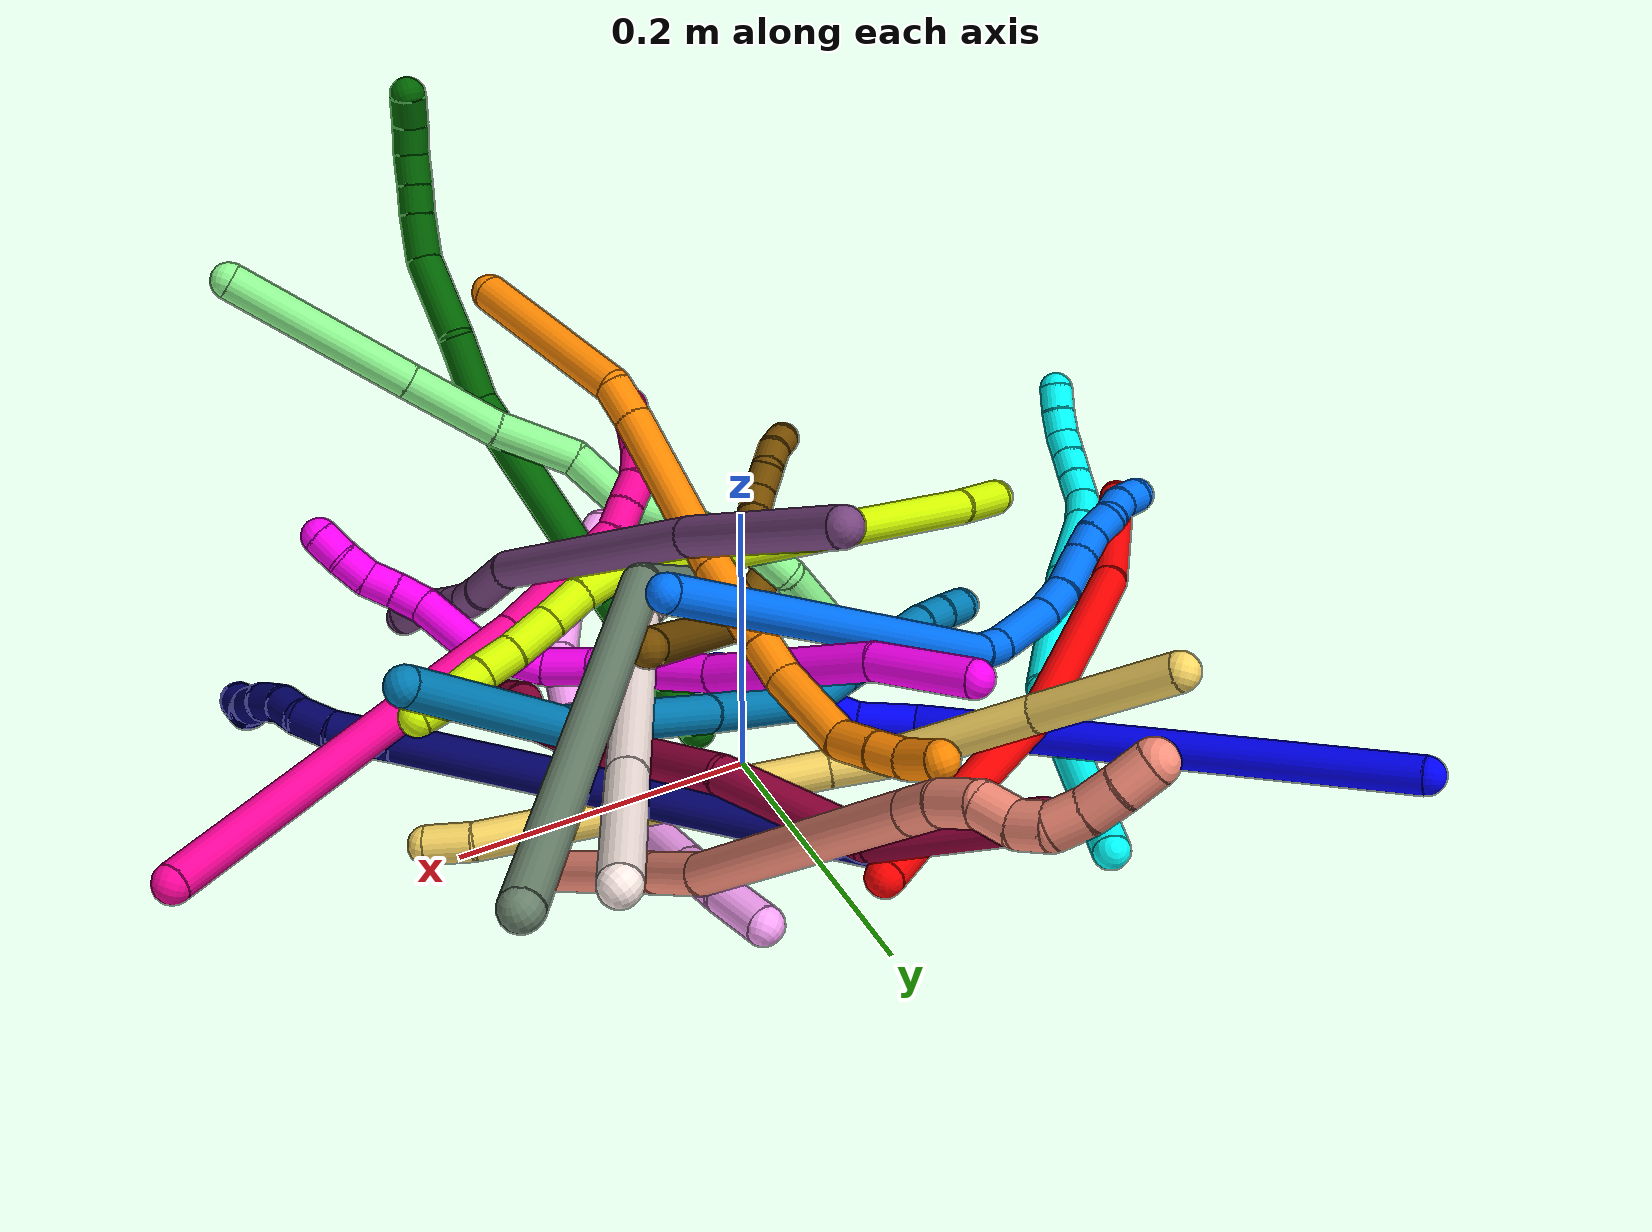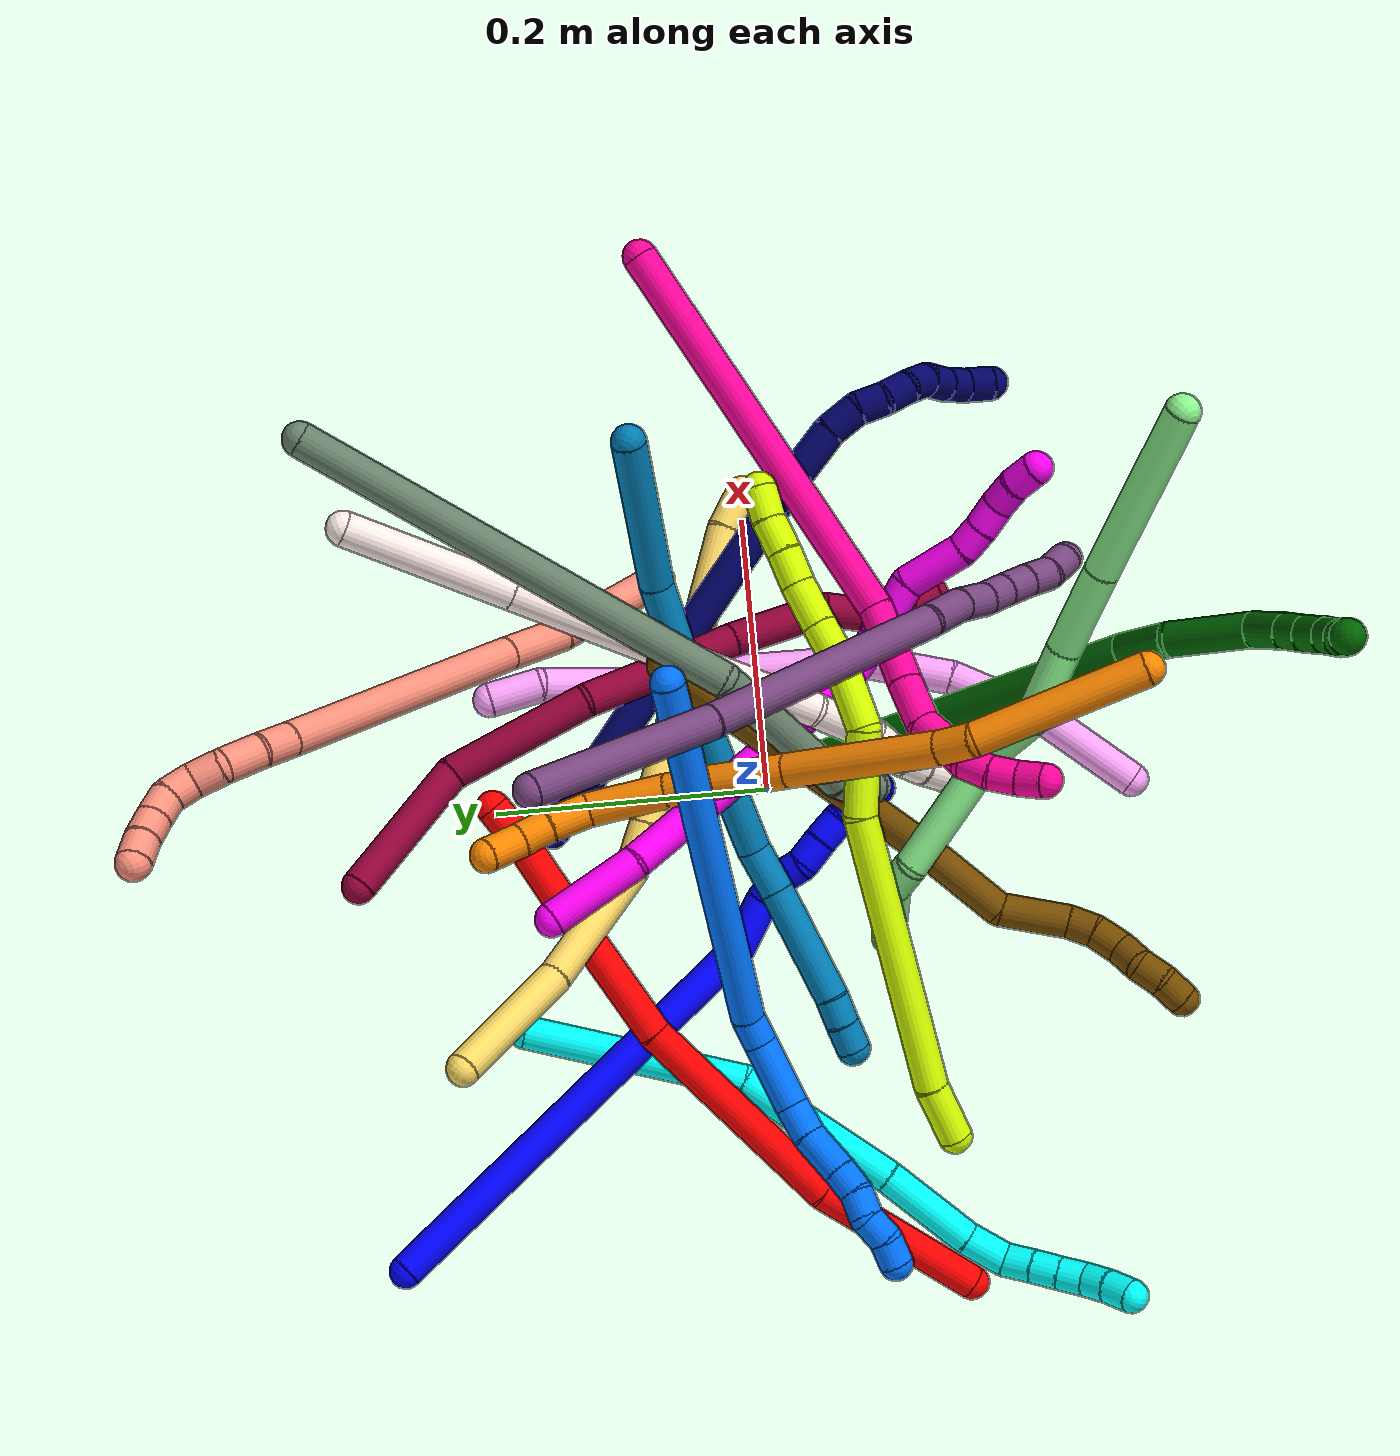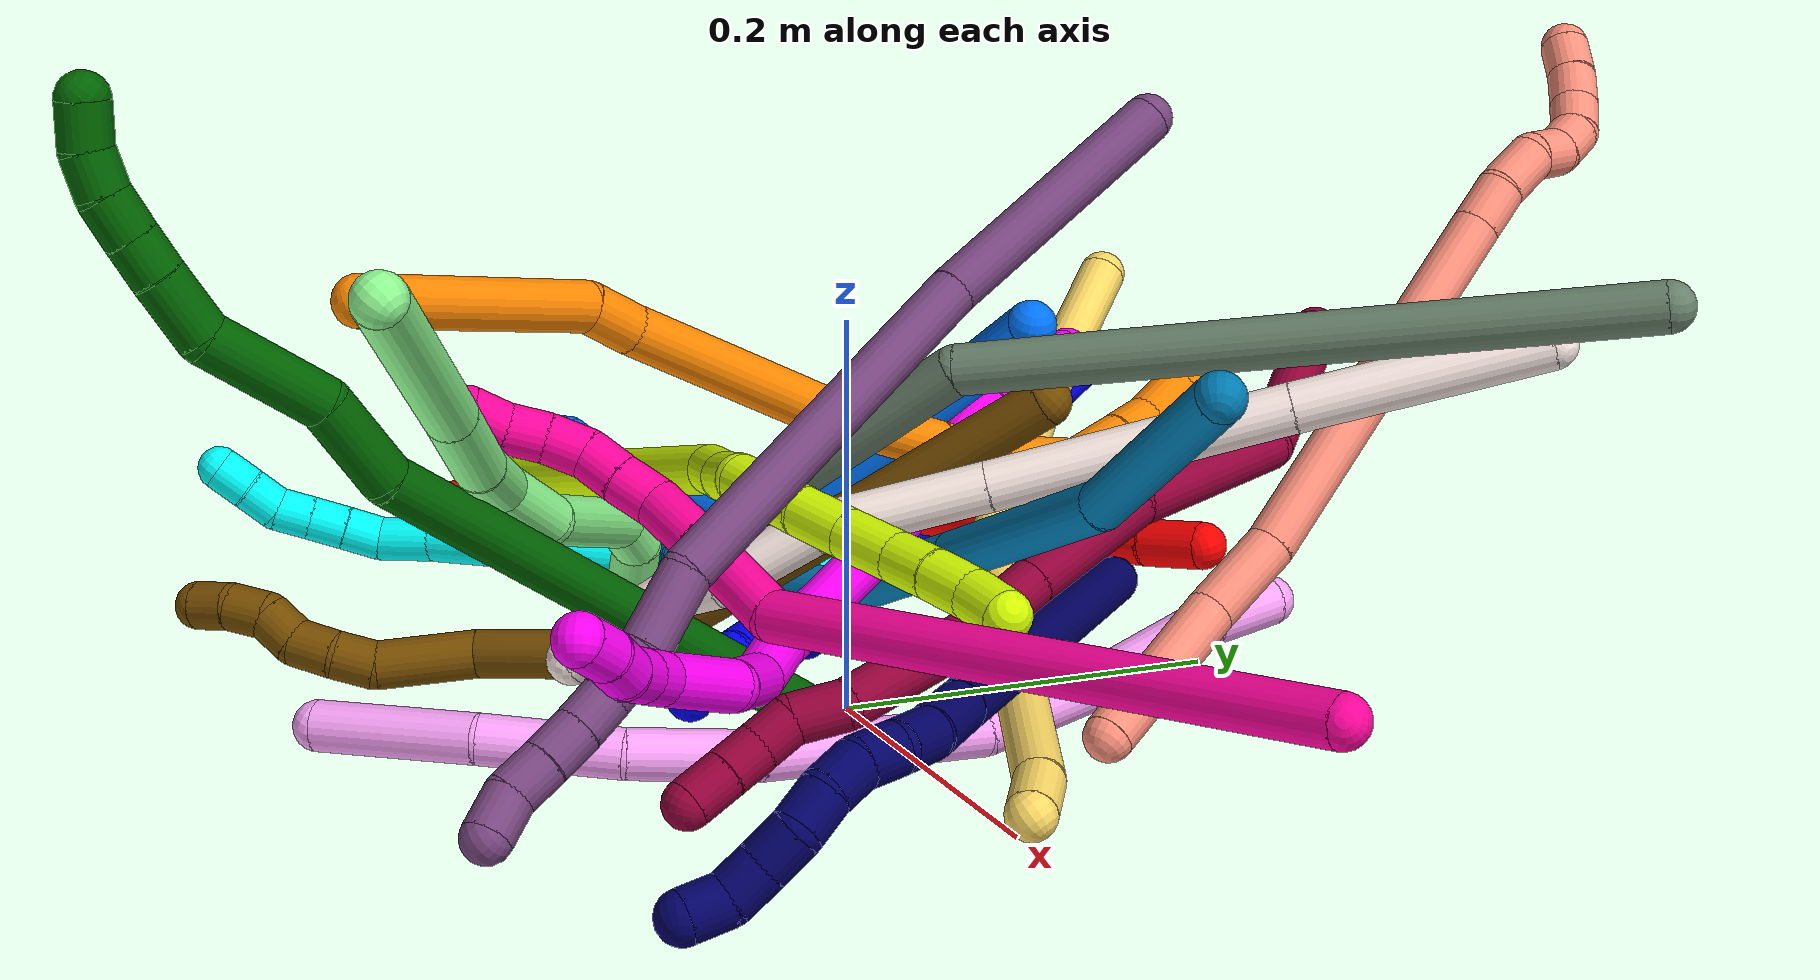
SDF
<sdf version="1.7">
 <world name="default">
  <plugin name="TubeGeneratorPlugin" filename="libtube_generator_plugin.so"/>
  <model name="photoneo_s_sensor">
   <static>1</static>
   <pose>0 0 2 1.57079 1.57079 3.14159</pose>
   <link name="link">
    <inertial><mass>0.1</mass></inertial>
    <sensor name="sensor" type="depth">
     <update_rate>30</update_rate>
     <camera>
      <horizontal_fov>1.22</horizontal_fov>
      <image><width>1920</width><height>1200</height><format>B8G8R8</format></image>
      <clip><near>0.1</near><far>4</far></clip>
      <depth_camera><output>points</output></depth_camera>
     </camera>
     <plugin name="camera_plugin" filename="libgazebo_ros_depth_camera.so">
      <baseline>0.2</baseline>
      <alwaysOn>1</alwaysOn>
      <updateRate>0.0</updateRate>
      <cameraName>camera_ir</cameraName>
      <imageTopicName>/camera/color/image_raw</imageTopicName>
      <cameraInfoTopicName>/camera/color/camera_info</cameraInfoTopicName>
      <depthImageTopicName>/camera/depth/image_raw</depthImageTopicName>
      <depthImageCameraInfoTopicName>/camera/depth/camera_info</depthImageCameraInfoTopicName>
      <pointCloudTopicName>/camera/depth/points</pointCloudTopicName>
      <frameName>fr_optical</frameName>
      <pointCloudCutoff>0.1</pointCloudCutoff>
      <pointCloudCutoffMax>2.0</pointCloudCutoffMax>
      <distortionK1>0</distortionK1>
      <distortionK2>0</distortionK2>
      <distortionK3>0</distortionK3>
      <distortionT1>0</distortionT1>
      <distortionT2>0</distortionT2>
      <CxPrime>0</CxPrime>
      <Cx>0</Cx>
      <Cy>0</Cy>
      <focalLength>0</focalLength>
      <hackBaseline>0</hackBaseline>
     </plugin>
    </sensor>
   </link>
  </model>
  <gravity>0 0 -9.8</gravity>
  <magnetic_field>6e-06 2.3e-05 -4.2e-05</magnetic_field>
  <atmosphere type="adiabatic"/>
  <physics name="default_physics" default="0" type="ode">
   <max_step_size>0.003</max_step_size>
   <real_time_factor>1</real_time_factor>
   <real_time_update_rate>1000</real_time_update_rate>
   <max_contacts>10000</max_contacts>
   <ode>
    <solver>
     <type>quick</type>
     <iters>100</iters>
     <sor>1.3</sor>
     <use_dynamic_moi_rescaling>0</use_dynamic_moi_rescaling>
    </solver>
    <constraints>
     <contact_max_correcting_vel>0</contact_max_correcting_vel>
     <contact_surface_layer>0.001</contact_surface_layer>
     <cfm>0</cfm>
     <erp>0.2</erp>
    </constraints>
   </ode>
  </physics>
  <scene><ambient>0.4 0.4 0.4 1</ambient><background>0.7 0.7 0.7 1</background><shadows>0</shadows></scene>
  <audio><device>default</device></audio>
  <spherical_coordinates>
   <surface_model>EARTH_WGS84</surface_model>
   <latitude_deg>0</latitude_deg>
   <longitude_deg>0</longitude_deg>
   <elevation>0</elevation>
   <heading_deg>0</heading_deg>
  </spherical_coordinates>
  <model name="bin">
   <static>1</static>
   <link name="bottom">
    <collision name="collision-bottom">
     <pose>0 0 -0.01 0 -0 0</pose>
     <geometry><box><size>0.8 0.6 0.02</size></box></geometry>
     <surface>
      <friction><ode><mu>100</mu><mu2>100</mu2></ode></friction>
      <contact><collide_bitmask>65535</collide_bitmask></contact>
     </surface>
    </collision>
   </link>
   <link name="west_wall">
    <collision name="collision-west_wall">
     <pose>-0.41 0 0.1 0 -0 0</pose>
     <geometry><box><size>0.02 0.6 0.2</size></box></geometry>
     <surface>
      <friction><ode><mu>100</mu><mu2>100</mu2></ode></friction>
      <contact><collide_bitmask>65535</collide_bitmask></contact>
     </surface>
    </collision>
   </link>
   <link name="east_wall">
    <collision name="collision-east_wall">
     <pose>0.41 0 0.1 0 -0 0</pose>
     <geometry><box><size>0.02 0.6 0.2</size></box></geometry>
     <surface>
      <friction><ode><mu>100</mu><mu2>100</mu2></ode></friction>
      <contact><collide_bitmask>65535</collide_bitmask></contact>
     </surface>
    </collision>
   </link>
   <link name="south_wall">
    <collision name="collision-south_wall">
     <pose>0 -0.31 0.1 0 -0 0</pose>
     <geometry><box><size>0.8 0.02 0.2</size></box></geometry>
     <surface>
      <friction><ode><mu>100</mu><mu2>100</mu2></ode></friction>
      <contact><collide_bitmask>65535</collide_bitmask></contact>
     </surface>
    </collision>
   </link>
   <link name="north_wall">
    <collision name="collision-north_wall">
     <pose>0 0.31 0.1 0 -0 0</pose>
     <geometry><box><size>0.8 0.02 0.2</size></box></geometry>
     <surface>
      <friction><ode><mu>100</mu><mu2>100</mu2></ode></friction>
      <contact><collide_bitmask>65535</collide_bitmask></contact>
     </surface>
    </collision>
   </link>
  </model>
  <model name="1">
   <static>0</static>
   <link name="1">
    <collision name="collision-cylinder-e_1_1_4">
     <pose>0.029832 -0.030413 -0.162078 2.9561 0.178968 1.53481</pose>
     <geometry><cylinder><radius>0.0125</radius><length>0.335167</length></cylinder></geometry>
     <surface>
      <friction><ode><mu>1.16</mu><mu2>1.16</mu2><slip1>0</slip1><slip2>0</slip2></ode></friction>
      <contact><ode><kp>1e+06</kp><kd>1</kd><max_vel>0</max_vel><min_depth>0.001</min_depth></ode></contact>
     </surface>
    </collision>
    <visual name="visual-cylinder-e_1_1_4">
     <pose>0.029832 -0.030413 -0.162078 2.9561 0.178968 1.53481</pose>
     <geometry><cylinder><radius>0.0125</radius><length>0.335167</length></cylinder></geometry>
     <material><ambient>0 0 1 1</ambient></material>
    </visual>
    <collision name="collision-cylinder-e_2_4_5">
     <pose>0.055717 -0.061799 -0.344134 3.09296 -0.194852 -2.6538</pose>
     <geometry><cylinder><radius>0.0125</radius><length>0.040775</length></cylinder></geometry>
     <surface>
      <friction><ode><mu>1.16</mu><mu2>1.16</mu2><slip1>0</slip1><slip2>0</slip2></ode></friction>
      <contact><ode><kp>1e+06</kp><kd>1</kd><max_vel>0</max_vel><min_depth>0.001</min_depth></ode></contact>
     </surface>
    </collision>
    <visual name="visual-cylinder-e_2_4_5">
     <pose>0.055717 -0.061799 -0.344134 3.09296 -0.194852 -2.6538</pose>
     <geometry><cylinder><radius>0.0125</radius><length>0.040775</length></cylinder></geometry>
     <material><ambient>0 0 1 1</ambient></material>
    </visual>
    <collision name="collision-cylinder-e_3_5_6">
     <pose>0.051412 -0.060309 -0.374522 -2.90933 -0.033408 0.284474</pose>
     <geometry><cylinder><radius>0.0125</radius><length>0.021406</length></cylinder></geometry>
     <surface>
      <friction><ode><mu>1.16</mu><mu2>1.16</mu2><slip1>0</slip1><slip2>0</slip2></ode></friction>
      <contact><ode><kp>1e+06</kp><kd>1</kd><max_vel>0</max_vel><min_depth>0.001</min_depth></ode></contact>
     </surface>
    </collision>
    <visual name="visual-cylinder-e_3_5_6">
     <pose>0.051412 -0.060309 -0.374522 -2.90933 -0.033408 0.284474</pose>
     <geometry><cylinder><radius>0.0125</radius><length>0.021406</length></cylinder></geometry>
     <material><ambient>0 0 1 1</ambient></material>
    </visual>
    <collision name="collision-cylinder-e_4_6_7">
     <pose>0.053349 -0.05372 -0.394014 -2.71507 0.226036 -0.965518</pose>
     <geometry><cylinder><radius>0.0125</radius><length>0.020472</length></cylinder></geometry>
     <surface>
      <friction><ode><mu>1.16</mu><mu2>1.16</mu2><slip1>0</slip1><slip2>0</slip2></ode></friction>
      <contact><ode><kp>1e+06</kp><kd>1</kd><max_vel>0</max_vel><min_depth>0.001</min_depth></ode></contact>
     </surface>
    </collision>
    <visual name="visual-cylinder-e_4_6_7">
     <pose>0.053349 -0.05372 -0.394014 -2.71507 0.226036 -0.965518</pose>
     <geometry><cylinder><radius>0.0125</radius><length>0.020472</length></cylinder></geometry>
     <material><ambient>0 0 1 1</ambient></material>
    </visual>
    <collision name="collision-cylinder-e_5_7_8">
     <pose>0.055448 -0.049232 -0.413849 -3.10802 -0.018126 0.990129</pose>
     <geometry><cylinder><radius>0.0125</radius><length>0.021522</length></cylinder></geometry>
     <surface>
      <friction><ode><mu>1.16</mu><mu2>1.16</mu2><slip1>0</slip1><slip2>0</slip2></ode></friction>
      <contact><ode><kp>1e+06</kp><kd>1</kd><max_vel>0</max_vel><min_depth>0.001</min_depth></ode></contact>
     </surface>
    </collision>
    <visual name="visual-cylinder-e_5_7_8">
     <pose>0.055448 -0.049232 -0.413849 -3.10802 -0.018126 0.990129</pose>
     <geometry><cylinder><radius>0.0125</radius><length>0.021522</length></cylinder></geometry>
     <material><ambient>0 0 1 1</ambient></material>
    </visual>
    <collision name="collision-cylinder-e_6_8_9">
     <pose>0.055749 -0.048898 -0.434904 3.13895 0.048167 3.03186</pose>
     <geometry><cylinder><radius>0.0125</radius><length>0.020628</length></cylinder></geometry>
     <surface>
      <friction><ode><mu>1.16</mu><mu2>1.16</mu2><slip1>0</slip1><slip2>0</slip2></ode></friction>
      <contact><ode><kp>1e+06</kp><kd>1</kd><max_vel>0</max_vel><min_depth>0.001</min_depth></ode></contact>
     </surface>
    </collision>
    <visual name="visual-cylinder-e_6_8_9">
     <pose>0.055749 -0.048898 -0.434904 3.13895 0.048167 3.03186</pose>
     <geometry><cylinder><radius>0.0125</radius><length>0.020628</length></cylinder></geometry>
     <material><ambient>0 0 1 1</ambient></material>
    </visual>
    <collision name="collision-cylinder-e_7_9_10">
     <pose>0.059128 -0.049632 -0.454768 3.0678 0.292002 2.64972</pose>
     <geometry><cylinder><radius>0.0125</radius><length>0.020025</length></cylinder></geometry>
     <surface>
      <friction><ode><mu>1.16</mu><mu2>1.16</mu2><slip1>0</slip1><slip2>0</slip2></ode></friction>
      <contact><ode><kp>1e+06</kp><kd>1</kd><max_vel>0</max_vel><min_depth>0.001</min_depth></ode></contact>
     </surface>
    </collision>
    <visual name="visual-cylinder-e_7_9_10">
     <pose>0.059128 -0.049632 -0.454768 3.0678 0.292002 2.64972</pose>
     <geometry><cylinder><radius>0.0125</radius><length>0.020025</length></cylinder></geometry>
     <material><ambient>0 0 1 1</ambient></material>
    </visual>
    <collision name="collision-cylinder-e_8_10_2">
     <pose>0.064704 -0.055042 -0.472738 2.63161 0.272629 0.968792</pose>
     <geometry><cylinder><radius>0.0125</radius><length>0.020006</length></cylinder></geometry>
     <surface>
      <friction><ode><mu>1.16</mu><mu2>1.16</mu2><slip1>0</slip1><slip2>0</slip2></ode></friction>
      <contact><ode><kp>1e+06</kp><kd>1</kd><max_vel>0</max_vel><min_depth>0.001</min_depth></ode></contact>
     </surface>
    </collision>
    <visual name="visual-cylinder-e_8_10_2">
     <pose>0.064704 -0.055042 -0.472738 2.63161 0.272629 0.968792</pose>
     <geometry><cylinder><radius>0.0125</radius><length>0.020006</length></cylinder></geometry>
     <material><ambient>0 0 1 1</ambient></material>
    </visual>
    <collision name="collision-sphere-2">
     <pose>0.067397 -0.059745 -0.481146 0 -0 0</pose>
     <geometry><sphere><radius>0.0125</radius></sphere></geometry>
     <surface>
      <friction><ode><mu>1.16</mu><mu2>1.16</mu2><slip1>0</slip1><slip2>0</slip2></ode></friction>
      <contact><ode><kp>1e+06</kp><kd>1</kd><max_vel>0</max_vel><min_depth>0.001</min_depth></ode></contact>
     </surface>
    </collision>
    <visual name="visual-sphere-2">
     <pose>0.067397 -0.059745 -0.481146 0 -0 0</pose>
     <geometry><sphere><radius>0.0125</radius></sphere></geometry>
     <material><ambient>0 0 1 1</ambient></material>
    </visual>
    <collision name="collision-sphere-10">
     <pose>0.06201 -0.050339 -0.46433 0 -0 0</pose>
     <geometry><sphere><radius>0.0125</radius></sphere></geometry>
     <surface>
      <friction><ode><mu>1.16</mu><mu2>1.16</mu2><slip1>0</slip1><slip2>0</slip2></ode></friction>
      <contact><ode><kp>1e+06</kp><kd>1</kd><max_vel>0</max_vel><min_depth>0.001</min_depth></ode></contact>
     </surface>
    </collision>
    <visual name="visual-sphere-10">
     <pose>0.06201 -0.050339 -0.46433 0 -0 0</pose>
     <geometry><sphere><radius>0.0125</radius></sphere></geometry>
     <material><ambient>0 0 1 1</ambient></material>
    </visual>
    <collision name="collision-sphere-9">
     <pose>0.056246 -0.048926 -0.445206 0 -0 0</pose>
     <geometry><sphere><radius>0.0125</radius></sphere></geometry>
     <surface>
      <friction><ode><mu>1.16</mu><mu2>1.16</mu2><slip1>0</slip1><slip2>0</slip2></ode></friction>
      <contact><ode><kp>1e+06</kp><kd>1</kd><max_vel>0</max_vel><min_depth>0.001</min_depth></ode></contact>
     </surface>
    </collision>
    <visual name="visual-sphere-9">
     <pose>0.056246 -0.048926 -0.445206 0 -0 0</pose>
     <geometry><sphere><radius>0.0125</radius></sphere></geometry>
     <material><ambient>0 0 1 1</ambient></material>
    </visual>
    <collision name="collision-sphere-4">
     <pose>0.059664 -0.060827 -0.324156 0 -0 0</pose>
     <geometry><sphere><radius>0.0125</radius></sphere></geometry>
     <surface>
      <friction><ode><mu>1.16</mu><mu2>1.16</mu2><slip1>0</slip1><slip2>0</slip2></ode></friction>
      <contact><ode><kp>1e+06</kp><kd>1</kd><max_vel>0</max_vel><min_depth>0.001</min_depth></ode></contact>
     </surface>
    </collision>
    <visual name="visual-sphere-4">
     <pose>0.059664 -0.060827 -0.324156 0 -0 0</pose>
     <geometry><sphere><radius>0.0125</radius></sphere></geometry>
     <material><ambient>0 0 1 1</ambient></material>
    </visual>
    <collision name="collision-sphere-1">
     <geometry><sphere><radius>0.0125</radius></sphere></geometry>
     <surface>
      <friction><ode><mu>1.16</mu><mu2>1.16</mu2><slip1>0</slip1><slip2>0</slip2></ode></friction>
      <contact><ode><kp>1e+06</kp><kd>1</kd><max_vel>0</max_vel><min_depth>0.001</min_depth></ode></contact>
     </surface>
    </collision>
    <visual name="visual-sphere-1">
     <geometry><sphere><radius>0.0125</radius></sphere></geometry>
     <material><ambient>0 0 1 1</ambient></material>
    </visual>
    <collision name="collision-sphere-8">
     <pose>0.055253 -0.048871 -0.424602 0 -0 0</pose>
     <geometry><sphere><radius>0.0125</radius></sphere></geometry>
     <surface>
      <friction><ode><mu>1.16</mu><mu2>1.16</mu2><slip1>0</slip1><slip2>0</slip2></ode></friction>
      <contact><ode><kp>1e+06</kp><kd>1</kd><max_vel>0</max_vel><min_depth>0.001</min_depth></ode></contact>
     </surface>
    </collision>
    <visual name="visual-sphere-8">
     <pose>0.055253 -0.048871 -0.424602 0 -0 0</pose>
     <geometry><sphere><radius>0.0125</radius></sphere></geometry>
     <material><ambient>0 0 1 1</ambient></material>
    </visual>
    <collision name="collision-sphere-5">
     <pose>0.05177 -0.062772 -0.364112 0 -0 0</pose>
     <geometry><sphere><radius>0.0125</radius></sphere></geometry>
     <surface>
      <friction><ode><mu>1.16</mu><mu2>1.16</mu2><slip1>0</slip1><slip2>0</slip2></ode></friction>
      <contact><ode><kp>1e+06</kp><kd>1</kd><max_vel>0</max_vel><min_depth>0.001</min_depth></ode></contact>
     </surface>
    </collision>
    <visual name="visual-sphere-5">
     <pose>0.05177 -0.062772 -0.364112 0 -0 0</pose>
     <geometry><sphere><radius>0.0125</radius></sphere></geometry>
     <material><ambient>0 0 1 1</ambient></material>
    </visual>
    <collision name="collision-sphere-6">
     <pose>0.051055 -0.057847 -0.384932 0 -0 0</pose>
     <geometry><sphere><radius>0.0125</radius></sphere></geometry>
     <surface>
      <friction><ode><mu>1.16</mu><mu2>1.16</mu2><slip1>0</slip1><slip2>0</slip2></ode></friction>
      <contact><ode><kp>1e+06</kp><kd>1</kd><max_vel>0</max_vel><min_depth>0.001</min_depth></ode></contact>
     </surface>
    </collision>
    <visual name="visual-sphere-6">
     <pose>0.051055 -0.057847 -0.384932 0 -0 0</pose>
     <geometry><sphere><radius>0.0125</radius></sphere></geometry>
     <material><ambient>0 0 1 1</ambient></material>
    </visual>
    <collision name="collision-sphere-7">
     <pose>0.055643 -0.049593 -0.403096 0 -0 0</pose>
     <geometry><sphere><radius>0.0125</radius></sphere></geometry>
     <surface>
      <friction><ode><mu>1.16</mu><mu2>1.16</mu2><slip1>0</slip1><slip2>0</slip2></ode></friction>
      <contact><ode><kp>1e+06</kp><kd>1</kd><max_vel>0</max_vel><min_depth>0.001</min_depth></ode></contact>
     </surface>
    </collision>
    <visual name="visual-sphere-7">
     <pose>0.055643 -0.049593 -0.403096 0 -0 0</pose>
     <geometry><sphere><radius>0.0125</radius></sphere></geometry>
     <material><ambient>0 0 1 1</ambient></material>
    </visual>
    <inertial>
     <pose>0.03857 -0.038535 -0.241761 0 -0 0</pose>
     <mass>0.5</mass>
     <inertia>
      <ixx>0.00321</ixx>
      <ixy>0</ixy>
      <ixz>0</ixz>
      <iyy>0.003091</iyy>
      <iyz>0</iyz>
      <izz>-2.6e-05</izz>
     </inertia>
    </inertial>
   </link>
   <pose>-0.318637 0.288308 0.084571 1.57556 0.198561 -2.32644</pose>
  </model>
  <model name="2">
   <static>0</static>
   <link name="2">
    <collision name="collision-cylinder-e_1_1_4">
     <pose>0.011812 0.044598 -0.045651 -2.36786 0.183011 -0.443083</pose>
     <geometry><cylinder><radius>0.0125</radius><length>0.129807</length></cylinder></geometry>
     <surface>
      <friction><ode><mu>1.16</mu><mu2>1.16</mu2><slip1>0</slip1><slip2>0</slip2></ode></friction>
      <contact><ode><kp>1e+06</kp><kd>1</kd><max_vel>0</max_vel><min_depth>0.001</min_depth></ode></contact>
     </surface>
    </collision>
    <visual name="visual-cylinder-e_1_1_4">
     <pose>0.011812 0.044598 -0.045651 -2.36786 0.183011 -0.443083</pose>
     <geometry><cylinder><radius>0.0125</radius><length>0.129807</length></cylinder></geometry>
     <material><ambient>1 0 0 1</ambient></material>
    </visual>
    <collision name="collision-cylinder-e_2_4_5">
     <pose>0.043772 0.157608 -0.136329 -2.1529 0.241213 -0.442358</pose>
     <geometry><cylinder><radius>0.0125</radius><length>0.168686</length></cylinder></geometry>
     <surface>
      <friction><ode><mu>1.16</mu><mu2>1.16</mu2><slip1>0</slip1><slip2>0</slip2></ode></friction>
      <contact><ode><kp>1e+06</kp><kd>1</kd><max_vel>0</max_vel><min_depth>0.001</min_depth></ode></contact>
     </surface>
    </collision>
    <visual name="visual-cylinder-e_2_4_5">
     <pose>0.043772 0.157608 -0.136329 -2.1529 0.241213 -0.442358</pose>
     <geometry><cylinder><radius>0.0125</radius><length>0.168686</length></cylinder></geometry>
     <material><ambient>1 0 0 1</ambient></material>
    </visual>
    <collision name="collision-cylinder-e_3_5_6">
     <pose>0.07869 0.280869 -0.20326 -1.95074 0.245073 -0.359656</pose>
     <geometry><cylinder><radius>0.0125</radius><length>0.121758</length></cylinder></geometry>
     <surface>
      <friction><ode><mu>1.16</mu><mu2>1.16</mu2><slip1>0</slip1><slip2>0</slip2></ode></friction>
      <contact><ode><kp>1e+06</kp><kd>1</kd><max_vel>0</max_vel><min_depth>0.001</min_depth></ode></contact>
     </surface>
    </collision>
    <visual name="visual-cylinder-e_3_5_6">
     <pose>0.07869 0.280869 -0.20326 -1.95074 0.245073 -0.359656</pose>
     <geometry><cylinder><radius>0.0125</radius><length>0.121758</length></cylinder></geometry>
     <material><ambient>1 0 0 1</ambient></material>
    </visual>
    <collision name="collision-cylinder-e_4_6_7">
     <pose>0.099025 0.356998 -0.233033 -1.92499 0.240469 -0.34356</pose>
     <geometry><cylinder><radius>0.0125</radius><length>0.046722</length></cylinder></geometry>
     <surface>
      <friction><ode><mu>1.16</mu><mu2>1.16</mu2><slip1>0</slip1><slip2>0</slip2></ode></friction>
      <contact><ode><kp>1e+06</kp><kd>1</kd><max_vel>0</max_vel><min_depth>0.001</min_depth></ode></contact>
     </surface>
    </collision>
    <visual name="visual-cylinder-e_4_6_7">
     <pose>0.099025 0.356998 -0.233033 -1.92499 0.240469 -0.34356</pose>
     <geometry><cylinder><radius>0.0125</radius><length>0.046722</length></cylinder></geometry>
     <material><ambient>1 0 0 1</ambient></material>
    </visual>
    <collision name="collision-cylinder-e_5_7_2">
     <pose>0.107863 0.392859 -0.247928 -2.01979 0.199645 -0.316199</pose>
     <geometry><cylinder><radius>0.0125</radius><length>0.033027</length></cylinder></geometry>
     <surface>
      <friction><ode><mu>1.16</mu><mu2>1.16</mu2><slip1>0</slip1><slip2>0</slip2></ode></friction>
      <contact><ode><kp>1e+06</kp><kd>1</kd><max_vel>0</max_vel><min_depth>0.001</min_depth></ode></contact>
     </surface>
    </collision>
    <visual name="visual-cylinder-e_5_7_2">
     <pose>0.107863 0.392859 -0.247928 -2.01979 0.199645 -0.316199</pose>
     <geometry><cylinder><radius>0.0125</radius><length>0.033027</length></cylinder></geometry>
     <material><ambient>1 0 0 1</ambient></material>
    </visual>
    <collision name="collision-sphere-2">
     <pose>0.111138 0.407441 -0.254953 0 -0 0</pose>
     <geometry><sphere><radius>0.0125</radius></sphere></geometry>
     <surface>
      <friction><ode><mu>1.16</mu><mu2>1.16</mu2><slip1>0</slip1><slip2>0</slip2></ode></friction>
      <contact><ode><kp>1e+06</kp><kd>1</kd><max_vel>0</max_vel><min_depth>0.001</min_depth></ode></contact>
     </surface>
    </collision>
    <visual name="visual-sphere-2">
     <pose>0.111138 0.407441 -0.254953 0 -0 0</pose>
     <geometry><sphere><radius>0.0125</radius></sphere></geometry>
     <material><ambient>1 0 0 1</ambient></material>
    </visual>
    <collision name="collision-sphere-7">
     <pose>0.104588 0.378278 -0.240902 0 -0 0</pose>
     <geometry><sphere><radius>0.0125</radius></sphere></geometry>
     <surface>
      <friction><ode><mu>1.16</mu><mu2>1.16</mu2><slip1>0</slip1><slip2>0</slip2></ode></friction>
      <contact><ode><kp>1e+06</kp><kd>1</kd><max_vel>0</max_vel><min_depth>0.001</min_depth></ode></contact>
     </surface>
    </collision>
    <visual name="visual-sphere-7">
     <pose>0.104588 0.378278 -0.240902 0 -0 0</pose>
     <geometry><sphere><radius>0.0125</radius></sphere></geometry>
     <material><ambient>1 0 0 1</ambient></material>
    </visual>
    <collision name="collision-sphere-6">
     <pose>0.093461 0.335717 -0.225164 0 -0 0</pose>
     <geometry><sphere><radius>0.0125</radius></sphere></geometry>
     <surface>
      <friction><ode><mu>1.16</mu><mu2>1.16</mu2><slip1>0</slip1><slip2>0</slip2></ode></friction>
      <contact><ode><kp>1e+06</kp><kd>1</kd><max_vel>0</max_vel><min_depth>0.001</min_depth></ode></contact>
     </surface>
    </collision>
    <visual name="visual-sphere-6">
     <pose>0.093461 0.335717 -0.225164 0 -0 0</pose>
     <geometry><sphere><radius>0.0125</radius></sphere></geometry>
     <material><ambient>1 0 0 1</ambient></material>
    </visual>
    <collision name="collision-sphere-5">
     <pose>0.06392 0.226021 -0.181357 0 -0 0</pose>
     <geometry><sphere><radius>0.0125</radius></sphere></geometry>
     <surface>
      <friction><ode><mu>1.16</mu><mu2>1.16</mu2><slip1>0</slip1><slip2>0</slip2></ode></friction>
      <contact><ode><kp>1e+06</kp><kd>1</kd><max_vel>0</max_vel><min_depth>0.001</min_depth></ode></contact>
     </surface>
    </collision>
    <visual name="visual-sphere-5">
     <pose>0.06392 0.226021 -0.181357 0 -0 0</pose>
     <geometry><sphere><radius>0.0125</radius></sphere></geometry>
     <material><ambient>1 0 0 1</ambient></material>
    </visual>
    <collision name="collision-sphere-1">
     <geometry><sphere><radius>0.0125</radius></sphere></geometry>
     <surface>
      <friction><ode><mu>1.16</mu><mu2>1.16</mu2><slip1>0</slip1><slip2>0</slip2></ode></friction>
      <contact><ode><kp>1e+06</kp><kd>1</kd><max_vel>0</max_vel><min_depth>0.001</min_depth></ode></contact>
     </surface>
    </collision>
    <visual name="visual-sphere-1">
     <geometry><sphere><radius>0.0125</radius></sphere></geometry>
     <material><ambient>1 0 0 1</ambient></material>
    </visual>
    <collision name="collision-sphere-4">
     <pose>0.023624 0.089196 -0.091301 0 -0 0</pose>
     <geometry><sphere><radius>0.0125</radius></sphere></geometry>
     <surface>
      <friction><ode><mu>1.16</mu><mu2>1.16</mu2><slip1>0</slip1><slip2>0</slip2></ode></friction>
      <contact><ode><kp>1e+06</kp><kd>1</kd><max_vel>0</max_vel><min_depth>0.001</min_depth></ode></contact>
     </surface>
    </collision>
    <visual name="visual-sphere-4">
     <pose>0.023624 0.089196 -0.091301 0 -0 0</pose>
     <geometry><sphere><radius>0.0125</radius></sphere></geometry>
     <material><ambient>1 0 0 1</ambient></material>
    </visual>
    <inertial>
     <pose>0.053374 0.192456 -0.145494 0 -0 0</pose>
     <mass>0.5</mass>
     <inertia>
      <ixx>0.000381</ixx>
      <ixy>0</ixy>
      <ixz>0</ixz>
      <iyy>-0.000598</iyy>
      <iyz>0</iyz>
      <izz>-0.000804</izz>
     </inertia>
    </inertial>
   </link>
   <pose>-0.371905 -0.117004 0.027183 2.18644 1.26649 0.750584</pose>
  </model>
  <model name="3">
   <static>0</static>
   <link name="3">
    <collision name="collision-cylinder-e_1_1_4">
     <pose>-0.011115 -0.061746 0.05356 0.856269 -0.135151 -0.061753</pose>
     <geometry><cylinder><radius>0.0125</radius><length>0.164983</length></cylinder></geometry>
     <surface>
      <friction><ode><mu>1.16</mu><mu2>1.16</mu2><slip1>0</slip1><slip2>0</slip2></ode></friction>
      <contact><ode><kp>1e+06</kp><kd>1</kd><max_vel>0</max_vel><min_depth>0.001</min_depth></ode></contact>
     </surface>
    </collision>
    <visual name="visual-cylinder-e_1_1_4">
     <pose>-0.011115 -0.061746 0.05356 0.856269 -0.135151 -0.061753</pose>
     <geometry><cylinder><radius>0.0125</radius><length>0.164983</length></cylinder></geometry>
     <material><ambient>0.003922 1 0.996078 1</ambient></material>
    </visual>
    <collision name="collision-cylinder-e_2_4_5">
     <pose>-0.008522 -0.174282 0.142656 0.960313 0.217631 0.113671</pose>
     <geometry><cylinder><radius>0.0125</radius><length>0.126969</length></cylinder></geometry>
     <surface>
      <friction><ode><mu>1.16</mu><mu2>1.16</mu2><slip1>0</slip1><slip2>0</slip2></ode></friction>
      <contact><ode><kp>1e+06</kp><kd>1</kd><max_vel>0</max_vel><min_depth>0.001</min_depth></ode></contact>
     </surface>
    </collision>
    <visual name="visual-cylinder-e_2_4_5">
     <pose>-0.008522 -0.174282 0.142656 0.960313 0.217631 0.113671</pose>
     <geometry><cylinder><radius>0.0125</radius><length>0.126969</length></cylinder></geometry>
     <material><ambient>0.003922 1 0.996078 1</ambient></material>
    </visual>
    <collision name="collision-cylinder-e_3_5_6">
     <pose>0.015998 -0.253556 0.198628 0.948416 0.299187 0.154412</pose>
     <geometry><cylinder><radius>0.0125</radius><length>0.073374</length></cylinder></geometry>
     <surface>
      <friction><ode><mu>1.16</mu><mu2>1.16</mu2><slip1>0</slip1><slip2>0</slip2></ode></friction>
      <contact><ode><kp>1e+06</kp><kd>1</kd><max_vel>0</max_vel><min_depth>0.001</min_depth></ode></contact>
     </surface>
    </collision>
    <visual name="visual-cylinder-e_3_5_6">
     <pose>0.015998 -0.253556 0.198628 0.948416 0.299187 0.154412</pose>
     <geometry><cylinder><radius>0.0125</radius><length>0.073374</length></cylinder></geometry>
     <material><ambient>0.003922 1 0.996078 1</ambient></material>
    </visual>
    <collision name="collision-cylinder-e_4_6_7">
     <pose>0.0294 -0.294335 0.228983 0.892002 0.162393 0.077777</pose>
     <geometry><cylinder><radius>0.0125</radius><length>0.032015</length></cylinder></geometry>
     <surface>
      <friction><ode><mu>1.16</mu><mu2>1.16</mu2><slip1>0</slip1><slip2>0</slip2></ode></friction>
      <contact><ode><kp>1e+06</kp><kd>1</kd><max_vel>0</max_vel><min_depth>0.001</min_depth></ode></contact>
     </surface>
    </collision>
    <visual name="visual-cylinder-e_4_6_7">
     <pose>0.0294 -0.294335 0.228983 0.892002 0.162393 0.077777</pose>
     <geometry><cylinder><radius>0.0125</radius><length>0.032015</length></cylinder></geometry>
     <material><ambient>0.003922 1 0.996078 1</ambient></material>
    </visual>
    <collision name="collision-cylinder-e_5_7_8">
     <pose>0.029381 -0.316552 0.242914 1.18649 -0.238963 -0.161543</pose>
     <geometry><cylinder><radius>0.0125</radius><length>0.02203</length></cylinder></geometry>
     <surface>
      <friction><ode><mu>1.16</mu><mu2>1.16</mu2><slip1>0</slip1><slip2>0</slip2></ode></friction>
      <contact><ode><kp>1e+06</kp><kd>1</kd><max_vel>0</max_vel><min_depth>0.001</min_depth></ode></contact>
     </surface>
    </collision>
    <visual name="visual-cylinder-e_5_7_8">
     <pose>0.029381 -0.316552 0.242914 1.18649 -0.238963 -0.161543</pose>
     <geometry><cylinder><radius>0.0125</radius><length>0.02203</length></cylinder></geometry>
     <material><ambient>0.003922 1 0.996078 1</ambient></material>
    </visual>
    <collision name="collision-cylinder-e_6_8_9">
     <pose>0.02472 -0.33573 0.250851 1.16976 -0.20149 -0.133674</pose>
     <geometry><cylinder><radius>0.0125</radius><length>0.020524</length></cylinder></geometry>
     <surface>
      <friction><ode><mu>1.16</mu><mu2>1.16</mu2><slip1>0</slip1><slip2>0</slip2></ode></friction>
      <contact><ode><kp>1e+06</kp><kd>1</kd><max_vel>0</max_vel><min_depth>0.001</min_depth></ode></contact>
     </surface>
    </collision>
    <visual name="visual-cylinder-e_6_8_9">
     <pose>0.02472 -0.33573 0.250851 1.16976 -0.20149 -0.133674</pose>
     <geometry><cylinder><radius>0.0125</radius><length>0.020524</length></cylinder></geometry>
     <material><ambient>0.003922 1 0.996078 1</ambient></material>
    </visual>
    <collision name="collision-cylinder-e_7_9_10">
     <pose>0.02049 -0.35399 0.258667 1.1629 -0.218314 -0.143809</pose>
     <geometry><cylinder><radius>0.0125</radius><length>0.020092</length></cylinder></geometry>
     <surface>
      <friction><ode><mu>1.16</mu><mu2>1.16</mu2><slip1>0</slip1><slip2>0</slip2></ode></friction>
      <contact><ode><kp>1e+06</kp><kd>1</kd><max_vel>0</max_vel><min_depth>0.001</min_depth></ode></contact>
     </surface>
    </collision>
    <visual name="visual-cylinder-e_7_9_10">
     <pose>0.02049 -0.35399 0.258667 1.1629 -0.218314 -0.143809</pose>
     <geometry><cylinder><radius>0.0125</radius><length>0.020092</length></cylinder></geometry>
     <material><ambient>0.003922 1 0.996078 1</ambient></material>
    </visual>
    <collision name="collision-cylinder-e_8_10_11">
     <pose>0.015693 -0.372638 0.26289 1.53628 -0.265244 -0.256342</pose>
     <geometry><cylinder><radius>0.0125</radius><length>0.020002</length></cylinder></geometry>
     <surface>
      <friction><ode><mu>1.16</mu><mu2>1.16</mu2><slip1>0</slip1><slip2>0</slip2></ode></friction>
      <contact><ode><kp>1e+06</kp><kd>1</kd><max_vel>0</max_vel><min_depth>0.001</min_depth></ode></contact>
     </surface>
    </collision>
    <visual name="visual-cylinder-e_8_10_11">
     <pose>0.015693 -0.372638 0.26289 1.53628 -0.265244 -0.256342</pose>
     <geometry><cylinder><radius>0.0125</radius><length>0.020002</length></cylinder></geometry>
     <material><ambient>0.003922 1 0.996078 1</ambient></material>
    </visual>
    <collision name="collision-cylinder-e_9_11_2">
     <pose>0.011426 -0.392137 0.263778 1.51458 -0.165179 -0.156183</pose>
     <geometry><cylinder><radius>0.0125</radius><length>0.020012</length></cylinder></geometry>
     <surface>
      <friction><ode><mu>1.16</mu><mu2>1.16</mu2><slip1>0</slip1><slip2>0</slip2></ode></friction>
      <contact><ode><kp>1e+06</kp><kd>1</kd><max_vel>0</max_vel><min_depth>0.001</min_depth></ode></contact>
     </surface>
    </collision>
    <visual name="visual-cylinder-e_9_11_2">
     <pose>0.011426 -0.392137 0.263778 1.51458 -0.165179 -0.156183</pose>
     <geometry><cylinder><radius>0.0125</radius><length>0.020012</length></cylinder></geometry>
     <material><ambient>0.003922 1 0.996078 1</ambient></material>
    </visual>
    <collision name="collision-sphere-2">
     <pose>0.00978 -0.401991 0.264333 0 -0 0</pose>
     <geometry><sphere><radius>0.0125</radius></sphere></geometry>
     <surface>
      <friction><ode><mu>1.16</mu><mu2>1.16</mu2><slip1>0</slip1><slip2>0</slip2></ode></friction>
      <contact><ode><kp>1e+06</kp><kd>1</kd><max_vel>0</max_vel><min_depth>0.001</min_depth></ode></contact>
     </surface>
    </collision>
    <visual name="visual-sphere-2">
     <pose>0.00978 -0.401991 0.264333 0 -0 0</pose>
     <geometry><sphere><radius>0.0125</radius></sphere></geometry>
     <material><ambient>0.003922 1 0.996078 1</ambient></material>
    </visual>
    <collision name="collision-sphere-11">
     <pose>0.013071 -0.382283 0.263224 0 -0 0</pose>
     <geometry><sphere><radius>0.0125</radius></sphere></geometry>
     <surface>
      <friction><ode><mu>1.16</mu><mu2>1.16</mu2><slip1>0</slip1><slip2>0</slip2></ode></friction>
      <contact><ode><kp>1e+06</kp><kd>1</kd><max_vel>0</max_vel><min_depth>0.001</min_depth></ode></contact>
     </surface>
    </collision>
    <visual name="visual-sphere-11">
     <pose>0.013071 -0.382283 0.263224 0 -0 0</pose>
     <geometry><sphere><radius>0.0125</radius></sphere></geometry>
     <material><ambient>0.003922 1 0.996078 1</ambient></material>
    </visual>
    <collision name="collision-sphere-10">
     <pose>0.018314 -0.362992 0.262557 0 -0 0</pose>
     <geometry><sphere><radius>0.0125</radius></sphere></geometry>
     <surface>
      <friction><ode><mu>1.16</mu><mu2>1.16</mu2><slip1>0</slip1><slip2>0</slip2></ode></friction>
      <contact><ode><kp>1e+06</kp><kd>1</kd><max_vel>0</max_vel><min_depth>0.001</min_depth></ode></contact>
     </surface>
    </collision>
    <visual name="visual-sphere-10">
     <pose>0.018314 -0.362992 0.262557 0 -0 0</pose>
     <geometry><sphere><radius>0.0125</radius></sphere></geometry>
     <material><ambient>0.003922 1 0.996078 1</ambient></material>
    </visual>
    <collision name="collision-sphere-9">
     <pose>0.022666 -0.344987 0.254776 0 -0 0</pose>
     <geometry><sphere><radius>0.0125</radius></sphere></geometry>
     <surface>
      <friction><ode><mu>1.16</mu><mu2>1.16</mu2><slip1>0</slip1><slip2>0</slip2></ode></friction>
      <contact><ode><kp>1e+06</kp><kd>1</kd><max_vel>0</max_vel><min_depth>0.001</min_depth></ode></contact>
     </surface>
    </collision>
    <visual name="visual-sphere-9">
     <pose>0.022666 -0.344987 0.254776 0 -0 0</pose>
     <geometry><sphere><radius>0.0125</radius></sphere></geometry>
     <material><ambient>0.003922 1 0.996078 1</ambient></material>
    </visual>
    <collision name="collision-sphere-4">
     <pose>-0.02223 -0.123492 0.107121 0 -0 0</pose>
     <geometry><sphere><radius>0.0125</radius></sphere></geometry>
     <surface>
      <friction><ode><mu>1.16</mu><mu2>1.16</mu2><slip1>0</slip1><slip2>0</slip2></ode></friction>
      <contact><ode><kp>1e+06</kp><kd>1</kd><max_vel>0</max_vel><min_depth>0.001</min_depth></ode></contact>
     </surface>
    </collision>
    <visual name="visual-sphere-4">
     <pose>-0.02223 -0.123492 0.107121 0 -0 0</pose>
     <geometry><sphere><radius>0.0125</radius></sphere></geometry>
     <material><ambient>0.003922 1 0.996078 1</ambient></material>
    </visual>
    <collision name="collision-sphere-1">
     <geometry><sphere><radius>0.0125</radius></sphere></geometry>
     <surface>
      <friction><ode><mu>1.16</mu><mu2>1.16</mu2><slip1>0</slip1><slip2>0</slip2></ode></friction>
      <contact><ode><kp>1e+06</kp><kd>1</kd><max_vel>0</max_vel><min_depth>0.001</min_depth></ode></contact>
     </surface>
    </collision>
    <visual name="visual-sphere-1">
     <geometry><sphere><radius>0.0125</radius></sphere></geometry>
     <material><ambient>0.003922 1 0.996078 1</ambient></material>
    </visual>
    <collision name="collision-sphere-8">
     <pose>0.026773 -0.326473 0.246926 0 -0 0</pose>
     <geometry><sphere><radius>0.0125</radius></sphere></geometry>
     <surface>
      <friction><ode><mu>1.16</mu><mu2>1.16</mu2><slip1>0</slip1><slip2>0</slip2></ode></friction>
      <contact><ode><kp>1e+06</kp><kd>1</kd><max_vel>0</max_vel><min_depth>0.001</min_depth></ode></contact>
     </surface>
    </collision>
    <visual name="visual-sphere-8">
     <pose>0.026773 -0.326473 0.246926 0 -0 0</pose>
     <geometry><sphere><radius>0.0125</radius></sphere></geometry>
     <material><ambient>0.003922 1 0.996078 1</ambient></material>
    </visual>
    <collision name="collision-sphere-5">
     <pose>0.005185 -0.225073 0.178191 0 -0 0</pose>
     <geometry><sphere><radius>0.0125</radius></sphere></geometry>
     <surface>
      <friction><ode><mu>1.16</mu><mu2>1.16</mu2><slip1>0</slip1><slip2>0</slip2></ode></friction>
      <contact><ode><kp>1e+06</kp><kd>1</kd><max_vel>0</max_vel><min_depth>0.001</min_depth></ode></contact>
     </surface>
    </collision>
    <visual name="visual-sphere-5">
     <pose>0.005185 -0.225073 0.178191 0 -0 0</pose>
     <geometry><sphere><radius>0.0125</radius></sphere></geometry>
     <material><ambient>0.003922 1 0.996078 1</ambient></material>
    </visual>
    <collision name="collision-sphere-6">
     <pose>0.026812 -0.28204 0.219065 0 -0 0</pose>
     <geometry><sphere><radius>0.0125</radius></sphere></geometry>
     <surface>
      <friction><ode><mu>1.16</mu><mu2>1.16</mu2><slip1>0</slip1><slip2>0</slip2></ode></friction>
      <contact><ode><kp>1e+06</kp><kd>1</kd><max_vel>0</max_vel><min_depth>0.001</min_depth></ode></contact>
     </surface>
    </collision>
    <visual name="visual-sphere-6">
     <pose>0.026812 -0.28204 0.219065 0 -0 0</pose>
     <geometry><sphere><radius>0.0125</radius></sphere></geometry>
     <material><ambient>0.003922 1 0.996078 1</ambient></material>
    </visual>
    <collision name="collision-sphere-7">
     <pose>0.031988 -0.306631 0.238902 0 -0 0</pose>
     <geometry><sphere><radius>0.0125</radius></sphere></geometry>
     <surface>
      <friction><ode><mu>1.16</mu><mu2>1.16</mu2><slip1>0</slip1><slip2>0</slip2></ode></friction>
      <contact><ode><kp>1e+06</kp><kd>1</kd><max_vel>0</max_vel><min_depth>0.001</min_depth></ode></contact>
     </surface>
    </collision>
    <visual name="visual-sphere-7">
     <pose>0.031988 -0.306631 0.238902 0 -0 0</pose>
     <geometry><sphere><radius>0.0125</radius></sphere></geometry>
     <material><ambient>0.003922 1 0.996078 1</ambient></material>
    </visual>
    <inertial>
     <pose>0.002616 -0.193241 0.150177 0 -0 0</pose>
     <mass>0.5</mass>
     <inertia>
      <ixx>0.000593</ixx>
      <ixy>0</ixy>
      <ixz>0</ixz>
      <iyy>0.000351</iyy>
      <iyz>0</iyz>
      <izz>0.000488</izz>
     </inertia>
    </inertial>
   </link>
   <pose>-0.161001 0.192986 0.012531 -2.46075 0.237553 2.69179</pose>
  </model>
  <model name="4">
   <static>0</static>
   <link name="4">
    <collision name="collision-cylinder-e_1_1_4">
     <pose>0.015264 0.006679 -0.037898 -2.96716 0.377626 -2.28332</pose>
     <geometry><cylinder><radius>0.0125</radius><length>0.082798</length></cylinder></geometry>
     <surface>
      <friction><ode><mu>1.16</mu><mu2>1.16</mu2><slip1>0</slip1><slip2>0</slip2></ode></friction>
      <contact><ode><kp>1e+06</kp><kd>1</kd><max_vel>0</max_vel><min_depth>0.001</min_depth></ode></contact>
     </surface>
    </collision>
    <visual name="visual-cylinder-e_1_1_4">
     <pose>0.015264 0.006679 -0.037898 -2.96716 0.377626 -2.28332</pose>
     <geometry><cylinder><radius>0.0125</radius><length>0.082798</length></cylinder></geometry>
     <material><ambient>1 0.65098 0.996078 1</ambient></material>
    </visual>
    <collision name="collision-cylinder-e_2_4_5">
     <pose>0.039503 0.025798 -0.107135 -2.76369 0.260115 -1.19977</pose>
     <geometry><cylinder><radius>0.0125</radius><length>0.069783</length></cylinder></geometry>
     <surface>
      <friction><ode><mu>1.16</mu><mu2>1.16</mu2><slip1>0</slip1><slip2>0</slip2></ode></friction>
      <contact><ode><kp>1e+06</kp><kd>1</kd><max_vel>0</max_vel><min_depth>0.001</min_depth></ode></contact>
     </surface>
    </collision>
    <visual name="visual-cylinder-e_2_4_5">
     <pose>0.039503 0.025798 -0.107135 -2.76369 0.260115 -1.19977</pose>
     <geometry><cylinder><radius>0.0125</radius><length>0.069783</length></cylinder></geometry>
     <material><ambient>1 0.65098 0.996078 1</ambient></material>
    </visual>
    <collision name="collision-cylinder-e_3_5_6">
     <pose>0.055684 0.055757 -0.164021 -2.54051 0.228616 -0.709521</pose>
     <geometry><cylinder><radius>0.0125</radius><length>0.06361</length></cylinder></geometry>
     <surface>
      <friction><ode><mu>1.16</mu><mu2>1.16</mu2><slip1>0</slip1><slip2>0</slip2></ode></friction>
      <contact><ode><kp>1e+06</kp><kd>1</kd><max_vel>0</max_vel><min_depth>0.001</min_depth></ode></contact>
     </surface>
    </collision>
    <visual name="visual-cylinder-e_3_5_6">
     <pose>0.055684 0.055757 -0.164021 -2.54051 0.228616 -0.709521</pose>
     <geometry><cylinder><radius>0.0125</radius><length>0.06361</length></cylinder></geometry>
     <material><ambient>1 0.65098 0.996078 1</ambient></material>
    </visual>
    <collision name="collision-cylinder-e_4_6_7">
     <pose>0.074157 0.116974 -0.226316 -2.26999 0.19479 -0.413638</pose>
     <geometry><cylinder><radius>0.0125</radius><length>0.116391</length></cylinder></geometry>
     <surface>
      <friction><ode><mu>1.16</mu><mu2>1.16</mu2><slip1>0</slip1><slip2>0</slip2></ode></friction>
      <contact><ode><kp>1e+06</kp><kd>1</kd><max_vel>0</max_vel><min_depth>0.001</min_depth></ode></contact>
     </surface>
    </collision>
    <visual name="visual-cylinder-e_4_6_7">
     <pose>0.074157 0.116974 -0.226316 -2.26999 0.19479 -0.413638</pose>
     <geometry><cylinder><radius>0.0125</radius><length>0.116391</length></cylinder></geometry>
     <material><ambient>1 0.65098 0.996078 1</ambient></material>
    </visual>
    <collision name="collision-cylinder-e_5_7_8">
     <pose>0.099264 0.186274 -0.279028 -2.12843 0.43016 -0.750133</pose>
     <geometry><cylinder><radius>0.0125</radius><length>0.066392</length></cylinder></geometry>
     <surface>
      <friction><ode><mu>1.16</mu><mu2>1.16</mu2><slip1>0</slip1><slip2>0</slip2></ode></friction>
      <contact><ode><kp>1e+06</kp><kd>1</kd><max_vel>0</max_vel><min_depth>0.001</min_depth></ode></contact>
     </surface>
    </collision>
    <visual name="visual-cylinder-e_5_7_8">
     <pose>0.099264 0.186274 -0.279028 -2.12843 0.43016 -0.750133</pose>
     <geometry><cylinder><radius>0.0125</radius><length>0.066392</length></cylinder></geometry>
     <material><ambient>1 0.65098 0.996078 1</ambient></material>
    </visual>
    <collision name="collision-cylinder-e_6_8_9">
     <pose>0.131779 0.232405 -0.309554 -2.18763 0.638276 -1.13779</pose>
     <geometry><cylinder><radius>0.0125</radius><length>0.062676</length></cylinder></geometry>
     <surface>
      <friction><ode><mu>1.16</mu><mu2>1.16</mu2><slip1>0</slip1><slip2>0</slip2></ode></friction>
      <contact><ode><kp>1e+06</kp><kd>1</kd><max_vel>0</max_vel><min_depth>0.001</min_depth></ode></contact>
     </surface>
    </collision>
    <visual name="visual-cylinder-e_6_8_9">
     <pose>0.131779 0.232405 -0.309554 -2.18763 0.638276 -1.13779</pose>
     <geometry><cylinder><radius>0.0125</radius><length>0.062676</length></cylinder></geometry>
     <material><ambient>1 0.65098 0.996078 1</ambient></material>
    </visual>
    <collision name="collision-cylinder-e_7_9_2">
     <pose>0.155115 0.269713 -0.332138 -2.01698 0.245727 -0.38701</pose>
     <geometry><cylinder><radius>0.0125</radius><length>0.03835</length></cylinder></geometry>
     <surface>
      <friction><ode><mu>1.16</mu><mu2>1.16</mu2><slip1>0</slip1><slip2>0</slip2></ode></friction>
      <contact><ode><kp>1e+06</kp><kd>1</kd><max_vel>0</max_vel><min_depth>0.001</min_depth></ode></contact>
     </surface>
    </collision>
    <visual name="visual-cylinder-e_7_9_2">
     <pose>0.155115 0.269713 -0.332138 -2.01698 0.245727 -0.38701</pose>
     <geometry><cylinder><radius>0.0125</radius><length>0.03835</length></cylinder></geometry>
     <material><ambient>1 0.65098 0.996078 1</ambient></material>
    </visual>
    <collision name="collision-sphere-2">
     <pose>0.15978 0.286491 -0.340164 0 -0 0</pose>
     <geometry><sphere><radius>0.0125</radius></sphere></geometry>
     <surface>
      <friction><ode><mu>1.16</mu><mu2>1.16</mu2><slip1>0</slip1><slip2>0</slip2></ode></friction>
      <contact><ode><kp>1e+06</kp><kd>1</kd><max_vel>0</max_vel><min_depth>0.001</min_depth></ode></contact>
     </surface>
    </collision>
    <visual name="visual-sphere-2">
     <pose>0.15978 0.286491 -0.340164 0 -0 0</pose>
     <geometry><sphere><radius>0.0125</radius></sphere></geometry>
     <material><ambient>1 0.65098 0.996078 1</ambient></material>
    </visual>
    <collision name="collision-sphere-9">
     <pose>0.150451 0.252935 -0.324112 0 -0 0</pose>
     <geometry><sphere><radius>0.0125</radius></sphere></geometry>
     <surface>
      <friction><ode><mu>1.16</mu><mu2>1.16</mu2><slip1>0</slip1><slip2>0</slip2></ode></friction>
      <contact><ode><kp>1e+06</kp><kd>1</kd><max_vel>0</max_vel><min_depth>0.001</min_depth></ode></contact>
     </surface>
    </collision>
    <visual name="visual-sphere-9">
     <pose>0.150451 0.252935 -0.324112 0 -0 0</pose>
     <geometry><sphere><radius>0.0125</radius></sphere></geometry>
     <material><ambient>1 0.65098 0.996078 1</ambient></material>
    </visual>
    <collision name="collision-sphere-4">
     <pose>0.030529 0.013357 -0.075797 0 -0 0</pose>
     <geometry><sphere><radius>0.0125</radius></sphere></geometry>
     <surface>
      <friction><ode><mu>1.16</mu><mu2>1.16</mu2><slip1>0</slip1><slip2>0</slip2></ode></friction>
      <contact><ode><kp>1e+06</kp><kd>1</kd><max_vel>0</max_vel><min_depth>0.001</min_depth></ode></contact>
     </surface>
    </collision>
    <visual name="visual-sphere-4">
     <pose>0.030529 0.013357 -0.075797 0 -0 0</pose>
     <geometry><sphere><radius>0.0125</radius></sphere></geometry>
     <material><ambient>1 0.65098 0.996078 1</ambient></material>
    </visual>
    <collision name="collision-sphere-1">
     <geometry><sphere><radius>0.0125</radius></sphere></geometry>
     <surface>
      <friction><ode><mu>1.16</mu><mu2>1.16</mu2><slip1>0</slip1><slip2>0</slip2></ode></friction>
      <contact><ode><kp>1e+06</kp><kd>1</kd><max_vel>0</max_vel><min_depth>0.001</min_depth></ode></contact>
     </surface>
    </collision>
    <visual name="visual-sphere-1">
     <geometry><sphere><radius>0.0125</radius></sphere></geometry>
     <material><ambient>1 0.65098 0.996078 1</ambient></material>
    </visual>
    <collision name="collision-sphere-8">
     <pose>0.113108 0.211875 -0.294995 0 -0 0</pose>
     <geometry><sphere><radius>0.0125</radius></sphere></geometry>
     <surface>
      <friction><ode><mu>1.16</mu><mu2>1.16</mu2><slip1>0</slip1><slip2>0</slip2></ode></friction>
      <contact><ode><kp>1e+06</kp><kd>1</kd><max_vel>0</max_vel><min_depth>0.001</min_depth></ode></contact>
     </surface>
    </collision>
    <visual name="visual-sphere-8">
     <pose>0.113108 0.211875 -0.294995 0 -0 0</pose>
     <geometry><sphere><radius>0.0125</radius></sphere></geometry>
     <material><ambient>1 0.65098 0.996078 1</ambient></material>
    </visual>
    <collision name="collision-sphere-5">
     <pose>0.048476 0.038239 -0.138474 0 -0 0</pose>
     <geometry><sphere><radius>0.0125</radius></sphere></geometry>
     <surface>
      <friction><ode><mu>1.16</mu><mu2>1.16</mu2><slip1>0</slip1><slip2>0</slip2></ode></friction>
      <contact><ode><kp>1e+06</kp><kd>1</kd><max_vel>0</max_vel><min_depth>0.001</min_depth></ode></contact>
     </surface>
    </collision>
    <visual name="visual-sphere-5">
     <pose>0.048476 0.038239 -0.138474 0 -0 0</pose>
     <geometry><sphere><radius>0.0125</radius></sphere></geometry>
     <material><ambient>1 0.65098 0.996078 1</ambient></material>
    </visual>
    <collision name="collision-sphere-6">
     <pose>0.062892 0.073276 -0.189569 0 -0 0</pose>
     <geometry><sphere><radius>0.0125</radius></sphere></geometry>
     <surface>
      <friction><ode><mu>1.16</mu><mu2>1.16</mu2><slip1>0</slip1><slip2>0</slip2></ode></friction>
      <contact><ode><kp>1e+06</kp><kd>1</kd><max_vel>0</max_vel><min_depth>0.001</min_depth></ode></contact>
     </surface>
    </collision>
    <visual name="visual-sphere-6">
     <pose>0.062892 0.073276 -0.189569 0 -0 0</pose>
     <geometry><sphere><radius>0.0125</radius></sphere></geometry>
     <material><ambient>1 0.65098 0.996078 1</ambient></material>
    </visual>
    <collision name="collision-sphere-7">
     <pose>0.085421 0.160672 -0.263062 0 -0 0</pose>
     <geometry><sphere><radius>0.0125</radius></sphere></geometry>
     <surface>
      <friction><ode><mu>1.16</mu><mu2>1.16</mu2><slip1>0</slip1><slip2>0</slip2></ode></friction>
      <contact><ode><kp>1e+06</kp><kd>1</kd><max_vel>0</max_vel><min_depth>0.001</min_depth></ode></contact>
     </surface>
    </collision>
    <visual name="visual-sphere-7">
     <pose>0.085421 0.160672 -0.263062 0 -0 0</pose>
     <geometry><sphere><radius>0.0125</radius></sphere></geometry>
     <material><ambient>1 0.65098 0.996078 1</ambient></material>
    </visual>
    <inertial>
     <pose>0.073984 0.113583 -0.196106 0 -0 0</pose>
     <mass>0.5</mass>
     <inertia>
      <ixx>-4e-06</ixx>
      <ixy>0</ixy>
      <ixz>0</ixz>
      <iyy>-0.000205</iyy>
      <iyz>0</iyz>
      <izz>-0.000287</izz>
     </inertia>
    </inertial>
   </link>
   <pose>-0.016049 -0.266772 0.021222 0.093661 -1.20024 0.619859</pose>
  </model>
  <model name="5">
   <static>0</static>
   <link name="5">
    <collision name="collision-cylinder-e_1_1_4">
     <pose>0.044104 0.014082 0.021804 -0.573454 1.03886 -0.334055</pose>
     <geometry><cylinder><radius>0.0125</radius><length>0.102351</length></cylinder></geometry>
     <surface>
      <friction><ode><mu>1.16</mu><mu2>1.16</mu2><slip1>0</slip1><slip2>0</slip2></ode></friction>
      <contact><ode><kp>1e+06</kp><kd>1</kd><max_vel>0</max_vel><min_depth>0.001</min_depth></ode></contact>
     </surface>
    </collision>
    <visual name="visual-cylinder-e_1_1_4">
     <pose>0.044104 0.014082 0.021804 -0.573454 1.03886 -0.334055</pose>
     <geometry><cylinder><radius>0.0125</radius><length>0.102351</length></cylinder></geometry>
     <material><ambient>1 0.858824 0.4 1</ambient></material>
    </visual>
    <collision name="collision-cylinder-e_2_4_5">
     <pose>0.133744 0.034695 0.068111 -0.260465 1.06267 -0.153646</pose>
     <geometry><cylinder><radius>0.0125</radius><length>0.104239</length></cylinder></geometry>
     <surface>
      <friction><ode><mu>1.16</mu><mu2>1.16</mu2><slip1>0</slip1><slip2>0</slip2></ode></friction>
      <contact><ode><kp>1e+06</kp><kd>1</kd><max_vel>0</max_vel><min_depth>0.001</min_depth></ode></contact>
     </surface>
    </collision>
    <visual name="visual-cylinder-e_2_4_5">
     <pose>0.133744 0.034695 0.068111 -0.260465 1.06267 -0.153646</pose>
     <geometry><cylinder><radius>0.0125</radius><length>0.104239</length></cylinder></geometry>
     <material><ambient>1 0.858824 0.4 1</ambient></material>
    </visual>
    <collision name="collision-cylinder-e_3_5_6">
     <pose>0.194751 0.035035 0.100108 0.690482 1.00987 0.392454</pose>
     <geometry><cylinder><radius>0.0125</radius><length>0.036545</length></cylinder></geometry>
     <surface>
      <friction><ode><mu>1.16</mu><mu2>1.16</mu2><slip1>0</slip1><slip2>0</slip2></ode></friction>
      <contact><ode><kp>1e+06</kp><kd>1</kd><max_vel>0</max_vel><min_depth>0.001</min_depth></ode></contact>
     </surface>
    </collision>
    <visual name="visual-cylinder-e_3_5_6">
     <pose>0.194751 0.035035 0.100108 0.690482 1.00987 0.392454</pose>
     <geometry><cylinder><radius>0.0125</radius><length>0.036545</length></cylinder></geometry>
     <material><ambient>1 0.858824 0.4 1</ambient></material>
    </visual>
    <collision name="collision-cylinder-e_4_6_7">
     <pose>0.302594 -0.013594 0.156869 0.711061 0.957424 0.380733</pose>
     <geometry><cylinder><radius>0.0125</radius><length>0.225925</length></cylinder></geometry>
     <surface>
      <friction><ode><mu>1.16</mu><mu2>1.16</mu2><slip1>0</slip1><slip2>0</slip2></ode></friction>
      <contact><ode><kp>1e+06</kp><kd>1</kd><max_vel>0</max_vel><min_depth>0.001</min_depth></ode></contact>
     </surface>
    </collision>
    <visual name="visual-cylinder-e_4_6_7">
     <pose>0.302594 -0.013594 0.156869 0.711061 0.957424 0.380733</pose>
     <geometry><cylinder><radius>0.0125</radius><length>0.225925</length></cylinder></geometry>
     <material><ambient>1 0.858824 0.4 1</ambient></material>
    </visual>
    <collision name="collision-cylinder-e_5_7_2">
     <pose>0.409201 -0.059584 0.211036 0.627419 1.16884 0.4228</pose>
     <geometry><cylinder><radius>0.0125</radius><length>0.03094</length></cylinder></geometry>
     <surface>
      <friction><ode><mu>1.16</mu><mu2>1.16</mu2><slip1>0</slip1><slip2>0</slip2></ode></friction>
      <contact><ode><kp>1e+06</kp><kd>1</kd><max_vel>0</max_vel><min_depth>0.001</min_depth></ode></contact>
     </surface>
    </collision>
    <visual name="visual-cylinder-e_5_7_2">
     <pose>0.409201 -0.059584 0.211036 0.627419 1.16884 0.4228</pose>
     <geometry><cylinder><radius>0.0125</radius><length>0.03094</length></cylinder></geometry>
     <material><ambient>1 0.858824 0.4 1</ambient></material>
    </visual>
    <collision name="collision-sphere-2">
     <pose>0.423438 -0.063137 0.215935 0 -0 0</pose>
     <geometry><sphere><radius>0.0125</radius></sphere></geometry>
     <surface>
      <friction><ode><mu>1.16</mu><mu2>1.16</mu2><slip1>0</slip1><slip2>0</slip2></ode></friction>
      <contact><ode><kp>1e+06</kp><kd>1</kd><max_vel>0</max_vel><min_depth>0.001</min_depth></ode></contact>
     </surface>
    </collision>
    <visual name="visual-sphere-2">
     <pose>0.423438 -0.063137 0.215935 0 -0 0</pose>
     <geometry><sphere><radius>0.0125</radius></sphere></geometry>
     <material><ambient>1 0.858824 0.4 1</ambient></material>
    </visual>
    <collision name="collision-sphere-7">
     <pose>0.394964 -0.056031 0.206136 0 -0 0</pose>
     <geometry><sphere><radius>0.0125</radius></sphere></geometry>
     <surface>
      <friction><ode><mu>1.16</mu><mu2>1.16</mu2><slip1>0</slip1><slip2>0</slip2></ode></friction>
      <contact><ode><kp>1e+06</kp><kd>1</kd><max_vel>0</max_vel><min_depth>0.001</min_depth></ode></contact>
     </surface>
    </collision>
    <visual name="visual-sphere-7">
     <pose>0.394964 -0.056031 0.206136 0 -0 0</pose>
     <geometry><sphere><radius>0.0125</radius></sphere></geometry>
     <material><ambient>1 0.858824 0.4 1</ambient></material>
    </visual>
    <collision name="collision-sphere-6">
     <pose>0.210223 0.028843 0.107602 0 -0 0</pose>
     <geometry><sphere><radius>0.0125</radius></sphere></geometry>
     <surface>
      <friction><ode><mu>1.16</mu><mu2>1.16</mu2><slip1>0</slip1><slip2>0</slip2></ode></friction>
      <contact><ode><kp>1e+06</kp><kd>1</kd><max_vel>0</max_vel><min_depth>0.001</min_depth></ode></contact>
     </surface>
    </collision>
    <visual name="visual-sphere-6">
     <pose>0.210223 0.028843 0.107602 0 -0 0</pose>
     <geometry><sphere><radius>0.0125</radius></sphere></geometry>
     <material><ambient>1 0.858824 0.4 1</ambient></material>
    </visual>
    <collision name="collision-sphere-5">
     <pose>0.179278 0.041226 0.092614 0 -0 0</pose>
     <geometry><sphere><radius>0.0125</radius></sphere></geometry>
     <surface>
      <friction><ode><mu>1.16</mu><mu2>1.16</mu2><slip1>0</slip1><slip2>0</slip2></ode></friction>
      <contact><ode><kp>1e+06</kp><kd>1</kd><max_vel>0</max_vel><min_depth>0.001</min_depth></ode></contact>
     </surface>
    </collision>
    <visual name="visual-sphere-5">
     <pose>0.179278 0.041226 0.092614 0 -0 0</pose>
     <geometry><sphere><radius>0.0125</radius></sphere></geometry>
     <material><ambient>1 0.858824 0.4 1</ambient></material>
    </visual>
    <collision name="collision-sphere-1">
     <geometry><sphere><radius>0.0125</radius></sphere></geometry>
     <surface>
      <friction><ode><mu>1.16</mu><mu2>1.16</mu2><slip1>0</slip1><slip2>0</slip2></ode></friction>
      <contact><ode><kp>1e+06</kp><kd>1</kd><max_vel>0</max_vel><min_depth>0.001</min_depth></ode></contact>
     </surface>
    </collision>
    <visual name="visual-sphere-1">
     <geometry><sphere><radius>0.0125</radius></sphere></geometry>
     <material><ambient>1 0.858824 0.4 1</ambient></material>
    </visual>
    <collision name="collision-sphere-4">
     <pose>0.088209 0.028164 0.043608 0 -0 0</pose>
     <geometry><sphere><radius>0.0125</radius></sphere></geometry>
     <surface>
      <friction><ode><mu>1.16</mu><mu2>1.16</mu2><slip1>0</slip1><slip2>0</slip2></ode></friction>
      <contact><ode><kp>1e+06</kp><kd>1</kd><max_vel>0</max_vel><min_depth>0.001</min_depth></ode></contact>
     </surface>
    </collision>
    <visual name="visual-sphere-4">
     <pose>0.088209 0.028164 0.043608 0 -0 0</pose>
     <geometry><sphere><radius>0.0125</radius></sphere></geometry>
     <material><ambient>1 0.858824 0.4 1</ambient></material>
    </visual>
    <inertial>
     <pose>0.213194 0.002847 0.10992 0 -0 0</pose>
     <mass>0.5</mass>
     <inertia>
      <ixx>0.000834</ixx>
      <ixy>0</ixy>
      <ixz>0</ixz>
      <iyy>0.00125</iyy>
      <iyz>0</iyz>
      <izz>-0.000622</izz>
     </inertia>
    </inertial>
   </link>
   <pose>-0.171322 0.226868 0.17454 -2.43655 0.079779 -0.958364</pose>
  </model>
  <model name="6">
   <static>0</static>
   <link name="6">
    <collision name="collision-cylinder-e_1_1_4">
     <pose>-0.023797 -0.027512 0.131898 0.20564 -0.174815 -0.018084</pose>
     <geometry><cylinder><radius>0.0125</radius><length>0.273644</length></cylinder></geometry>
     <surface>
      <friction><ode><mu>1.16</mu><mu2>1.16</mu2><slip1>0</slip1><slip2>0</slip2></ode></friction>
      <contact><ode><kp>1e+06</kp><kd>1</kd><max_vel>0</max_vel><min_depth>0.001</min_depth></ode></contact>
     </surface>
    </collision>
    <visual name="visual-cylinder-e_1_1_4">
     <pose>-0.023797 -0.027512 0.131898 0.20564 -0.174815 -0.018084</pose>
     <geometry><cylinder><radius>0.0125</radius><length>0.273644</length></cylinder></geometry>
     <material><ambient>0 0.392157 0.003922 1</ambient></material>
    </visual>
    <collision name="collision-cylinder-e_2_4_5">
     <pose>-0.04418 -0.056019 0.287185 0.042499 0.144812 0.003083</pose>
     <geometry><cylinder><radius>0.0125</radius><length>0.047317</length></cylinder></geometry>
     <surface>
      <friction><ode><mu>1.16</mu><mu2>1.16</mu2><slip1>0</slip1><slip2>0</slip2></ode></friction>
      <contact><ode><kp>1e+06</kp><kd>1</kd><max_vel>0</max_vel><min_depth>0.001</min_depth></ode></contact>
     </surface>
    </collision>
    <visual name="visual-cylinder-e_2_4_5">
     <pose>-0.04418 -0.056019 0.287185 0.042499 0.144812 0.003083</pose>
     <geometry><cylinder><radius>0.0125</radius><length>0.047317</length></cylinder></geometry>
     <material><ambient>0 0.392157 0.003922 1</ambient></material>
    </visual>
    <collision name="collision-cylinder-e_3_5_6">
     <pose>-0.04748 -0.057151 0.341067 0.004486 -0.21675 -0.000488</pose>
     <geometry><cylinder><radius>0.0125</radius><length>0.062447</length></cylinder></geometry>
     <surface>
      <friction><ode><mu>1.16</mu><mu2>1.16</mu2><slip1>0</slip1><slip2>0</slip2></ode></friction>
      <contact><ode><kp>1e+06</kp><kd>1</kd><max_vel>0</max_vel><min_depth>0.001</min_depth></ode></contact>
     </surface>
    </collision>
    <visual name="visual-cylinder-e_3_5_6">
     <pose>-0.04748 -0.057151 0.341067 0.004486 -0.21675 -0.000488</pose>
     <geometry><cylinder><radius>0.0125</radius><length>0.062447</length></cylinder></geometry>
     <material><ambient>0 0.392157 0.003922 1</ambient></material>
    </visual>
    <collision name="collision-cylinder-e_4_6_7">
     <pose>-0.051197 -0.054818 0.387236 -0.156273 0.186713 -0.014661</pose>
     <geometry><cylinder><radius>0.0125</radius><length>0.0323</length></cylinder></geometry>
     <surface>
      <friction><ode><mu>1.16</mu><mu2>1.16</mu2><slip1>0</slip1><slip2>0</slip2></ode></friction>
      <contact><ode><kp>1e+06</kp><kd>1</kd><max_vel>0</max_vel><min_depth>0.001</min_depth></ode></contact>
     </surface>
    </collision>
    <visual name="visual-cylinder-e_4_6_7">
     <pose>-0.051197 -0.054818 0.387236 -0.156273 0.186713 -0.014661</pose>
     <geometry><cylinder><radius>0.0125</radius><length>0.0323</length></cylinder></geometry>
     <material><ambient>0 0.392157 0.003922 1</ambient></material>
    </visual>
    <collision name="collision-cylinder-e_5_7_8">
     <pose>-0.046022 -0.050206 0.412478 -0.220248 0.218502 -0.024255</pose>
     <geometry><cylinder><radius>0.0125</radius><length>0.020083</length></cylinder></geometry>
     <surface>
      <friction><ode><mu>1.16</mu><mu2>1.16</mu2><slip1>0</slip1><slip2>0</slip2></ode></friction>
      <contact><ode><kp>1e+06</kp><kd>1</kd><max_vel>0</max_vel><min_depth>0.001</min_depth></ode></contact>
     </surface>
    </collision>
    <visual name="visual-cylinder-e_5_7_8">
     <pose>-0.046022 -0.050206 0.412478 -0.220248 0.218502 -0.024255</pose>
     <geometry><cylinder><radius>0.0125</radius><length>0.020083</length></cylinder></geometry>
     <material><ambient>0 0.392157 0.003922 1</ambient></material>
    </visual>
    <collision name="collision-cylinder-e_6_8_9">
     <pose>-0.041217 -0.046174 0.43239 -0.180683 0.244892 -0.022295</pose>
     <geometry><cylinder><radius>0.0125</radius><length>0.021682</length></cylinder></geometry>
     <surface>
      <friction><ode><mu>1.16</mu><mu2>1.16</mu2><slip1>0</slip1><slip2>0</slip2></ode></friction>
      <contact><ode><kp>1e+06</kp><kd>1</kd><max_vel>0</max_vel><min_depth>0.001</min_depth></ode></contact>
     </surface>
    </collision>
    <visual name="visual-cylinder-e_6_8_9">
     <pose>-0.041217 -0.046174 0.43239 -0.180683 0.244892 -0.022295</pose>
     <geometry><cylinder><radius>0.0125</radius><length>0.021682</length></cylinder></geometry>
     <material><ambient>0 0.392157 0.003922 1</ambient></material>
    </visual>
    <collision name="collision-cylinder-e_7_9_10">
     <pose>-0.033988 -0.042121 0.451706 -0.236719 0.462598 -0.055998</pose>
     <geometry><cylinder><radius>0.0125</radius><length>0.02062</length></cylinder></geometry>
     <surface>
      <friction><ode><mu>1.16</mu><mu2>1.16</mu2><slip1>0</slip1><slip2>0</slip2></ode></friction>
      <contact><ode><kp>1e+06</kp><kd>1</kd><max_vel>0</max_vel><min_depth>0.001</min_depth></ode></contact>
     </surface>
    </collision>
    <visual name="visual-cylinder-e_7_9_10">
     <pose>-0.033988 -0.042121 0.451706 -0.236719 0.462598 -0.055998</pose>
     <geometry><cylinder><radius>0.0125</radius><length>0.02062</length></cylinder></geometry>
     <material><ambient>0 0.392157 0.003922 1</ambient></material>
    </visual>
    <collision name="collision-cylinder-e_8_10_2">
     <pose>-0.021921 -0.038986 0.468631 -0.121435 0.749864 -0.04784</pose>
     <geometry><cylinder><radius>0.0125</radius><length>0.021907</length></cylinder></geometry>
     <surface>
      <friction><ode><mu>1.16</mu><mu2>1.16</mu2><slip1>0</slip1><slip2>0</slip2></ode></friction>
      <contact><ode><kp>1e+06</kp><kd>1</kd><max_vel>0</max_vel><min_depth>0.001</min_depth></ode></contact>
     </surface>
    </collision>
    <visual name="visual-cylinder-e_8_10_2">
     <pose>-0.021921 -0.038986 0.468631 -0.121435 0.749864 -0.04784</pose>
     <geometry><cylinder><radius>0.0125</radius><length>0.021907</length></cylinder></geometry>
     <material><ambient>0 0.392157 0.003922 1</ambient></material>
    </visual>
    <collision name="collision-sphere-2">
     <pose>-0.014456 -0.038015 0.476588 0 -0 0</pose>
     <geometry><sphere><radius>0.0125</radius></sphere></geometry>
     <surface>
      <friction><ode><mu>1.16</mu><mu2>1.16</mu2><slip1>0</slip1><slip2>0</slip2></ode></friction>
      <contact><ode><kp>1e+06</kp><kd>1</kd><max_vel>0</max_vel><min_depth>0.001</min_depth></ode></contact>
     </surface>
    </collision>
    <visual name="visual-sphere-2">
     <pose>-0.014456 -0.038015 0.476588 0 -0 0</pose>
     <geometry><sphere><radius>0.0125</radius></sphere></geometry>
     <material><ambient>0 0.392157 0.003922 1</ambient></material>
    </visual>
    <collision name="collision-sphere-10">
     <pose>-0.029387 -0.039957 0.460675 0 -0 0</pose>
     <geometry><sphere><radius>0.0125</radius></sphere></geometry>
     <surface>
      <friction><ode><mu>1.16</mu><mu2>1.16</mu2><slip1>0</slip1><slip2>0</slip2></ode></friction>
      <contact><ode><kp>1e+06</kp><kd>1</kd><max_vel>0</max_vel><min_depth>0.001</min_depth></ode></contact>
     </surface>
    </collision>
    <visual name="visual-sphere-10">
     <pose>-0.029387 -0.039957 0.460675 0 -0 0</pose>
     <geometry><sphere><radius>0.0125</radius></sphere></geometry>
     <material><ambient>0 0.392157 0.003922 1</ambient></material>
    </visual>
    <collision name="collision-sphere-9">
     <pose>-0.038589 -0.044284 0.442736 0 -0 0</pose>
     <geometry><sphere><radius>0.0125</radius></sphere></geometry>
     <surface>
      <friction><ode><mu>1.16</mu><mu2>1.16</mu2><slip1>0</slip1><slip2>0</slip2></ode></friction>
      <contact><ode><kp>1e+06</kp><kd>1</kd><max_vel>0</max_vel><min_depth>0.001</min_depth></ode></contact>
     </surface>
    </collision>
    <visual name="visual-sphere-9">
     <pose>-0.038589 -0.044284 0.442736 0 -0 0</pose>
     <geometry><sphere><radius>0.0125</radius></sphere></geometry>
     <material><ambient>0 0.392157 0.003922 1</ambient></material>
    </visual>
    <collision name="collision-sphere-4">
     <pose>-0.047594 -0.055025 0.263795 0 -0 0</pose>
     <geometry><sphere><radius>0.0125</radius></sphere></geometry>
     <surface>
      <friction><ode><mu>1.16</mu><mu2>1.16</mu2><slip1>0</slip1><slip2>0</slip2></ode></friction>
      <contact><ode><kp>1e+06</kp><kd>1</kd><max_vel>0</max_vel><min_depth>0.001</min_depth></ode></contact>
     </surface>
    </collision>
    <visual name="visual-sphere-4">
     <pose>-0.047594 -0.055025 0.263795 0 -0 0</pose>
     <geometry><sphere><radius>0.0125</radius></sphere></geometry>
     <material><ambient>0 0.392157 0.003922 1</ambient></material>
    </visual>
    <collision name="collision-sphere-1">
     <geometry><sphere><radius>0.0125</radius></sphere></geometry>
     <surface>
      <friction><ode><mu>1.16</mu><mu2>1.16</mu2><slip1>0</slip1><slip2>0</slip2></ode></friction>
      <contact><ode><kp>1e+06</kp><kd>1</kd><max_vel>0</max_vel><min_depth>0.001</min_depth></ode></contact>
     </surface>
    </collision>
    <visual name="visual-sphere-1">
     <geometry><sphere><radius>0.0125</radius></sphere></geometry>
     <material><ambient>0 0.392157 0.003922 1</ambient></material>
    </visual>
    <collision name="collision-sphere-8">
     <pose>-0.043846 -0.048064 0.422044 0 -0 0</pose>
     <geometry><sphere><radius>0.0125</radius></sphere></geometry>
     <surface>
      <friction><ode><mu>1.16</mu><mu2>1.16</mu2><slip1>0</slip1><slip2>0</slip2></ode></friction>
      <contact><ode><kp>1e+06</kp><kd>1</kd><max_vel>0</max_vel><min_depth>0.001</min_depth></ode></contact>
     </surface>
    </collision>
    <visual name="visual-sphere-8">
     <pose>-0.043846 -0.048064 0.422044 0 -0 0</pose>
     <geometry><sphere><radius>0.0125</radius></sphere></geometry>
     <material><ambient>0 0.392157 0.003922 1</ambient></material>
    </visual>
    <collision name="collision-sphere-5">
     <pose>-0.040766 -0.057014 0.310575 0 -0 0</pose>
     <geometry><sphere><radius>0.0125</radius></sphere></geometry>
     <surface>
      <friction><ode><mu>1.16</mu><mu2>1.16</mu2><slip1>0</slip1><slip2>0</slip2></ode></friction>
      <contact><ode><kp>1e+06</kp><kd>1</kd><max_vel>0</max_vel><min_depth>0.001</min_depth></ode></contact>
     </surface>
    </collision>
    <visual name="visual-sphere-5">
     <pose>-0.040766 -0.057014 0.310575 0 -0 0</pose>
     <geometry><sphere><radius>0.0125</radius></sphere></geometry>
     <material><ambient>0 0.392157 0.003922 1</ambient></material>
    </visual>
    <collision name="collision-sphere-6">
     <pose>-0.054195 -0.057287 0.37156 0 -0 0</pose>
     <geometry><sphere><radius>0.0125</radius></sphere></geometry>
     <surface>
      <friction><ode><mu>1.16</mu><mu2>1.16</mu2><slip1>0</slip1><slip2>0</slip2></ode></friction>
      <contact><ode><kp>1e+06</kp><kd>1</kd><max_vel>0</max_vel><min_depth>0.001</min_depth></ode></contact>
     </surface>
    </collision>
    <visual name="visual-sphere-6">
     <pose>-0.054195 -0.057287 0.37156 0 -0 0</pose>
     <geometry><sphere><radius>0.0125</radius></sphere></geometry>
     <material><ambient>0 0.392157 0.003922 1</ambient></material>
    </visual>
    <collision name="collision-sphere-7">
     <pose>-0.048199 -0.052348 0.402912 0 -0 0</pose>
     <geometry><sphere><radius>0.0125</radius></sphere></geometry>
     <surface>
      <friction><ode><mu>1.16</mu><mu2>1.16</mu2><slip1>0</slip1><slip2>0</slip2></ode></friction>
      <contact><ode><kp>1e+06</kp><kd>1</kd><max_vel>0</max_vel><min_depth>0.001</min_depth></ode></contact>
     </surface>
    </collision>
    <visual name="visual-sphere-7">
     <pose>-0.048199 -0.052348 0.402912 0 -0 0</pose>
     <geometry><sphere><radius>0.0125</radius></sphere></geometry>
     <material><ambient>0 0.392157 0.003922 1</ambient></material>
    </visual>
    <inertial>
     <pose>-0.03244 -0.038502 0.241455 0 -0 0</pose>
     <mass>0.5</mass>
     <inertia>
      <ixx>0.001702</ixx>
      <ixy>0</ixy>
      <ixz>0</ixz>
      <iyy>0.001693</iyy>
      <iyz>0</iyz>
      <izz>0.00068</izz>
     </inertia>
    </inertial>
   </link>
   <pose>0.017794 -0.032705 0.011497 0.108474 -0.766071 1.44915</pose>
  </model>
  <model name="7">
   <static>0</static>
   <link name="7">
    <collision name="collision-cylinder-e_1_1_4">
     <pose>0.09733 -0.034654 -0.116008 2.85131 0.677109 2.35464</pose>
     <geometry><cylinder><radius>0.0125</radius><length>0.310689</length></cylinder></geometry>
     <surface>
      <friction><ode><mu>1.16</mu><mu2>1.16</mu2><slip1>0</slip1><slip2>0</slip2></ode></friction>
      <contact><ode><kp>1e+06</kp><kd>1</kd><max_vel>0</max_vel><min_depth>0.001</min_depth></ode></contact>
     </surface>
    </collision>
    <visual name="visual-cylinder-e_1_1_4">
     <pose>0.09733 -0.034654 -0.116008 2.85131 0.677109 2.35464</pose>
     <geometry><cylinder><radius>0.0125</radius><length>0.310689</length></cylinder></geometry>
     <material><ambient>0.003922 0 0.403922 1</ambient></material>
    </visual>
    <collision name="collision-cylinder-e_2_4_5">
     <pose>0.206725 -0.075126 -0.247806 2.78859 0.622048 2.12849</pose>
     <geometry><cylinder><radius>0.0125</radius><length>0.04141</length></cylinder></geometry>
     <surface>
      <friction><ode><mu>1.16</mu><mu2>1.16</mu2><slip1>0</slip1><slip2>0</slip2></ode></friction>
      <contact><ode><kp>1e+06</kp><kd>1</kd><max_vel>0</max_vel><min_depth>0.001</min_depth></ode></contact>
     </surface>
    </collision>
    <visual name="visual-cylinder-e_2_4_5">
     <pose>0.206725 -0.075126 -0.247806 2.78859 0.622048 2.12849</pose>
     <geometry><cylinder><radius>0.0125</radius><length>0.04141</length></cylinder></geometry>
     <material><ambient>0.003922 0 0.403922 1</ambient></material>
    </visual>
    <collision name="collision-cylinder-e_3_5_6">
     <pose>0.226061 -0.08728 -0.271899 2.48973 0.608116 1.49658</pose>
     <geometry><cylinder><radius>0.0125</radius><length>0.025455</length></cylinder></geometry>
     <surface>
      <friction><ode><mu>1.16</mu><mu2>1.16</mu2><slip1>0</slip1><slip2>0</slip2></ode></friction>
      <contact><ode><kp>1e+06</kp><kd>1</kd><max_vel>0</max_vel><min_depth>0.001</min_depth></ode></contact>
     </surface>
    </collision>
    <visual name="visual-cylinder-e_3_5_6">
     <pose>0.226061 -0.08728 -0.271899 2.48973 0.608116 1.49658</pose>
     <geometry><cylinder><radius>0.0125</radius><length>0.025455</length></cylinder></geometry>
     <material><ambient>0.003922 0 0.403922 1</ambient></material>
    </visual>
    <collision name="collision-cylinder-e_4_6_7">
     <pose>0.237328 -0.101537 -0.285647 2.17302 0.393989 0.725221</pose>
     <geometry><cylinder><radius>0.0125</radius><length>0.020816</length></cylinder></geometry>
     <surface>
      <friction><ode><mu>1.16</mu><mu2>1.16</mu2><slip1>0</slip1><slip2>0</slip2></ode></friction>
      <contact><ode><kp>1e+06</kp><kd>1</kd><max_vel>0</max_vel><min_depth>0.001</min_depth></ode></contact>
     </surface>
    </collision>
    <visual name="visual-cylinder-e_4_6_7">
     <pose>0.237328 -0.101537 -0.285647 2.17302 0.393989 0.725221</pose>
     <geometry><cylinder><radius>0.0125</radius><length>0.020816</length></cylinder></geometry>
     <material><ambient>0.003922 0 0.403922 1</ambient></material>
    </visual>
    <collision name="collision-cylinder-e_5_7_8">
     <pose>0.243003 -0.116571 -0.298726 2.39149 0.159592 0.400793</pose>
     <geometry><cylinder><radius>0.0125</radius><length>0.021138</length></cylinder></geometry>
     <surface>
      <friction><ode><mu>1.16</mu><mu2>1.16</mu2><slip1>0</slip1><slip2>0</slip2></ode></friction>
      <contact><ode><kp>1e+06</kp><kd>1</kd><max_vel>0</max_vel><min_depth>0.001</min_depth></ode></contact>
     </surface>
    </collision>
    <visual name="visual-cylinder-e_5_7_8">
     <pose>0.243003 -0.116571 -0.298726 2.39149 0.159592 0.400793</pose>
     <geometry><cylinder><radius>0.0125</radius><length>0.021138</length></cylinder></geometry>
     <material><ambient>0.003922 0 0.403922 1</ambient></material>
    </visual>
    <collision name="collision-cylinder-e_6_8_9">
     <pose>0.243445 -0.130436 -0.313683 2.39675 -0.123678 -0.314384</pose>
     <geometry><cylinder><radius>0.0125</radius><length>0.020074</length></cylinder></geometry>
     <surface>
      <friction><ode><mu>1.16</mu><mu2>1.16</mu2><slip1>0</slip1><slip2>0</slip2></ode></friction>
      <contact><ode><kp>1e+06</kp><kd>1</kd><max_vel>0</max_vel><min_depth>0.001</min_depth></ode></contact>
     </surface>
    </collision>
    <visual name="visual-cylinder-e_6_8_9">
     <pose>0.243445 -0.130436 -0.313683 2.39675 -0.123678 -0.314384</pose>
     <geometry><cylinder><radius>0.0125</radius><length>0.020074</length></cylinder></geometry>
     <material><ambient>0.003922 0 0.403922 1</ambient></material>
    </visual>
    <collision name="collision-cylinder-e_7_9_10">
     <pose>0.238421 -0.145485 -0.325216 2.04036 -0.386402 -0.616973</pose>
     <geometry><cylinder><radius>0.0125</radius><length>0.020091</length></cylinder></geometry>
     <surface>
      <friction><ode><mu>1.16</mu><mu2>1.16</mu2><slip1>0</slip1><slip2>0</slip2></ode></friction>
      <contact><ode><kp>1e+06</kp><kd>1</kd><max_vel>0</max_vel><min_depth>0.001</min_depth></ode></contact>
     </surface>
    </collision>
    <visual name="visual-cylinder-e_7_9_10">
     <pose>0.238421 -0.145485 -0.325216 2.04036 -0.386402 -0.616973</pose>
     <geometry><cylinder><radius>0.0125</radius><length>0.020091</length></cylinder></geometry>
     <material><ambient>0.003922 0 0.403922 1</ambient></material>
    </visual>
    <collision name="collision-cylinder-e_8_10_11">
     <pose>0.232188 -0.162149 -0.334418 2.10877 -0.246067 -0.428867</pose>
     <geometry><cylinder><radius>0.0125</radius><length>0.020089</length></cylinder></geometry>
     <surface>
      <friction><ode><mu>1.16</mu><mu2>1.16</mu2><slip1>0</slip1><slip2>0</slip2></ode></friction>
      <contact><ode><kp>1e+06</kp><kd>1</kd><max_vel>0</max_vel><min_depth>0.001</min_depth></ode></contact>
     </surface>
    </collision>
    <visual name="visual-cylinder-e_8_10_11">
     <pose>0.232188 -0.162149 -0.334418 2.10877 -0.246067 -0.428867</pose>
     <geometry><cylinder><radius>0.0125</radius><length>0.020089</length></cylinder></geometry>
     <material><ambient>0.003922 0 0.403922 1</ambient></material>
    </visual>
    <collision name="collision-cylinder-e_9_11_2">
     <pose>0.231615 -0.179655 -0.343325 1.9755 0.186197 0.281266</pose>
     <geometry><cylinder><radius>0.0125</radius><length>0.020237</length></cylinder></geometry>
     <surface>
      <friction><ode><mu>1.16</mu><mu2>1.16</mu2><slip1>0</slip1><slip2>0</slip2></ode></friction>
      <contact><ode><kp>1e+06</kp><kd>1</kd><max_vel>0</max_vel><min_depth>0.001</min_depth></ode></contact>
     </surface>
    </collision>
    <visual name="visual-cylinder-e_9_11_2">
     <pose>0.231615 -0.179655 -0.343325 1.9755 0.186197 0.281266</pose>
     <geometry><cylinder><radius>0.0125</radius><length>0.020237</length></cylinder></geometry>
     <material><ambient>0.003922 0 0.403922 1</ambient></material>
    </visual>
    <collision name="collision-sphere-2">
     <pose>0.233488 -0.188795 -0.34724 0 -0 0</pose>
     <geometry><sphere><radius>0.0125</radius></sphere></geometry>
     <surface>
      <friction><ode><mu>1.16</mu><mu2>1.16</mu2><slip1>0</slip1><slip2>0</slip2></ode></friction>
      <contact><ode><kp>1e+06</kp><kd>1</kd><max_vel>0</max_vel><min_depth>0.001</min_depth></ode></contact>
     </surface>
    </collision>
    <visual name="visual-sphere-2">
     <pose>0.233488 -0.188795 -0.34724 0 -0 0</pose>
     <geometry><sphere><radius>0.0125</radius></sphere></geometry>
     <material><ambient>0.003922 0 0.403922 1</ambient></material>
    </visual>
    <collision name="collision-sphere-11">
     <pose>0.229742 -0.170515 -0.33941 0 -0 0</pose>
     <geometry><sphere><radius>0.0125</radius></sphere></geometry>
     <surface>
      <friction><ode><mu>1.16</mu><mu2>1.16</mu2><slip1>0</slip1><slip2>0</slip2></ode></friction>
      <contact><ode><kp>1e+06</kp><kd>1</kd><max_vel>0</max_vel><min_depth>0.001</min_depth></ode></contact>
     </surface>
    </collision>
    <visual name="visual-sphere-11">
     <pose>0.229742 -0.170515 -0.33941 0 -0 0</pose>
     <geometry><sphere><radius>0.0125</radius></sphere></geometry>
     <material><ambient>0.003922 0 0.403922 1</ambient></material>
    </visual>
    <collision name="collision-sphere-10">
     <pose>0.234635 -0.153783 -0.329426 0 -0 0</pose>
     <geometry><sphere><radius>0.0125</radius></sphere></geometry>
     <surface>
      <friction><ode><mu>1.16</mu><mu2>1.16</mu2><slip1>0</slip1><slip2>0</slip2></ode></friction>
      <contact><ode><kp>1e+06</kp><kd>1</kd><max_vel>0</max_vel><min_depth>0.001</min_depth></ode></contact>
     </surface>
    </collision>
    <visual name="visual-sphere-10">
     <pose>0.234635 -0.153783 -0.329426 0 -0 0</pose>
     <geometry><sphere><radius>0.0125</radius></sphere></geometry>
     <material><ambient>0.003922 0 0.403922 1</ambient></material>
    </visual>
    <collision name="collision-sphere-9">
     <pose>0.242207 -0.137187 -0.321005 0 -0 0</pose>
     <geometry><sphere><radius>0.0125</radius></sphere></geometry>
     <surface>
      <friction><ode><mu>1.16</mu><mu2>1.16</mu2><slip1>0</slip1><slip2>0</slip2></ode></friction>
      <contact><ode><kp>1e+06</kp><kd>1</kd><max_vel>0</max_vel><min_depth>0.001</min_depth></ode></contact>
     </surface>
    </collision>
    <visual name="visual-sphere-9">
     <pose>0.242207 -0.137187 -0.321005 0 -0 0</pose>
     <geometry><sphere><radius>0.0125</radius></sphere></geometry>
     <material><ambient>0.003922 0 0.403922 1</ambient></material>
    </visual>
    <collision name="collision-sphere-4">
     <pose>0.19466 -0.069308 -0.232016 0 -0 0</pose>
     <geometry><sphere><radius>0.0125</radius></sphere></geometry>
     <surface>
      <friction><ode><mu>1.16</mu><mu2>1.16</mu2><slip1>0</slip1><slip2>0</slip2></ode></friction>
      <contact><ode><kp>1e+06</kp><kd>1</kd><max_vel>0</max_vel><min_depth>0.001</min_depth></ode></contact>
     </surface>
    </collision>
    <visual name="visual-sphere-4">
     <pose>0.19466 -0.069308 -0.232016 0 -0 0</pose>
     <geometry><sphere><radius>0.0125</radius></sphere></geometry>
     <material><ambient>0.003922 0 0.403922 1</ambient></material>
    </visual>
    <collision name="collision-sphere-1">
     <geometry><sphere><radius>0.0125</radius></sphere></geometry>
     <surface>
      <friction><ode><mu>1.16</mu><mu2>1.16</mu2><slip1>0</slip1><slip2>0</slip2></ode></friction>
      <contact><ode><kp>1e+06</kp><kd>1</kd><max_vel>0</max_vel><min_depth>0.001</min_depth></ode></contact>
     </surface>
    </collision>
    <visual name="visual-sphere-1">
     <geometry><sphere><radius>0.0125</radius></sphere></geometry>
     <material><ambient>0.003922 0 0.403922 1</ambient></material>
    </visual>
    <collision name="collision-sphere-8">
     <pose>0.244683 -0.123684 -0.30636 0 -0 0</pose>
     <geometry><sphere><radius>0.0125</radius></sphere></geometry>
     <surface>
      <friction><ode><mu>1.16</mu><mu2>1.16</mu2><slip1>0</slip1><slip2>0</slip2></ode></friction>
      <contact><ode><kp>1e+06</kp><kd>1</kd><max_vel>0</max_vel><min_depth>0.001</min_depth></ode></contact>
     </surface>
    </collision>
    <visual name="visual-sphere-8">
     <pose>0.244683 -0.123684 -0.30636 0 -0 0</pose>
     <geometry><sphere><radius>0.0125</radius></sphere></geometry>
     <material><ambient>0.003922 0 0.403922 1</ambient></material>
    </visual>
    <collision name="collision-sphere-5">
     <pose>0.21879 -0.080943 -0.263595 0 -0 0</pose>
     <geometry><sphere><radius>0.0125</radius></sphere></geometry>
     <surface>
      <friction><ode><mu>1.16</mu><mu2>1.16</mu2><slip1>0</slip1><slip2>0</slip2></ode></friction>
      <contact><ode><kp>1e+06</kp><kd>1</kd><max_vel>0</max_vel><min_depth>0.001</min_depth></ode></contact>
     </surface>
    </collision>
    <visual name="visual-sphere-5">
     <pose>0.21879 -0.080943 -0.263595 0 -0 0</pose>
     <geometry><sphere><radius>0.0125</radius></sphere></geometry>
     <material><ambient>0.003922 0 0.403922 1</ambient></material>
    </visual>
    <collision name="collision-sphere-6">
     <pose>0.233333 -0.093617 -0.280203 0 -0 0</pose>
     <geometry><sphere><radius>0.0125</radius></sphere></geometry>
     <surface>
      <friction><ode><mu>1.16</mu><mu2>1.16</mu2><slip1>0</slip1><slip2>0</slip2></ode></friction>
      <contact><ode><kp>1e+06</kp><kd>1</kd><max_vel>0</max_vel><min_depth>0.001</min_depth></ode></contact>
     </surface>
    </collision>
    <visual name="visual-sphere-6">
     <pose>0.233333 -0.093617 -0.280203 0 -0 0</pose>
     <geometry><sphere><radius>0.0125</radius></sphere></geometry>
     <material><ambient>0.003922 0 0.403922 1</ambient></material>
    </visual>
    <collision name="collision-sphere-7">
     <pose>0.241324 -0.109457 -0.291092 0 -0 0</pose>
     <geometry><sphere><radius>0.0125</radius></sphere></geometry>
     <surface>
      <friction><ode><mu>1.16</mu><mu2>1.16</mu2><slip1>0</slip1><slip2>0</slip2></ode></friction>
      <contact><ode><kp>1e+06</kp><kd>1</kd><max_vel>0</max_vel><min_depth>0.001</min_depth></ode></contact>
     </surface>
    </collision>
    <visual name="visual-sphere-7">
     <pose>0.241324 -0.109457 -0.291092 0 -0 0</pose>
     <geometry><sphere><radius>0.0125</radius></sphere></geometry>
     <material><ambient>0.003922 0 0.403922 1</ambient></material>
    </visual>
    <inertial>
     <pose>0.14732 -0.066223 -0.183966 0 -0 0</pose>
     <mass>0.5</mass>
     <inertia>
      <ixx>3.4e-05</ixx>
      <ixy>0</ixy>
      <ixz>0</ixz>
      <iyy>0.003399</iyy>
      <iyz>0</iyz>
      <izz>-0.001036</izz>
     </inertia>
    </inertial>
   </link>
   <pose>-0.015756 0.157661 0.045175 0.392555 -0.982904 -0.771991</pose>
  </model>
  <model name="8">
   <static>0</static>
   <link name="8">
    <collision name="collision-cylinder-e_1_1_4">
     <pose>0.001438 -0.04886 0.02174 1.15216 0.026879 0.017461</pose>
     <geometry><cylinder><radius>0.0125</radius><length>0.106995</length></cylinder></geometry>
     <surface>
      <friction><ode><mu>1.16</mu><mu2>1.16</mu2><slip1>0</slip1><slip2>0</slip2></ode></friction>
      <contact><ode><kp>1e+06</kp><kd>1</kd><max_vel>0</max_vel><min_depth>0.001</min_depth></ode></contact>
     </surface>
    </collision>
    <visual name="visual-cylinder-e_1_1_4">
     <pose>0.001438 -0.04886 0.02174 1.15216 0.026879 0.017461</pose>
     <geometry><cylinder><radius>0.0125</radius><length>0.106995</length></cylinder></geometry>
     <material><ambient>0.584314 0 0.227451 1</ambient></material>
    </visual>
    <collision name="collision-cylinder-e_2_4_5">
     <pose>-0.009473 -0.150039 0.042914 1.58161 -0.231767 -0.234263</pose>
     <geometry><cylinder><radius>0.0125</radius><length>0.107519</length></cylinder></geometry>
     <surface>
      <friction><ode><mu>1.16</mu><mu2>1.16</mu2><slip1>0</slip1><slip2>0</slip2></ode></friction>
      <contact><ode><kp>1e+06</kp><kd>1</kd><max_vel>0</max_vel><min_depth>0.001</min_depth></ode></contact>
     </surface>
    </collision>
    <visual name="visual-cylinder-e_2_4_5">
     <pose>-0.009473 -0.150039 0.042914 1.58161 -0.231767 -0.234263</pose>
     <geometry><cylinder><radius>0.0125</radius><length>0.107519</length></cylinder></geometry>
     <material><ambient>0.584314 0 0.227451 1</ambient></material>
    </visual>
    <collision name="collision-cylinder-e_3_5_6">
     <pose>-0.018913 -0.239333 0.040297 1.62621 0.078376 0.08284</pose>
     <geometry><cylinder><radius>0.0125</radius><length>0.074292</length></cylinder></geometry>
     <surface>
      <friction><ode><mu>1.16</mu><mu2>1.16</mu2><slip1>0</slip1><slip2>0</slip2></ode></friction>
      <contact><ode><kp>1e+06</kp><kd>1</kd><max_vel>0</max_vel><min_depth>0.001</min_depth></ode></contact>
     </surface>
    </collision>
    <visual name="visual-cylinder-e_3_5_6">
     <pose>-0.018913 -0.239333 0.040297 1.62621 0.078376 0.08284</pose>
     <geometry><cylinder><radius>0.0125</radius><length>0.074292</length></cylinder></geometry>
     <material><ambient>0.584314 0 0.227451 1</ambient></material>
    </visual>
    <collision name="collision-cylinder-e_4_6_7">
     <pose>-0.01409 -0.299602 0.03777 1.59125 0.082004 0.083697</pose>
     <geometry><cylinder><radius>0.0125</radius><length>0.046753</length></cylinder></geometry>
     <surface>
      <friction><ode><mu>1.16</mu><mu2>1.16</mu2><slip1>0</slip1><slip2>0</slip2></ode></friction>
      <contact><ode><kp>1e+06</kp><kd>1</kd><max_vel>0</max_vel><min_depth>0.001</min_depth></ode></contact>
     </surface>
    </collision>
    <visual name="visual-cylinder-e_4_6_7">
     <pose>-0.01409 -0.299602 0.03777 1.59125 0.082004 0.083697</pose>
     <geometry><cylinder><radius>0.0125</radius><length>0.046753</length></cylinder></geometry>
     <material><ambient>0.584314 0 0.227451 1</ambient></material>
    </visual>
    <collision name="collision-cylinder-e_5_7_8">
     <pose>-0.012514 -0.359462 0.032343 1.70536 -0.009187 -0.010514</pose>
     <geometry><cylinder><radius>0.0125</radius><length>0.073804</length></cylinder></geometry>
     <surface>
      <friction><ode><mu>1.16</mu><mu2>1.16</mu2><slip1>0</slip1><slip2>0</slip2></ode></friction>
      <contact><ode><kp>1e+06</kp><kd>1</kd><max_vel>0</max_vel><min_depth>0.001</min_depth></ode></contact>
     </surface>
    </collision>
    <visual name="visual-cylinder-e_5_7_8">
     <pose>-0.012514 -0.359462 0.032343 1.70536 -0.009187 -0.010514</pose>
     <geometry><cylinder><radius>0.0125</radius><length>0.073804</length></cylinder></geometry>
     <material><ambient>0.584314 0 0.227451 1</ambient></material>
    </visual>
    <collision name="collision-cylinder-e_6_8_9">
     <pose>-0.012367 -0.407317 0.020192 2.13861 0.036285 0.066167</pose>
     <geometry><cylinder><radius>0.0125</radius><length>0.026796</length></cylinder></geometry>
     <surface>
      <friction><ode><mu>1.16</mu><mu2>1.16</mu2><slip1>0</slip1><slip2>0</slip2></ode></friction>
      <contact><ode><kp>1e+06</kp><kd>1</kd><max_vel>0</max_vel><min_depth>0.001</min_depth></ode></contact>
     </surface>
    </collision>
    <visual name="visual-cylinder-e_6_8_9">
     <pose>-0.012367 -0.407317 0.020192 2.13861 0.036285 0.066167</pose>
     <geometry><cylinder><radius>0.0125</radius><length>0.026796</length></cylinder></geometry>
     <material><ambient>0.584314 0 0.227451 1</ambient></material>
    </visual>
    <collision name="collision-cylinder-e_7_9_10">
     <pose>-0.008941 -0.428152 0.011039 1.77255 0.293007 0.357731</pose>
     <geometry><cylinder><radius>0.0125</radius><length>0.020356</length></cylinder></geometry>
     <surface>
      <friction><ode><mu>1.16</mu><mu2>1.16</mu2><slip1>0</slip1><slip2>0</slip2></ode></friction>
      <contact><ode><kp>1e+06</kp><kd>1</kd><max_vel>0</max_vel><min_depth>0.001</min_depth></ode></contact>
     </surface>
    </collision>
    <visual name="visual-cylinder-e_7_9_10">
     <pose>-0.008941 -0.428152 0.011039 1.77255 0.293007 0.357731</pose>
     <geometry><cylinder><radius>0.0125</radius><length>0.020356</length></cylinder></geometry>
     <material><ambient>0.584314 0 0.227451 1</ambient></material>
    </visual>
    <collision name="collision-cylinder-e_8_10_11">
     <pose>-0.004446 -0.44794 0.008278 1.64954 0.150232 0.162502</pose>
     <geometry><cylinder><radius>0.0125</radius><length>0.02078</length></cylinder></geometry>
     <surface>
      <friction><ode><mu>1.16</mu><mu2>1.16</mu2><slip1>0</slip1><slip2>0</slip2></ode></friction>
      <contact><ode><kp>1e+06</kp><kd>1</kd><max_vel>0</max_vel><min_depth>0.001</min_depth></ode></contact>
     </surface>
    </collision>
    <visual name="visual-cylinder-e_8_10_11">
     <pose>-0.004446 -0.44794 0.008278 1.64954 0.150232 0.162502</pose>
     <geometry><cylinder><radius>0.0125</radius><length>0.02078</length></cylinder></geometry>
     <material><ambient>0.584314 0 0.227451 1</ambient></material>
    </visual>
    <collision name="collision-cylinder-e_9_11_2">
     <pose>-0.000931 -0.469302 0.006311 1.67461 0.173537 0.192445</pose>
     <geometry><cylinder><radius>0.0125</radius><length>0.022704</length></cylinder></geometry>
     <surface>
      <friction><ode><mu>1.16</mu><mu2>1.16</mu2><slip1>0</slip1><slip2>0</slip2></ode></friction>
      <contact><ode><kp>1e+06</kp><kd>1</kd><max_vel>0</max_vel><min_depth>0.001</min_depth></ode></contact>
     </surface>
    </collision>
    <visual name="visual-cylinder-e_9_11_2">
     <pose>-0.000931 -0.469302 0.006311 1.67461 0.173537 0.192445</pose>
     <geometry><cylinder><radius>0.0125</radius><length>0.022704</length></cylinder></geometry>
     <material><ambient>0.584314 0 0.227451 1</ambient></material>
    </visual>
    <collision name="collision-sphere-2">
     <pose>0.001029 -0.480423 0.005153 0 -0 0</pose>
     <geometry><sphere><radius>0.0125</radius></sphere></geometry>
     <surface>
      <friction><ode><mu>1.16</mu><mu2>1.16</mu2><slip1>0</slip1><slip2>0</slip2></ode></friction>
      <contact><ode><kp>1e+06</kp><kd>1</kd><max_vel>0</max_vel><min_depth>0.001</min_depth></ode></contact>
     </surface>
    </collision>
    <visual name="visual-sphere-2">
     <pose>0.001029 -0.480423 0.005153 0 -0 0</pose>
     <geometry><sphere><radius>0.0125</radius></sphere></geometry>
     <material><ambient>0.584314 0 0.227451 1</ambient></material>
    </visual>
    <collision name="collision-sphere-11">
     <pose>-0.002891 -0.458181 0.00747 0 -0 0</pose>
     <geometry><sphere><radius>0.0125</radius></sphere></geometry>
     <surface>
      <friction><ode><mu>1.16</mu><mu2>1.16</mu2><slip1>0</slip1><slip2>0</slip2></ode></friction>
      <contact><ode><kp>1e+06</kp><kd>1</kd><max_vel>0</max_vel><min_depth>0.001</min_depth></ode></contact>
     </surface>
    </collision>
    <visual name="visual-sphere-11">
     <pose>-0.002891 -0.458181 0.00747 0 -0 0</pose>
     <geometry><sphere><radius>0.0125</radius></sphere></geometry>
     <material><ambient>0.584314 0 0.227451 1</ambient></material>
    </visual>
    <collision name="collision-sphere-10">
     <pose>-0.006001 -0.437699 0.009086 0 -0 0</pose>
     <geometry><sphere><radius>0.0125</radius></sphere></geometry>
     <surface>
      <friction><ode><mu>1.16</mu><mu2>1.16</mu2><slip1>0</slip1><slip2>0</slip2></ode></friction>
      <contact><ode><kp>1e+06</kp><kd>1</kd><max_vel>0</max_vel><min_depth>0.001</min_depth></ode></contact>
     </surface>
    </collision>
    <visual name="visual-sphere-10">
     <pose>-0.006001 -0.437699 0.009086 0 -0 0</pose>
     <geometry><sphere><radius>0.0125</radius></sphere></geometry>
     <material><ambient>0.584314 0 0.227451 1</ambient></material>
    </visual>
    <collision name="collision-sphere-9">
     <pose>-0.011881 -0.418605 0.012992 0 -0 0</pose>
     <geometry><sphere><radius>0.0125</radius></sphere></geometry>
     <surface>
      <friction><ode><mu>1.16</mu><mu2>1.16</mu2><slip1>0</slip1><slip2>0</slip2></ode></friction>
      <contact><ode><kp>1e+06</kp><kd>1</kd><max_vel>0</max_vel><min_depth>0.001</min_depth></ode></contact>
     </surface>
    </collision>
    <visual name="visual-sphere-9">
     <pose>-0.011881 -0.418605 0.012992 0 -0 0</pose>
     <geometry><sphere><radius>0.0125</radius></sphere></geometry>
     <material><ambient>0.584314 0 0.227451 1</ambient></material>
    </visual>
    <collision name="collision-sphere-4">
     <pose>0.002876 -0.09772 0.04348 0 -0 0</pose>
     <geometry><sphere><radius>0.0125</radius></sphere></geometry>
     <surface>
      <friction><ode><mu>1.16</mu><mu2>1.16</mu2><slip1>0</slip1><slip2>0</slip2></ode></friction>
      <contact><ode><kp>1e+06</kp><kd>1</kd><max_vel>0</max_vel><min_depth>0.001</min_depth></ode></contact>
     </surface>
    </collision>
    <visual name="visual-sphere-4">
     <pose>0.002876 -0.09772 0.04348 0 -0 0</pose>
     <geometry><sphere><radius>0.0125</radius></sphere></geometry>
     <material><ambient>0.584314 0 0.227451 1</ambient></material>
    </visual>
    <collision name="collision-sphere-1">
     <geometry><sphere><radius>0.0125</radius></sphere></geometry>
     <surface>
      <friction><ode><mu>1.16</mu><mu2>1.16</mu2><slip1>0</slip1><slip2>0</slip2></ode></friction>
      <contact><ode><kp>1e+06</kp><kd>1</kd><max_vel>0</max_vel><min_depth>0.001</min_depth></ode></contact>
     </surface>
    </collision>
    <visual name="visual-sphere-1">
     <geometry><sphere><radius>0.0125</radius></sphere></geometry>
     <material><ambient>0.584314 0 0.227451 1</ambient></material>
    </visual>
    <collision name="collision-sphere-8">
     <pose>-0.012853 -0.396029 0.027393 0 -0 0</pose>
     <geometry><sphere><radius>0.0125</radius></sphere></geometry>
     <surface>
      <friction><ode><mu>1.16</mu><mu2>1.16</mu2><slip1>0</slip1><slip2>0</slip2></ode></friction>
      <contact><ode><kp>1e+06</kp><kd>1</kd><max_vel>0</max_vel><min_depth>0.001</min_depth></ode></contact>
     </surface>
    </collision>
    <visual name="visual-sphere-8">
     <pose>-0.012853 -0.396029 0.027393 0 -0 0</pose>
     <geometry><sphere><radius>0.0125</radius></sphere></geometry>
     <material><ambient>0.584314 0 0.227451 1</ambient></material>
    </visual>
    <collision name="collision-sphere-5">
     <pose>-0.021821 -0.202358 0.042348 0 -0 0</pose>
     <geometry><sphere><radius>0.0125</radius></sphere></geometry>
     <surface>
      <friction><ode><mu>1.16</mu><mu2>1.16</mu2><slip1>0</slip1><slip2>0</slip2></ode></friction>
      <contact><ode><kp>1e+06</kp><kd>1</kd><max_vel>0</max_vel><min_depth>0.001</min_depth></ode></contact>
     </surface>
    </collision>
    <visual name="visual-sphere-5">
     <pose>-0.021821 -0.202358 0.042348 0 -0 0</pose>
     <geometry><sphere><radius>0.0125</radius></sphere></geometry>
     <material><ambient>0.584314 0 0.227451 1</ambient></material>
    </visual>
    <collision name="collision-sphere-6">
     <pose>-0.016005 -0.276309 0.038246 0 -0 0</pose>
     <geometry><sphere><radius>0.0125</radius></sphere></geometry>
     <surface>
      <friction><ode><mu>1.16</mu><mu2>1.16</mu2><slip1>0</slip1><slip2>0</slip2></ode></friction>
      <contact><ode><kp>1e+06</kp><kd>1</kd><max_vel>0</max_vel><min_depth>0.001</min_depth></ode></contact>
     </surface>
    </collision>
    <visual name="visual-sphere-6">
     <pose>-0.016005 -0.276309 0.038246 0 -0 0</pose>
     <geometry><sphere><radius>0.0125</radius></sphere></geometry>
     <material><ambient>0.584314 0 0.227451 1</ambient></material>
    </visual>
    <collision name="collision-sphere-7">
     <pose>-0.012175 -0.322895 0.037293 0 -0 0</pose>
     <geometry><sphere><radius>0.0125</radius></sphere></geometry>
     <surface>
      <friction><ode><mu>1.16</mu><mu2>1.16</mu2><slip1>0</slip1><slip2>0</slip2></ode></friction>
      <contact><ode><kp>1e+06</kp><kd>1</kd><max_vel>0</max_vel><min_depth>0.001</min_depth></ode></contact>
     </surface>
    </collision>
    <visual name="visual-sphere-7">
     <pose>-0.012175 -0.322895 0.037293 0 -0 0</pose>
     <geometry><sphere><radius>0.0125</radius></sphere></geometry>
     <material><ambient>0.584314 0 0.227451 1</ambient></material>
    </visual>
    <inertial>
     <pose>-0.008958 -0.238542 0.030336 0 -0 0</pose>
     <mass>0.5</mass>
     <inertia>
      <ixx>0.000281</ixx>
      <ixy>0</ixy>
      <ixz>0</ixz>
      <iyy>-1.6e-05</iyy>
      <iyz>0</iyz>
      <izz>0.00031</izz>
     </inertia>
    </inertial>
   </link>
   <pose>-0.039907 0.288431 0.162966 2.08472 1.20744 2.49188</pose>
  </model>
  <model name="9">
   <static>0</static>
   <link name="9">
    <collision name="collision-cylinder-e_1_1_4">
     <pose>-0.044915 -0.034894 -0.0148 1.97195 -0.86987 -1.22378</pose>
     <geometry><cylinder><radius>0.0125</radius><length>0.117541</length></cylinder></geometry>
     <surface>
      <friction><ode><mu>1.16</mu><mu2>1.16</mu2><slip1>0</slip1><slip2>0</slip2></ode></friction>
      <contact><ode><kp>1e+06</kp><kd>1</kd><max_vel>0</max_vel><min_depth>0.001</min_depth></ode></contact>
     </surface>
    </collision>
    <visual name="visual-cylinder-e_1_1_4">
     <pose>-0.044915 -0.034894 -0.0148 1.97195 -0.86987 -1.22378</pose>
     <geometry><cylinder><radius>0.0125</radius><length>0.117541</length></cylinder></geometry>
     <material><ambient>0 0.490196 0.709804 1</ambient></material>
    </visual>
    <collision name="collision-cylinder-e_2_4_5">
     <pose>-0.141696 -0.092978 -0.05093 2.31441 -1.02488 -1.81651</pose>
     <geometry><cylinder><radius>0.0125</radius><length>0.121372</length></cylinder></geometry>
     <surface>
      <friction><ode><mu>1.16</mu><mu2>1.16</mu2><slip1>0</slip1><slip2>0</slip2></ode></friction>
      <contact><ode><kp>1e+06</kp><kd>1</kd><max_vel>0</max_vel><min_depth>0.001</min_depth></ode></contact>
     </surface>
    </collision>
    <visual name="visual-cylinder-e_2_4_5">
     <pose>-0.141696 -0.092978 -0.05093 2.31441 -1.02488 -1.81651</pose>
     <geometry><cylinder><radius>0.0125</radius><length>0.121372</length></cylinder></geometry>
     <material><ambient>0 0.490196 0.709804 1</ambient></material>
    </visual>
    <collision name="collision-cylinder-e_3_5_6">
     <pose>-0.236172 -0.133099 -0.087697 2.31011 -1.07744 -1.86922</pose>
     <geometry><cylinder><radius>0.0125</radius><length>0.09676</length></cylinder></geometry>
     <surface>
      <friction><ode><mu>1.16</mu><mu2>1.16</mu2><slip1>0</slip1><slip2>0</slip2></ode></friction>
      <contact><ode><kp>1e+06</kp><kd>1</kd><max_vel>0</max_vel><min_depth>0.001</min_depth></ode></contact>
     </surface>
    </collision>
    <visual name="visual-cylinder-e_3_5_6">
     <pose>-0.236172 -0.133099 -0.087697 2.31011 -1.07744 -1.86922</pose>
     <geometry><cylinder><radius>0.0125</radius><length>0.09676</length></cylinder></geometry>
     <material><ambient>0 0.490196 0.709804 1</ambient></material>
    </visual>
    <collision name="collision-cylinder-e_4_6_7">
     <pose>-0.294453 -0.150039 -0.111122 3.14046 -1.09944 -3.13974</pose>
     <geometry><cylinder><radius>0.0125</radius><length>0.035177</length></cylinder></geometry>
     <surface>
      <friction><ode><mu>1.16</mu><mu2>1.16</mu2><slip1>0</slip1><slip2>0</slip2></ode></friction>
      <contact><ode><kp>1e+06</kp><kd>1</kd><max_vel>0</max_vel><min_depth>0.001</min_depth></ode></contact>
     </surface>
    </collision>
    <visual name="visual-cylinder-e_4_6_7">
     <pose>-0.294453 -0.150039 -0.111122 3.14046 -1.09944 -3.13974</pose>
     <geometry><cylinder><radius>0.0125</radius><length>0.035177</length></cylinder></geometry>
     <material><ambient>0 0.490196 0.709804 1</ambient></material>
    </visual>
    <collision name="collision-cylinder-e_5_7_8">
     <pose>-0.348085 -0.150214 -0.140475 3.13381 -1.05813 -3.12829</pose>
     <geometry><cylinder><radius>0.0125</radius><length>0.087125</length></cylinder></geometry>
     <surface>
      <friction><ode><mu>1.16</mu><mu2>1.16</mu2><slip1>0</slip1><slip2>0</slip2></ode></friction>
      <contact><ode><kp>1e+06</kp><kd>1</kd><max_vel>0</max_vel><min_depth>0.001</min_depth></ode></contact>
     </surface>
    </collision>
    <visual name="visual-cylinder-e_5_7_8">
     <pose>-0.348085 -0.150214 -0.140475 3.13381 -1.05813 -3.12829</pose>
     <geometry><cylinder><radius>0.0125</radius><length>0.087125</length></cylinder></geometry>
     <material><ambient>0 0.490196 0.709804 1</ambient></material>
    </visual>
    <collision name="collision-cylinder-e_6_8_9">
     <pose>-0.395185 -0.151909 -0.167075 2.85734 -1.03284 -2.64786</pose>
     <geometry><cylinder><radius>0.0125</radius><length>0.02128</length></cylinder></geometry>
     <surface>
      <friction><ode><mu>1.16</mu><mu2>1.16</mu2><slip1>0</slip1><slip2>0</slip2></ode></friction>
      <contact><ode><kp>1e+06</kp><kd>1</kd><max_vel>0</max_vel><min_depth>0.001</min_depth></ode></contact>
     </surface>
    </collision>
    <visual name="visual-cylinder-e_6_8_9">
     <pose>-0.395185 -0.151909 -0.167075 2.85734 -1.03284 -2.64786</pose>
     <geometry><cylinder><radius>0.0125</radius><length>0.02128</length></cylinder></geometry>
     <material><ambient>0 0.490196 0.709804 1</ambient></material>
    </visual>
    <collision name="collision-cylinder-e_7_9_2">
     <pose>-0.413509 -0.155329 -0.176737 2.73796 -1.08801 -2.48926</pose>
     <geometry><cylinder><radius>0.0125</radius><length>0.020745</length></cylinder></geometry>
     <surface>
      <friction><ode><mu>1.16</mu><mu2>1.16</mu2><slip1>0</slip1><slip2>0</slip2></ode></friction>
      <contact><ode><kp>1e+06</kp><kd>1</kd><max_vel>0</max_vel><min_depth>0.001</min_depth></ode></contact>
     </surface>
    </collision>
    <visual name="visual-cylinder-e_7_9_2">
     <pose>-0.413509 -0.155329 -0.176737 2.73796 -1.08801 -2.48926</pose>
     <geometry><cylinder><radius>0.0125</radius><length>0.020745</length></cylinder></geometry>
     <material><ambient>0 0.490196 0.709804 1</ambient></material>
    </visual>
    <collision name="collision-sphere-2">
     <pose>-0.422696 -0.15722 -0.181165 0 -0 0</pose>
     <geometry><sphere><radius>0.0125</radius></sphere></geometry>
     <surface>
      <friction><ode><mu>1.16</mu><mu2>1.16</mu2><slip1>0</slip1><slip2>0</slip2></ode></friction>
      <contact><ode><kp>1e+06</kp><kd>1</kd><max_vel>0</max_vel><min_depth>0.001</min_depth></ode></contact>
     </surface>
    </collision>
    <visual name="visual-sphere-2">
     <pose>-0.422696 -0.15722 -0.181165 0 -0 0</pose>
     <geometry><sphere><radius>0.0125</radius></sphere></geometry>
     <material><ambient>0 0.490196 0.709804 1</ambient></material>
    </visual>
    <collision name="collision-sphere-9">
     <pose>-0.404322 -0.153438 -0.172308 0 -0 0</pose>
     <geometry><sphere><radius>0.0125</radius></sphere></geometry>
     <surface>
      <friction><ode><mu>1.16</mu><mu2>1.16</mu2><slip1>0</slip1><slip2>0</slip2></ode></friction>
      <contact><ode><kp>1e+06</kp><kd>1</kd><max_vel>0</max_vel><min_depth>0.001</min_depth></ode></contact>
     </surface>
    </collision>
    <visual name="visual-sphere-9">
     <pose>-0.404322 -0.153438 -0.172308 0 -0 0</pose>
     <geometry><sphere><radius>0.0125</radius></sphere></geometry>
     <material><ambient>0 0.490196 0.709804 1</ambient></material>
    </visual>
    <collision name="collision-sphere-4">
     <pose>-0.08983 -0.069787 -0.0296 0 -0 0</pose>
     <geometry><sphere><radius>0.0125</radius></sphere></geometry>
     <surface>
      <friction><ode><mu>1.16</mu><mu2>1.16</mu2><slip1>0</slip1><slip2>0</slip2></ode></friction>
      <contact><ode><kp>1e+06</kp><kd>1</kd><max_vel>0</max_vel><min_depth>0.001</min_depth></ode></contact>
     </surface>
    </collision>
    <visual name="visual-sphere-4">
     <pose>-0.08983 -0.069787 -0.0296 0 -0 0</pose>
     <geometry><sphere><radius>0.0125</radius></sphere></geometry>
     <material><ambient>0 0.490196 0.709804 1</ambient></material>
    </visual>
    <collision name="collision-sphere-1">
     <geometry><sphere><radius>0.0125</radius></sphere></geometry>
     <surface>
      <friction><ode><mu>1.16</mu><mu2>1.16</mu2><slip1>0</slip1><slip2>0</slip2></ode></friction>
      <contact><ode><kp>1e+06</kp><kd>1</kd><max_vel>0</max_vel><min_depth>0.001</min_depth></ode></contact>
     </surface>
    </collision>
    <visual name="visual-sphere-1">
     <geometry><sphere><radius>0.0125</radius></sphere></geometry>
     <material><ambient>0 0.490196 0.709804 1</ambient></material>
    </visual>
    <collision name="collision-sphere-8">
     <pose>-0.386048 -0.15038 -0.161842 0 -0 0</pose>
     <geometry><sphere><radius>0.0125</radius></sphere></geometry>
     <surface>
      <friction><ode><mu>1.16</mu><mu2>1.16</mu2><slip1>0</slip1><slip2>0</slip2></ode></friction>
      <contact><ode><kp>1e+06</kp><kd>1</kd><max_vel>0</max_vel><min_depth>0.001</min_depth></ode></contact>
     </surface>
    </collision>
    <visual name="visual-sphere-8">
     <pose>-0.386048 -0.15038 -0.161842 0 -0 0</pose>
     <geometry><sphere><radius>0.0125</radius></sphere></geometry>
     <material><ambient>0 0.490196 0.709804 1</ambient></material>
    </visual>
    <collision name="collision-sphere-5">
     <pose>-0.193561 -0.116169 -0.072259 0 -0 0</pose>
     <geometry><sphere><radius>0.0125</radius></sphere></geometry>
     <surface>
      <friction><ode><mu>1.16</mu><mu2>1.16</mu2><slip1>0</slip1><slip2>0</slip2></ode></friction>
      <contact><ode><kp>1e+06</kp><kd>1</kd><max_vel>0</max_vel><min_depth>0.001</min_depth></ode></contact>
     </surface>
    </collision>
    <visual name="visual-sphere-5">
     <pose>-0.193561 -0.116169 -0.072259 0 -0 0</pose>
     <geometry><sphere><radius>0.0125</radius></sphere></geometry>
     <material><ambient>0 0.490196 0.709804 1</ambient></material>
    </visual>
    <collision name="collision-sphere-6">
     <pose>-0.278782 -0.150029 -0.103135 0 -0 0</pose>
     <geometry><sphere><radius>0.0125</radius></sphere></geometry>
     <surface>
      <friction><ode><mu>1.16</mu><mu2>1.16</mu2><slip1>0</slip1><slip2>0</slip2></ode></friction>
      <contact><ode><kp>1e+06</kp><kd>1</kd><max_vel>0</max_vel><min_depth>0.001</min_depth></ode></contact>
     </surface>
    </collision>
    <visual name="visual-sphere-6">
     <pose>-0.278782 -0.150029 -0.103135 0 -0 0</pose>
     <geometry><sphere><radius>0.0125</radius></sphere></geometry>
     <material><ambient>0 0.490196 0.709804 1</ambient></material>
    </visual>
    <collision name="collision-sphere-7">
     <pose>-0.310123 -0.150048 -0.119109 0 -0 0</pose>
     <geometry><sphere><radius>0.0125</radius></sphere></geometry>
     <surface>
      <friction><ode><mu>1.16</mu><mu2>1.16</mu2><slip1>0</slip1><slip2>0</slip2></ode></friction>
      <contact><ode><kp>1e+06</kp><kd>1</kd><max_vel>0</max_vel><min_depth>0.001</min_depth></ode></contact>
     </surface>
    </collision>
    <visual name="visual-sphere-7">
     <pose>-0.310123 -0.150048 -0.119109 0 -0 0</pose>
     <geometry><sphere><radius>0.0125</radius></sphere></geometry>
     <material><ambient>0 0.490196 0.709804 1</ambient></material>
    </visual>
    <inertial>
     <pose>-0.206004 -0.10617 -0.079553 0 -0 0</pose>
     <mass>0.5</mass>
     <inertia>
      <ixx>-0.000264</ixx>
      <ixy>0</ixy>
      <ixz>0</ixz>
      <iyy>0.000113</iyy>
      <iyz>0</iyz>
      <izz>0.000523</izz>
     </inertia>
    </inertial>
   </link>
   <pose>0.245175 0.073677 0.207108 2.13372 -0.33386 0.814975</pose>
  </model>
  <model name="10">
   <static>0</static>
   <link name="10">
    <collision name="collision-cylinder-e_1_1_4">
     <pose>0.021918 -0.018648 -0.021149 2.41894 0.66077 1.47388</pose>
     <geometry><cylinder><radius>0.0125</radius><length>0.071427</length></cylinder></geometry>
     <surface>
      <friction><ode><mu>1.16</mu><mu2>1.16</mu2><slip1>0</slip1><slip2>0</slip2></ode></friction>
      <contact><ode><kp>1e+06</kp><kd>1</kd><max_vel>0</max_vel><min_depth>0.001</min_depth></ode></contact>
     </surface>
    </collision>
    <visual name="visual-cylinder-e_1_1_4">
     <pose>0.021918 -0.018648 -0.021149 2.41894 0.66077 1.47388</pose>
     <geometry><cylinder><radius>0.0125</radius><length>0.071427</length></cylinder></geometry>
     <material><ambient>1 0 0.964706 1</ambient></material>
    </visual>
    <collision name="collision-cylinder-e_2_4_5">
     <pose>0.07603 -0.063271 -0.088785 2.63207 0.543763 1.63888</pose>
     <geometry><cylinder><radius>0.0125</radius><length>0.124452</length></cylinder></geometry>
     <surface>
      <friction><ode><mu>1.16</mu><mu2>1.16</mu2><slip1>0</slip1><slip2>0</slip2></ode></friction>
      <contact><ode><kp>1e+06</kp><kd>1</kd><max_vel>0</max_vel><min_depth>0.001</min_depth></ode></contact>
     </surface>
    </collision>
    <visual name="visual-cylinder-e_2_4_5">
     <pose>0.07603 -0.063271 -0.088785 2.63207 0.543763 1.63888</pose>
     <geometry><cylinder><radius>0.0125</radius><length>0.124452</length></cylinder></geometry>
     <material><ambient>1 0 0.964706 1</ambient></material>
    </visual>
    <collision name="collision-cylinder-e_3_5_6">
     <pose>0.137992 -0.107646 -0.164729 2.58321 0.708607 1.82299</pose>
     <geometry><cylinder><radius>0.0125</radius><length>0.091487</length></cylinder></geometry>
     <surface>
      <friction><ode><mu>1.16</mu><mu2>1.16</mu2><slip1>0</slip1><slip2>0</slip2></ode></friction>
      <contact><ode><kp>1e+06</kp><kd>1</kd><max_vel>0</max_vel><min_depth>0.001</min_depth></ode></contact>
     </surface>
    </collision>
    <visual name="visual-cylinder-e_3_5_6">
     <pose>0.137992 -0.107646 -0.164729 2.58321 0.708607 1.82299</pose>
     <geometry><cylinder><radius>0.0125</radius><length>0.091487</length></cylinder></geometry>
     <material><ambient>1 0 0.964706 1</ambient></material>
    </visual>
    <collision name="collision-cylinder-e_4_6_7">
     <pose>0.180801 -0.129271 -0.204516 2.8391 0.878065 2.51394</pose>
     <geometry><cylinder><radius>0.0125</radius><length>0.033892</length></cylinder></geometry>
     <surface>
      <friction><ode><mu>1.16</mu><mu2>1.16</mu2><slip1>0</slip1><slip2>0</slip2></ode></friction>
      <contact><ode><kp>1e+06</kp><kd>1</kd><max_vel>0</max_vel><min_depth>0.001</min_depth></ode></contact>
     </surface>
    </collision>
    <visual name="visual-cylinder-e_4_6_7">
     <pose>0.180801 -0.129271 -0.204516 2.8391 0.878065 2.51394</pose>
     <geometry><cylinder><radius>0.0125</radius><length>0.033892</length></cylinder></geometry>
     <material><ambient>1 0 0.964706 1</ambient></material>
    </visual>
    <collision name="collision-cylinder-e_5_7_8">
     <pose>0.216523 -0.135201 -0.22073 2.7105 1.29271 2.57671</pose>
     <geometry><cylinder><radius>0.0125</radius><length>0.047175</length></cylinder></geometry>
     <surface>
      <friction><ode><mu>1.16</mu><mu2>1.16</mu2><slip1>0</slip1><slip2>0</slip2></ode></friction>
      <contact><ode><kp>1e+06</kp><kd>1</kd><max_vel>0</max_vel><min_depth>0.001</min_depth></ode></contact>
     </surface>
    </collision>
    <visual name="visual-cylinder-e_5_7_8">
     <pose>0.216523 -0.135201 -0.22073 2.7105 1.29271 2.57671</pose>
     <geometry><cylinder><radius>0.0125</radius><length>0.047175</length></cylinder></geometry>
     <material><ambient>1 0 0.964706 1</ambient></material>
    </visual>
    <collision name="collision-cylinder-e_6_8_9">
     <pose>0.258754 -0.151225 -0.228838 1.73634 0.966323 1.10935</pose>
     <geometry><cylinder><radius>0.0125</radius><length>0.047519</length></cylinder></geometry>
     <surface>
      <friction><ode><mu>1.16</mu><mu2>1.16</mu2><slip1>0</slip1><slip2>0</slip2></ode></friction>
      <contact><ode><kp>1e+06</kp><kd>1</kd><max_vel>0</max_vel><min_depth>0.001</min_depth></ode></contact>
     </surface>
    </collision>
    <visual name="visual-cylinder-e_6_8_9">
     <pose>0.258754 -0.151225 -0.228838 1.73634 0.966323 1.10935</pose>
     <geometry><cylinder><radius>0.0125</radius><length>0.047519</length></cylinder></geometry>
     <material><ambient>1 0 0.964706 1</ambient></material>
    </visual>
    <collision name="collision-cylinder-e_7_9_10">
     <pose>0.288222 -0.167445 -0.232251 1.95937 1.26473 1.65847</pose>
     <geometry><cylinder><radius>0.0125</radius><length>0.020806</length></cylinder></geometry>
     <surface>
      <friction><ode><mu>1.16</mu><mu2>1.16</mu2><slip1>0</slip1><slip2>0</slip2></ode></friction>
      <contact><ode><kp>1e+06</kp><kd>1</kd><max_vel>0</max_vel><min_depth>0.001</min_depth></ode></contact>
     </surface>
    </collision>
    <visual name="visual-cylinder-e_7_9_10">
     <pose>0.288222 -0.167445 -0.232251 1.95937 1.26473 1.65847</pose>
     <geometry><cylinder><radius>0.0125</radius><length>0.020806</length></cylinder></geometry>
     <material><ambient>1 0 0.964706 1</ambient></material>
    </visual>
    <collision name="collision-cylinder-e_8_10_11">
     <pose>0.308455 -0.172282 -0.234724 2.15702 1.34907 1.96002</pose>
     <geometry><cylinder><radius>0.0125</radius><length>0.021143</length></cylinder></geometry>
     <surface>
      <friction><ode><mu>1.16</mu><mu2>1.16</mu2><slip1>0</slip1><slip2>0</slip2></ode></friction>
      <contact><ode><kp>1e+06</kp><kd>1</kd><max_vel>0</max_vel><min_depth>0.001</min_depth></ode></contact>
     </surface>
    </collision>
    <visual name="visual-cylinder-e_8_10_11">
     <pose>0.308455 -0.172282 -0.234724 2.15702 1.34907 1.96002</pose>
     <geometry><cylinder><radius>0.0125</radius><length>0.021143</length></cylinder></geometry>
     <material><ambient>1 0 0.964706 1</ambient></material>
    </visual>
    <collision name="collision-cylinder-e_9_11_12">
     <pose>0.328915 -0.176633 -0.234251 0.940991 1.28451 0.727085</pose>
     <geometry><cylinder><radius>0.0125</radius><length>0.021157</length></cylinder></geometry>
     <surface>
      <friction><ode><mu>1.16</mu><mu2>1.16</mu2><slip1>0</slip1><slip2>0</slip2></ode></friction>
      <contact><ode><kp>1e+06</kp><kd>1</kd><max_vel>0</max_vel><min_depth>0.001</min_depth></ode></contact>
     </surface>
    </collision>
    <visual name="visual-cylinder-e_9_11_12">
     <pose>0.328915 -0.176633 -0.234251 0.940991 1.28451 0.727085</pose>
     <geometry><cylinder><radius>0.0125</radius><length>0.021157</length></cylinder></geometry>
     <material><ambient>1 0 0.964706 1</ambient></material>
    </visual>
    <collision name="collision-cylinder-e_10_12_2">
     <pose>0.348503 -0.183383 -0.231176 1.27618 1.12328 0.873189</pose>
     <geometry><cylinder><radius>0.0125</radius><length>0.020941</length></cylinder></geometry>
     <surface>
      <friction><ode><mu>1.16</mu><mu2>1.16</mu2><slip1>0</slip1><slip2>0</slip2></ode></friction>
      <contact><ode><kp>1e+06</kp><kd>1</kd><max_vel>0</max_vel><min_depth>0.001</min_depth></ode></contact>
     </surface>
    </collision>
    <visual name="visual-cylinder-e_10_12_2">
     <pose>0.348503 -0.183383 -0.231176 1.27618 1.12328 0.873189</pose>
     <geometry><cylinder><radius>0.0125</radius><length>0.020941</length></cylinder></geometry>
     <material><ambient>1 0 0.964706 1</ambient></material>
    </visual>
    <collision name="collision-sphere-2">
     <pose>0.357942 -0.187718 -0.22986 0 -0 0</pose>
     <geometry><sphere><radius>0.0125</radius></sphere></geometry>
     <surface>
      <friction><ode><mu>1.16</mu><mu2>1.16</mu2><slip1>0</slip1><slip2>0</slip2></ode></friction>
      <contact><ode><kp>1e+06</kp><kd>1</kd><max_vel>0</max_vel><min_depth>0.001</min_depth></ode></contact>
     </surface>
    </collision>
    <visual name="visual-sphere-2">
     <pose>0.357942 -0.187718 -0.22986 0 -0 0</pose>
     <geometry><sphere><radius>0.0125</radius></sphere></geometry>
     <material><ambient>1 0 0.964706 1</ambient></material>
    </visual>
    <collision name="collision-sphere-12">
     <pose>0.339064 -0.179047 -0.232491 0 -0 0</pose>
     <geometry><sphere><radius>0.0125</radius></sphere></geometry>
     <surface>
      <friction><ode><mu>1.16</mu><mu2>1.16</mu2><slip1>0</slip1><slip2>0</slip2></ode></friction>
      <contact><ode><kp>1e+06</kp><kd>1</kd><max_vel>0</max_vel><min_depth>0.001</min_depth></ode></contact>
     </surface>
    </collision>
    <visual name="visual-sphere-12">
     <pose>0.339064 -0.179047 -0.232491 0 -0 0</pose>
     <geometry><sphere><radius>0.0125</radius></sphere></geometry>
     <material><ambient>1 0 0.964706 1</ambient></material>
    </visual>
    <collision name="collision-sphere-11">
     <pose>0.318767 -0.174219 -0.23601 0 -0 0</pose>
     <geometry><sphere><radius>0.0125</radius></sphere></geometry>
     <surface>
      <friction><ode><mu>1.16</mu><mu2>1.16</mu2><slip1>0</slip1><slip2>0</slip2></ode></friction>
      <contact><ode><kp>1e+06</kp><kd>1</kd><max_vel>0</max_vel><min_depth>0.001</min_depth></ode></contact>
     </surface>
    </collision>
    <visual name="visual-sphere-11">
     <pose>0.318767 -0.174219 -0.23601 0 -0 0</pose>
     <geometry><sphere><radius>0.0125</radius></sphere></geometry>
     <material><ambient>1 0 0.964706 1</ambient></material>
    </visual>
    <collision name="collision-sphere-10">
     <pose>0.298142 -0.170346 -0.233438 0 -0 0</pose>
     <geometry><sphere><radius>0.0125</radius></sphere></geometry>
     <surface>
      <friction><ode><mu>1.16</mu><mu2>1.16</mu2><slip1>0</slip1><slip2>0</slip2></ode></friction>
      <contact><ode><kp>1e+06</kp><kd>1</kd><max_vel>0</max_vel><min_depth>0.001</min_depth></ode></contact>
     </surface>
    </collision>
    <visual name="visual-sphere-10">
     <pose>0.298142 -0.170346 -0.233438 0 -0 0</pose>
     <geometry><sphere><radius>0.0125</radius></sphere></geometry>
     <material><ambient>1 0 0.964706 1</ambient></material>
    </visual>
    <collision name="collision-sphere-9">
     <pose>0.278303 -0.164544 -0.231063 0 -0 0</pose>
     <geometry><sphere><radius>0.0125</radius></sphere></geometry>
     <surface>
      <friction><ode><mu>1.16</mu><mu2>1.16</mu2><slip1>0</slip1><slip2>0</slip2></ode></friction>
      <contact><ode><kp>1e+06</kp><kd>1</kd><max_vel>0</max_vel><min_depth>0.001</min_depth></ode></contact>
     </surface>
    </collision>
    <visual name="visual-sphere-9">
     <pose>0.278303 -0.164544 -0.231063 0 -0 0</pose>
     <geometry><sphere><radius>0.0125</radius></sphere></geometry>
     <material><ambient>1 0 0.964706 1</ambient></material>
    </visual>
    <collision name="collision-sphere-4">
     <pose>0.043837 -0.037297 -0.042298 0 -0 0</pose>
     <geometry><sphere><radius>0.0125</radius></sphere></geometry>
     <surface>
      <friction><ode><mu>1.16</mu><mu2>1.16</mu2><slip1>0</slip1><slip2>0</slip2></ode></friction>
      <contact><ode><kp>1e+06</kp><kd>1</kd><max_vel>0</max_vel><min_depth>0.001</min_depth></ode></contact>
     </surface>
    </collision>
    <visual name="visual-sphere-4">
     <pose>0.043837 -0.037297 -0.042298 0 -0 0</pose>
     <geometry><sphere><radius>0.0125</radius></sphere></geometry>
     <material><ambient>1 0 0.964706 1</ambient></material>
    </visual>
    <collision name="collision-sphere-1">
     <geometry><sphere><radius>0.0125</radius></sphere></geometry>
     <surface>
      <friction><ode><mu>1.16</mu><mu2>1.16</mu2><slip1>0</slip1><slip2>0</slip2></ode></friction>
      <contact><ode><kp>1e+06</kp><kd>1</kd><max_vel>0</max_vel><min_depth>0.001</min_depth></ode></contact>
     </surface>
    </collision>
    <visual name="visual-sphere-1">
     <geometry><sphere><radius>0.0125</radius></sphere></geometry>
     <material><ambient>1 0 0.964706 1</ambient></material>
    </visual>
    <collision name="collision-sphere-8">
     <pose>0.239204 -0.137907 -0.226613 0 -0 0</pose>
     <geometry><sphere><radius>0.0125</radius></sphere></geometry>
     <surface>
      <friction><ode><mu>1.16</mu><mu2>1.16</mu2><slip1>0</slip1><slip2>0</slip2></ode></friction>
      <contact><ode><kp>1e+06</kp><kd>1</kd><max_vel>0</max_vel><min_depth>0.001</min_depth></ode></contact>
     </surface>
    </collision>
    <visual name="visual-sphere-8">
     <pose>0.239204 -0.137907 -0.226613 0 -0 0</pose>
     <geometry><sphere><radius>0.0125</radius></sphere></geometry>
     <material><ambient>1 0 0.964706 1</ambient></material>
    </visual>
    <collision name="collision-sphere-5">
     <pose>0.108223 -0.089245 -0.135272 0 -0 0</pose>
     <geometry><sphere><radius>0.0125</radius></sphere></geometry>
     <surface>
      <friction><ode><mu>1.16</mu><mu2>1.16</mu2><slip1>0</slip1><slip2>0</slip2></ode></friction>
      <contact><ode><kp>1e+06</kp><kd>1</kd><max_vel>0</max_vel><min_depth>0.001</min_depth></ode></contact>
     </surface>
    </collision>
    <visual name="visual-sphere-5">
     <pose>0.108223 -0.089245 -0.135272 0 -0 0</pose>
     <geometry><sphere><radius>0.0125</radius></sphere></geometry>
     <material><ambient>1 0 0.964706 1</ambient></material>
    </visual>
    <collision name="collision-sphere-6">
     <pose>0.167761 -0.126047 -0.194185 0 -0 0</pose>
     <geometry><sphere><radius>0.0125</radius></sphere></geometry>
     <surface>
      <friction><ode><mu>1.16</mu><mu2>1.16</mu2><slip1>0</slip1><slip2>0</slip2></ode></friction>
      <contact><ode><kp>1e+06</kp><kd>1</kd><max_vel>0</max_vel><min_depth>0.001</min_depth></ode></contact>
     </surface>
    </collision>
    <visual name="visual-sphere-6">
     <pose>0.167761 -0.126047 -0.194185 0 -0 0</pose>
     <geometry><sphere><radius>0.0125</radius></sphere></geometry>
     <material><ambient>1 0 0.964706 1</ambient></material>
    </visual>
    <collision name="collision-sphere-7">
     <pose>0.193841 -0.132495 -0.214847 0 -0 0</pose>
     <geometry><sphere><radius>0.0125</radius></sphere></geometry>
     <surface>
      <friction><ode><mu>1.16</mu><mu2>1.16</mu2><slip1>0</slip1><slip2>0</slip2></ode></friction>
      <contact><ode><kp>1e+06</kp><kd>1</kd><max_vel>0</max_vel><min_depth>0.001</min_depth></ode></contact>
     </surface>
    </collision>
    <visual name="visual-sphere-7">
     <pose>0.193841 -0.132495 -0.214847 0 -0 0</pose>
     <geometry><sphere><radius>0.0125</radius></sphere></geometry>
     <material><ambient>1 0 0.964706 1</ambient></material>
    </visual>
    <inertial>
     <pose>0.158131 -0.103407 -0.150883 0 -0 0</pose>
     <mass>0.5</mass>
     <inertia>
      <ixx>0.000234</ixx>
      <ixy>0</ixy>
      <ixz>0</ixz>
      <iyy>0.000339</iyy>
      <iyz>0</iyz>
      <izz>-7.3e-05</izz>
     </inertia>
    </inertial>
   </link>
   <pose>-0.075191 0.157808 0.155451 0.012305 -0.494903 -0.500752</pose>
  </model>
  <model name="11">
   <static>0</static>
   <link name="11">
    <collision name="collision-cylinder-e_1_1_4">
     <pose>-0.016673 -0.049417 -0.033737 2.16982 -0.271749 -0.506631</pose>
     <geometry><cylinder><radius>0.0125</radius><length>0.124229</length></cylinder></geometry>
     <surface>
      <friction><ode><mu>1.16</mu><mu2>1.16</mu2><slip1>0</slip1><slip2>0</slip2></ode></friction>
      <contact><ode><kp>1e+06</kp><kd>1</kd><max_vel>0</max_vel><min_depth>0.001</min_depth></ode></contact>
     </surface>
    </collision>
    <visual name="visual-cylinder-e_1_1_4">
     <pose>-0.016673 -0.049417 -0.033737 2.16982 -0.271749 -0.506631</pose>
     <geometry><cylinder><radius>0.0125</radius><length>0.124229</length></cylinder></geometry>
     <material><ambient>1 0.933333 0.909804 1</ambient></material>
    </visual>
    <collision name="collision-cylinder-e_2_4_5">
     <pose>-0.052394 -0.15819 -0.107491 2.16399 -0.260074 -0.482206</pose>
     <geometry><cylinder><radius>0.0125</radius><length>0.148152</length></cylinder></geometry>
     <surface>
      <friction><ode><mu>1.16</mu><mu2>1.16</mu2><slip1>0</slip1><slip2>0</slip2></ode></friction>
      <contact><ode><kp>1e+06</kp><kd>1</kd><max_vel>0</max_vel><min_depth>0.001</min_depth></ode></contact>
     </surface>
    </collision>
    <visual name="visual-cylinder-e_2_4_5">
     <pose>-0.052394 -0.15819 -0.107491 2.16399 -0.260074 -0.482206</pose>
     <geometry><cylinder><radius>0.0125</radius><length>0.148152</length></cylinder></geometry>
     <material><ambient>1 0.933333 0.909804 1</ambient></material>
    </visual>
    <collision name="collision-cylinder-e_3_5_6">
     <pose>-0.082689 -0.251865 -0.171114 2.17332 -0.263706 -0.49408</pose>
     <geometry><cylinder><radius>0.0125</radius><length>0.086292</length></cylinder></geometry>
     <surface>
      <friction><ode><mu>1.16</mu><mu2>1.16</mu2><slip1>0</slip1><slip2>0</slip2></ode></friction>
      <contact><ode><kp>1e+06</kp><kd>1</kd><max_vel>0</max_vel><min_depth>0.001</min_depth></ode></contact>
     </surface>
    </collision>
    <visual name="visual-cylinder-e_3_5_6">
     <pose>-0.082689 -0.251865 -0.171114 2.17332 -0.263706 -0.49408</pose>
     <geometry><cylinder><radius>0.0125</radius><length>0.086292</length></cylinder></geometry>
     <material><ambient>1 0.933333 0.909804 1</ambient></material>
    </visual>
    <collision name="collision-cylinder-e_4_6_7">
     <pose>-0.094895 -0.310238 -0.205991 2.00895 -0.036107 -0.056782</pose>
     <geometry><cylinder><radius>0.0125</radius><length>0.053161</length></cylinder></geometry>
     <surface>
      <friction><ode><mu>1.16</mu><mu2>1.16</mu2><slip1>0</slip1><slip2>0</slip2></ode></friction>
      <contact><ode><kp>1e+06</kp><kd>1</kd><max_vel>0</max_vel><min_depth>0.001</min_depth></ode></contact>
     </surface>
    </collision>
    <visual name="visual-cylinder-e_4_6_7">
     <pose>-0.094895 -0.310238 -0.205991 2.00895 -0.036107 -0.056782</pose>
     <geometry><cylinder><radius>0.0125</radius><length>0.053161</length></cylinder></geometry>
     <material><ambient>1 0.933333 0.909804 1</ambient></material>
    </visual>
    <collision name="collision-cylinder-e_5_7_8">
     <pose>-0.095877 -0.343926 -0.227129 2.36822 -0.001646 -0.004042</pose>
     <geometry><cylinder><radius>0.0125</radius><length>0.027583</length></cylinder></geometry>
     <surface>
      <friction><ode><mu>1.16</mu><mu2>1.16</mu2><slip1>0</slip1><slip2>0</slip2></ode></friction>
      <contact><ode><kp>1e+06</kp><kd>1</kd><max_vel>0</max_vel><min_depth>0.001</min_depth></ode></contact>
     </surface>
    </collision>
    <visual name="visual-cylinder-e_5_7_8">
     <pose>-0.095877 -0.343926 -0.227129 2.36822 -0.001646 -0.004042</pose>
     <geometry><cylinder><radius>0.0125</radius><length>0.027583</length></cylinder></geometry>
     <material><ambient>1 0.933333 0.909804 1</ambient></material>
    </visual>
    <collision name="collision-cylinder-e_6_8_9">
     <pose>-0.095943 -0.362897 -0.240931 1.96953 -0.004256 -0.006411</pose>
     <geometry><cylinder><radius>0.0125</radius><length>0.020264</length></cylinder></geometry>
     <surface>
      <friction><ode><mu>1.16</mu><mu2>1.16</mu2><slip1>0</slip1><slip2>0</slip2></ode></friction>
      <contact><ode><kp>1e+06</kp><kd>1</kd><max_vel>0</max_vel><min_depth>0.001</min_depth></ode></contact>
     </surface>
    </collision>
    <visual name="visual-cylinder-e_6_8_9">
     <pose>-0.095943 -0.362897 -0.240931 1.96953 -0.004256 -0.006411</pose>
     <geometry><cylinder><radius>0.0125</radius><length>0.020264</length></cylinder></geometry>
     <material><ambient>1 0.933333 0.909804 1</ambient></material>
    </visual>
    <collision name="collision-cylinder-e_7_9_10">
     <pose>-0.095872 -0.381983 -0.24767 1.85091 0.011311 0.015024</pose>
     <geometry><cylinder><radius>0.0125</radius><length>0.020291</length></cylinder></geometry>
     <surface>
      <friction><ode><mu>1.16</mu><mu2>1.16</mu2><slip1>0</slip1><slip2>0</slip2></ode></friction>
      <contact><ode><kp>1e+06</kp><kd>1</kd><max_vel>0</max_vel><min_depth>0.001</min_depth></ode></contact>
     </surface>
    </collision>
    <visual name="visual-cylinder-e_7_9_10">
     <pose>-0.095872 -0.381983 -0.24767 1.85091 0.011311 0.015024</pose>
     <geometry><cylinder><radius>0.0125</radius><length>0.020291</length></cylinder></geometry>
     <material><ambient>1 0.933333 0.909804 1</ambient></material>
    </visual>
    <collision name="collision-cylinder-e_8_10_2">
     <pose>-0.095811 -0.400639 -0.255052 2.04559 -0.005416 -0.008873</pose>
     <geometry><cylinder><radius>0.0125</radius><length>0.020028</length></cylinder></geometry>
     <surface>
      <friction><ode><mu>1.16</mu><mu2>1.16</mu2><slip1>0</slip1><slip2>0</slip2></ode></friction>
      <contact><ode><kp>1e+06</kp><kd>1</kd><max_vel>0</max_vel><min_depth>0.001</min_depth></ode></contact>
     </surface>
    </collision>
    <visual name="visual-cylinder-e_8_10_2">
     <pose>-0.095811 -0.400639 -0.255052 2.04559 -0.005416 -0.008873</pose>
     <geometry><cylinder><radius>0.0125</radius><length>0.020028</length></cylinder></geometry>
     <material><ambient>1 0.933333 0.909804 1</ambient></material>
    </visual>
    <collision name="collision-sphere-2">
     <pose>-0.095865 -0.409545 -0.25963 0 -0 0</pose>
     <geometry><sphere><radius>0.0125</radius></sphere></geometry>
     <surface>
      <friction><ode><mu>1.16</mu><mu2>1.16</mu2><slip1>0</slip1><slip2>0</slip2></ode></friction>
      <contact><ode><kp>1e+06</kp><kd>1</kd><max_vel>0</max_vel><min_depth>0.001</min_depth></ode></contact>
     </surface>
    </collision>
    <visual name="visual-sphere-2">
     <pose>-0.095865 -0.409545 -0.25963 0 -0 0</pose>
     <geometry><sphere><radius>0.0125</radius></sphere></geometry>
     <material><ambient>1 0.933333 0.909804 1</ambient></material>
    </visual>
    <collision name="collision-sphere-10">
     <pose>-0.095757 -0.391733 -0.250475 0 -0 0</pose>
     <geometry><sphere><radius>0.0125</radius></sphere></geometry>
     <surface>
      <friction><ode><mu>1.16</mu><mu2>1.16</mu2><slip1>0</slip1><slip2>0</slip2></ode></friction>
      <contact><ode><kp>1e+06</kp><kd>1</kd><max_vel>0</max_vel><min_depth>0.001</min_depth></ode></contact>
     </surface>
    </collision>
    <visual name="visual-sphere-10">
     <pose>-0.095757 -0.391733 -0.250475 0 -0 0</pose>
     <geometry><sphere><radius>0.0125</radius></sphere></geometry>
     <material><ambient>1 0.933333 0.909804 1</ambient></material>
    </visual>
    <collision name="collision-sphere-9">
     <pose>-0.095986 -0.372234 -0.244865 0 -0 0</pose>
     <geometry><sphere><radius>0.0125</radius></sphere></geometry>
     <surface>
      <friction><ode><mu>1.16</mu><mu2>1.16</mu2><slip1>0</slip1><slip2>0</slip2></ode></friction>
      <contact><ode><kp>1e+06</kp><kd>1</kd><max_vel>0</max_vel><min_depth>0.001</min_depth></ode></contact>
     </surface>
    </collision>
    <visual name="visual-sphere-9">
     <pose>-0.095986 -0.372234 -0.244865 0 -0 0</pose>
     <geometry><sphere><radius>0.0125</radius></sphere></geometry>
     <material><ambient>1 0.933333 0.909804 1</ambient></material>
    </visual>
    <collision name="collision-sphere-4">
     <pose>-0.033345 -0.098834 -0.067474 0 -0 0</pose>
     <geometry><sphere><radius>0.0125</radius></sphere></geometry>
     <surface>
      <friction><ode><mu>1.16</mu><mu2>1.16</mu2><slip1>0</slip1><slip2>0</slip2></ode></friction>
      <contact><ode><kp>1e+06</kp><kd>1</kd><max_vel>0</max_vel><min_depth>0.001</min_depth></ode></contact>
     </surface>
    </collision>
    <visual name="visual-sphere-4">
     <pose>-0.033345 -0.098834 -0.067474 0 -0 0</pose>
     <geometry><sphere><radius>0.0125</radius></sphere></geometry>
     <material><ambient>1 0.933333 0.909804 1</ambient></material>
    </visual>
    <collision name="collision-sphere-1">
     <geometry><sphere><radius>0.0125</radius></sphere></geometry>
     <surface>
      <friction><ode><mu>1.16</mu><mu2>1.16</mu2><slip1>0</slip1><slip2>0</slip2></ode></friction>
      <contact><ode><kp>1e+06</kp><kd>1</kd><max_vel>0</max_vel><min_depth>0.001</min_depth></ode></contact>
     </surface>
    </collision>
    <visual name="visual-sphere-1">
     <geometry><sphere><radius>0.0125</radius></sphere></geometry>
     <material><ambient>1 0.933333 0.909804 1</ambient></material>
    </visual>
    <collision name="collision-sphere-8">
     <pose>-0.0959 -0.353559 -0.236998 0 -0 0</pose>
     <geometry><sphere><radius>0.0125</radius></sphere></geometry>
     <surface>
      <friction><ode><mu>1.16</mu><mu2>1.16</mu2><slip1>0</slip1><slip2>0</slip2></ode></friction>
      <contact><ode><kp>1e+06</kp><kd>1</kd><max_vel>0</max_vel><min_depth>0.001</min_depth></ode></contact>
     </surface>
    </collision>
    <visual name="visual-sphere-8">
     <pose>-0.0959 -0.353559 -0.236998 0 -0 0</pose>
     <geometry><sphere><radius>0.0125</radius></sphere></geometry>
     <material><ambient>1 0.933333 0.909804 1</ambient></material>
    </visual>
    <collision name="collision-sphere-5">
     <pose>-0.071443 -0.217545 -0.147508 0 -0 0</pose>
     <geometry><sphere><radius>0.0125</radius></sphere></geometry>
     <surface>
      <friction><ode><mu>1.16</mu><mu2>1.16</mu2><slip1>0</slip1><slip2>0</slip2></ode></friction>
      <contact><ode><kp>1e+06</kp><kd>1</kd><max_vel>0</max_vel><min_depth>0.001</min_depth></ode></contact>
     </surface>
    </collision>
    <visual name="visual-sphere-5">
     <pose>-0.071443 -0.217545 -0.147508 0 -0 0</pose>
     <geometry><sphere><radius>0.0125</radius></sphere></geometry>
     <material><ambient>1 0.933333 0.909804 1</ambient></material>
    </visual>
    <collision name="collision-sphere-6">
     <pose>-0.093936 -0.286184 -0.194721 0 -0 0</pose>
     <geometry><sphere><radius>0.0125</radius></sphere></geometry>
     <surface>
      <friction><ode><mu>1.16</mu><mu2>1.16</mu2><slip1>0</slip1><slip2>0</slip2></ode></friction>
      <contact><ode><kp>1e+06</kp><kd>1</kd><max_vel>0</max_vel><min_depth>0.001</min_depth></ode></contact>
     </surface>
    </collision>
    <visual name="visual-sphere-6">
     <pose>-0.093936 -0.286184 -0.194721 0 -0 0</pose>
     <geometry><sphere><radius>0.0125</radius></sphere></geometry>
     <material><ambient>1 0.933333 0.909804 1</ambient></material>
    </visual>
    <collision name="collision-sphere-7">
     <pose>-0.095855 -0.334292 -0.217261 0 -0 0</pose>
     <geometry><sphere><radius>0.0125</radius></sphere></geometry>
     <surface>
      <friction><ode><mu>1.16</mu><mu2>1.16</mu2><slip1>0</slip1><slip2>0</slip2></ode></friction>
      <contact><ode><kp>1e+06</kp><kd>1</kd><max_vel>0</max_vel><min_depth>0.001</min_depth></ode></contact>
     </surface>
    </collision>
    <visual name="visual-sphere-7">
     <pose>-0.095855 -0.334292 -0.217261 0 -0 0</pose>
     <geometry><sphere><radius>0.0125</radius></sphere></geometry>
     <material><ambient>1 0.933333 0.909804 1</ambient></material>
    </visual>
    <inertial>
     <pose>-0.060933 -0.200833 -0.134227 0 -0 0</pose>
     <mass>0.5</mass>
     <inertia>
      <ixx>0.00021</ixx>
      <ixy>0</ixy>
      <ixz>0</ixz>
      <iyy>-0.000465</iyy>
      <iyz>0</iyz>
      <izz>0.000528</izz>
     </inertia>
    </inertial>
   </link>
   <pose>0.204345 0.272262 0.206075 1.93047 0.686069 2.07767</pose>
  </model>
  <model name="12">
   <static>0</static>
   <link name="12">
    <collision name="collision-cylinder-e_1_1_4">
     <pose>-0.071664 -0.110942 0.015609 1.43102 -0.569071 -0.497861</pose>
     <geometry><cylinder><radius>0.0125</radius><length>0.26599</length></cylinder></geometry>
     <surface>
      <friction><ode><mu>1.16</mu><mu2>1.16</mu2><slip1>0</slip1><slip2>0</slip2></ode></friction>
      <contact><ode><kp>1e+06</kp><kd>1</kd><max_vel>0</max_vel><min_depth>0.001</min_depth></ode></contact>
     </surface>
    </collision>
    <visual name="visual-cylinder-e_1_1_4">
     <pose>-0.071664 -0.110942 0.015609 1.43102 -0.569071 -0.497861</pose>
     <geometry><cylinder><radius>0.0125</radius><length>0.26599</length></cylinder></geometry>
     <material><ambient>0.466667 0.301961 0 1</ambient></material>
    </visual>
    <collision name="collision-cylinder-e_2_4_5">
     <pose>-0.166597 -0.24474 0.051513 0.844661 -0.650677 -0.300878</pose>
     <geometry><cylinder><radius>0.0125</radius><length>0.076828</length></cylinder></geometry>
     <surface>
      <friction><ode><mu>1.16</mu><mu2>1.16</mu2><slip1>0</slip1><slip2>0</slip2></ode></friction>
      <contact><ode><kp>1e+06</kp><kd>1</kd><max_vel>0</max_vel><min_depth>0.001</min_depth></ode></contact>
     </surface>
    </collision>
    <visual name="visual-cylinder-e_2_4_5">
     <pose>-0.166597 -0.24474 0.051513 0.844661 -0.650677 -0.300878</pose>
     <geometry><cylinder><radius>0.0125</radius><length>0.076828</length></cylinder></geometry>
     <material><ambient>0.466667 0.301961 0 1</ambient></material>
    </visual>
    <collision name="collision-cylinder-e_3_5_6">
     <pose>-0.193834 -0.287963 0.087902 0.902067 -0.151697 -0.07358</pose>
     <geometry><cylinder><radius>0.0125</radius><length>0.052524</length></cylinder></geometry>
     <surface>
      <friction><ode><mu>1.16</mu><mu2>1.16</mu2><slip1>0</slip1><slip2>0</slip2></ode></friction>
      <contact><ode><kp>1e+06</kp><kd>1</kd><max_vel>0</max_vel><min_depth>0.001</min_depth></ode></contact>
     </surface>
    </collision>
    <visual name="visual-cylinder-e_3_5_6">
     <pose>-0.193834 -0.287963 0.087902 0.902067 -0.151697 -0.07358</pose>
     <geometry><cylinder><radius>0.0125</radius><length>0.052524</length></cylinder></geometry>
     <material><ambient>0.466667 0.301961 0 1</ambient></material>
    </visual>
    <collision name="collision-cylinder-e_4_6_7">
     <pose>-0.200478 -0.313514 0.112875 0.528325 -0.254673 -0.069232</pose>
     <geometry><cylinder><radius>0.0125</radius><length>0.021244</length></cylinder></geometry>
     <surface>
      <friction><ode><mu>1.16</mu><mu2>1.16</mu2><slip1>0</slip1><slip2>0</slip2></ode></friction>
      <contact><ode><kp>1e+06</kp><kd>1</kd><max_vel>0</max_vel><min_depth>0.001</min_depth></ode></contact>
     </surface>
    </collision>
    <visual name="visual-cylinder-e_4_6_7">
     <pose>-0.200478 -0.313514 0.112875 0.528325 -0.254673 -0.069232</pose>
     <geometry><cylinder><radius>0.0125</radius><length>0.021244</length></cylinder></geometry>
     <material><ambient>0.466667 0.301961 0 1</ambient></material>
    </visual>
    <collision name="collision-cylinder-e_5_7_8">
     <pose>-0.208412 -0.323421 0.130488 0.495854 -0.486913 -0.125584</pose>
     <geometry><cylinder><radius>0.0125</radius><length>0.022476</length></cylinder></geometry>
     <surface>
      <friction><ode><mu>1.16</mu><mu2>1.16</mu2><slip1>0</slip1><slip2>0</slip2></ode></friction>
      <contact><ode><kp>1e+06</kp><kd>1</kd><max_vel>0</max_vel><min_depth>0.001</min_depth></ode></contact>
     </surface>
    </collision>
    <visual name="visual-cylinder-e_5_7_8">
     <pose>-0.208412 -0.323421 0.130488 0.495854 -0.486913 -0.125584</pose>
     <geometry><cylinder><radius>0.0125</radius><length>0.022476</length></cylinder></geometry>
     <material><ambient>0.466667 0.301961 0 1</ambient></material>
    </visual>
    <collision name="collision-cylinder-e_6_8_9">
     <pose>-0.217978 -0.328312 0.148362 0.01821 -0.440469 -0.004077</pose>
     <geometry><cylinder><radius>0.0125</radius><length>0.020207</length></cylinder></geometry>
     <surface>
      <friction><ode><mu>1.16</mu><mu2>1.16</mu2><slip1>0</slip1><slip2>0</slip2></ode></friction>
      <contact><ode><kp>1e+06</kp><kd>1</kd><max_vel>0</max_vel><min_depth>0.001</min_depth></ode></contact>
     </surface>
    </collision>
    <visual name="visual-cylinder-e_6_8_9">
     <pose>-0.217978 -0.328312 0.148362 0.01821 -0.440469 -0.004077</pose>
     <geometry><cylinder><radius>0.0125</radius><length>0.020207</length></cylinder></geometry>
     <material><ambient>0.466667 0.301961 0 1</ambient></material>
    </visual>
    <collision name="collision-cylinder-e_7_9_10">
     <pose>-0.227401 -0.333256 0.165055 0.563834 -0.519707 -0.153702</pose>
     <geometry><cylinder><radius>0.0125</radius><length>0.020599</length></cylinder></geometry>
     <surface>
      <friction><ode><mu>1.16</mu><mu2>1.16</mu2><slip1>0</slip1><slip2>0</slip2></ode></friction>
      <contact><ode><kp>1e+06</kp><kd>1</kd><max_vel>0</max_vel><min_depth>0.001</min_depth></ode></contact>
     </surface>
    </collision>
    <visual name="visual-cylinder-e_7_9_10">
     <pose>-0.227401 -0.333256 0.165055 0.563834 -0.519707 -0.153702</pose>
     <geometry><cylinder><radius>0.0125</radius><length>0.020599</length></cylinder></geometry>
     <material><ambient>0.466667 0.301961 0 1</ambient></material>
    </visual>
    <collision name="collision-cylinder-e_8_10_2">
     <pose>-0.239083 -0.343586 0.177845 0.814852 -0.710638 -0.31759</pose>
     <geometry><cylinder><radius>0.0125</radius><length>0.020134</length></cylinder></geometry>
     <surface>
      <friction><ode><mu>1.16</mu><mu2>1.16</mu2><slip1>0</slip1><slip2>0</slip2></ode></friction>
      <contact><ode><kp>1e+06</kp><kd>1</kd><max_vel>0</max_vel><min_depth>0.001</min_depth></ode></contact>
     </surface>
    </collision>
    <visual name="visual-cylinder-e_8_10_2">
     <pose>-0.239083 -0.343586 0.177845 0.814852 -0.710638 -0.31759</pose>
     <geometry><cylinder><radius>0.0125</radius><length>0.020134</length></cylinder></geometry>
     <material><ambient>0.466667 0.301961 0 1</ambient></material>
    </visual>
    <collision name="collision-sphere-2">
     <pose>-0.24565 -0.349138 0.183079 0 -0 0</pose>
     <geometry><sphere><radius>0.0125</radius></sphere></geometry>
     <surface>
      <friction><ode><mu>1.16</mu><mu2>1.16</mu2><slip1>0</slip1><slip2>0</slip2></ode></friction>
      <contact><ode><kp>1e+06</kp><kd>1</kd><max_vel>0</max_vel><min_depth>0.001</min_depth></ode></contact>
     </surface>
    </collision>
    <visual name="visual-sphere-2">
     <pose>-0.24565 -0.349138 0.183079 0 -0 0</pose>
     <geometry><sphere><radius>0.0125</radius></sphere></geometry>
     <material><ambient>0.466667 0.301961 0 1</ambient></material>
    </visual>
    <collision name="collision-sphere-10">
     <pose>-0.232516 -0.338034 0.172611 0 -0 0</pose>
     <geometry><sphere><radius>0.0125</radius></sphere></geometry>
     <surface>
      <friction><ode><mu>1.16</mu><mu2>1.16</mu2><slip1>0</slip1><slip2>0</slip2></ode></friction>
      <contact><ode><kp>1e+06</kp><kd>1</kd><max_vel>0</max_vel><min_depth>0.001</min_depth></ode></contact>
     </surface>
    </collision>
    <visual name="visual-sphere-10">
     <pose>-0.232516 -0.338034 0.172611 0 -0 0</pose>
     <geometry><sphere><radius>0.0125</radius></sphere></geometry>
     <material><ambient>0.466667 0.301961 0 1</ambient></material>
    </visual>
    <collision name="collision-sphere-9">
     <pose>-0.222286 -0.328479 0.157499 0 -0 0</pose>
     <geometry><sphere><radius>0.0125</radius></sphere></geometry>
     <surface>
      <friction><ode><mu>1.16</mu><mu2>1.16</mu2><slip1>0</slip1><slip2>0</slip2></ode></friction>
      <contact><ode><kp>1e+06</kp><kd>1</kd><max_vel>0</max_vel><min_depth>0.001</min_depth></ode></contact>
     </surface>
    </collision>
    <visual name="visual-sphere-9">
     <pose>-0.222286 -0.328479 0.157499 0 -0 0</pose>
     <geometry><sphere><radius>0.0125</radius></sphere></geometry>
     <material><ambient>0.466667 0.301961 0 1</ambient></material>
    </visual>
    <collision name="collision-sphere-4">
     <pose>-0.143329 -0.221885 0.031218 0 -0 0</pose>
     <geometry><sphere><radius>0.0125</radius></sphere></geometry>
     <surface>
      <friction><ode><mu>1.16</mu><mu2>1.16</mu2><slip1>0</slip1><slip2>0</slip2></ode></friction>
      <contact><ode><kp>1e+06</kp><kd>1</kd><max_vel>0</max_vel><min_depth>0.001</min_depth></ode></contact>
     </surface>
    </collision>
    <visual name="visual-sphere-4">
     <pose>-0.143329 -0.221885 0.031218 0 -0 0</pose>
     <geometry><sphere><radius>0.0125</radius></sphere></geometry>
     <material><ambient>0.466667 0.301961 0 1</ambient></material>
    </visual>
    <collision name="collision-sphere-1">
     <geometry><sphere><radius>0.0125</radius></sphere></geometry>
     <surface>
      <friction><ode><mu>1.16</mu><mu2>1.16</mu2><slip1>0</slip1><slip2>0</slip2></ode></friction>
      <contact><ode><kp>1e+06</kp><kd>1</kd><max_vel>0</max_vel><min_depth>0.001</min_depth></ode></contact>
     </surface>
    </collision>
    <visual name="visual-sphere-1">
     <geometry><sphere><radius>0.0125</radius></sphere></geometry>
     <material><ambient>0.466667 0.301961 0 1</ambient></material>
    </visual>
    <collision name="collision-sphere-8">
     <pose>-0.213671 -0.328146 0.139224 0 -0 0</pose>
     <geometry><sphere><radius>0.0125</radius></sphere></geometry>
     <surface>
      <friction><ode><mu>1.16</mu><mu2>1.16</mu2><slip1>0</slip1><slip2>0</slip2></ode></friction>
      <contact><ode><kp>1e+06</kp><kd>1</kd><max_vel>0</max_vel><min_depth>0.001</min_depth></ode></contact>
     </surface>
    </collision>
    <visual name="visual-sphere-8">
     <pose>-0.213671 -0.328146 0.139224 0 -0 0</pose>
     <geometry><sphere><radius>0.0125</radius></sphere></geometry>
     <material><ambient>0.466667 0.301961 0 1</ambient></material>
    </visual>
    <collision name="collision-sphere-5">
     <pose>-0.189865 -0.267595 0.071807 0 -0 0</pose>
     <geometry><sphere><radius>0.0125</radius></sphere></geometry>
     <surface>
      <friction><ode><mu>1.16</mu><mu2>1.16</mu2><slip1>0</slip1><slip2>0</slip2></ode></friction>
      <contact><ode><kp>1e+06</kp><kd>1</kd><max_vel>0</max_vel><min_depth>0.001</min_depth></ode></contact>
     </surface>
    </collision>
    <visual name="visual-sphere-5">
     <pose>-0.189865 -0.267595 0.071807 0 -0 0</pose>
     <geometry><sphere><radius>0.0125</radius></sphere></geometry>
     <material><ambient>0.466667 0.301961 0 1</ambient></material>
    </visual>
    <collision name="collision-sphere-6">
     <pose>-0.197802 -0.308332 0.103997 0 -0 0</pose>
     <geometry><sphere><radius>0.0125</radius></sphere></geometry>
     <surface>
      <friction><ode><mu>1.16</mu><mu2>1.16</mu2><slip1>0</slip1><slip2>0</slip2></ode></friction>
      <contact><ode><kp>1e+06</kp><kd>1</kd><max_vel>0</max_vel><min_depth>0.001</min_depth></ode></contact>
     </surface>
    </collision>
    <visual name="visual-sphere-6">
     <pose>-0.197802 -0.308332 0.103997 0 -0 0</pose>
     <geometry><sphere><radius>0.0125</radius></sphere></geometry>
     <material><ambient>0.466667 0.301961 0 1</ambient></material>
    </visual>
    <collision name="collision-sphere-7">
     <pose>-0.203154 -0.318695 0.121753 0 -0 0</pose>
     <geometry><sphere><radius>0.0125</radius></sphere></geometry>
     <surface>
      <friction><ode><mu>1.16</mu><mu2>1.16</mu2><slip1>0</slip1><slip2>0</slip2></ode></friction>
      <contact><ode><kp>1e+06</kp><kd>1</kd><max_vel>0</max_vel><min_depth>0.001</min_depth></ode></contact>
     </surface>
    </collision>
    <visual name="visual-sphere-7">
     <pose>-0.203154 -0.318695 0.121753 0 -0 0</pose>
     <geometry><sphere><radius>0.0125</radius></sphere></geometry>
     <material><ambient>0.466667 0.301961 0 1</ambient></material>
    </visual>
    <inertial>
     <pose>-0.129775 -0.195566 0.056071 0 -0 0</pose>
     <mass>0.5</mass>
     <inertia>
      <ixx>0.000554</ixx>
      <ixy>0</ixy>
      <ixz>0</ixz>
      <iyy>-3.1e-05</iyy>
      <iyz>0</iyz>
      <izz>0.002251</izz>
     </inertia>
    </inertial>
   </link>
   <pose>0.093241 0.063992 0.173623 0.722542 -0.175477 -0.126428</pose>
  </model>
  <model name="13">
   <static>0</static>
   <link name="13">
    <collision name="collision-cylinder-e_1_1_4">
     <pose>-0.047969 0.046127 -0.003242 -1.64098 -0.803738 0.855534</pose>
     <geometry><cylinder><radius>0.0125</radius><length>0.133256</length></cylinder></geometry>
     <surface>
      <friction><ode><mu>1.16</mu><mu2>1.16</mu2><slip1>0</slip1><slip2>0</slip2></ode></friction>
      <contact><ode><kp>1e+06</kp><kd>1</kd><max_vel>0</max_vel><min_depth>0.001</min_depth></ode></contact>
     </surface>
    </collision>
    <visual name="visual-cylinder-e_1_1_4">
     <pose>-0.047969 0.046127 -0.003242 -1.64098 -0.803738 0.855534</pose>
     <geometry><cylinder><radius>0.0125</radius><length>0.133256</length></cylinder></geometry>
     <material><ambient>0.564706 0.984314 0.572549 1</ambient></material>
    </visual>
    <collision name="collision-cylinder-e_2_4_5">
     <pose>-0.120323 0.115318 -0.007672 -1.62221 -0.812573 0.850576</pose>
     <geometry><cylinder><radius>0.0125</radius><length>0.06717</length></cylinder></geometry>
     <surface>
      <friction><ode><mu>1.16</mu><mu2>1.16</mu2><slip1>0</slip1><slip2>0</slip2></ode></friction>
      <contact><ode><kp>1e+06</kp><kd>1</kd><max_vel>0</max_vel><min_depth>0.001</min_depth></ode></contact>
     </surface>
    </collision>
    <visual name="visual-cylinder-e_2_4_5">
     <pose>-0.120323 0.115318 -0.007672 -1.62221 -0.812573 0.850576</pose>
     <geometry><cylinder><radius>0.0125</radius><length>0.06717</length></cylinder></geometry>
     <material><ambient>0.564706 0.984314 0.572549 1</ambient></material>
    </visual>
    <collision name="collision-cylinder-e_3_5_6">
     <pose>-0.163182 0.16011 -0.006517 -1.46346 -0.701782 0.635181</pose>
     <geometry><cylinder><radius>0.0125</radius><length>0.057233</length></cylinder></geometry>
     <surface>
      <friction><ode><mu>1.16</mu><mu2>1.16</mu2><slip1>0</slip1><slip2>0</slip2></ode></friction>
      <contact><ode><kp>1e+06</kp><kd>1</kd><max_vel>0</max_vel><min_depth>0.001</min_depth></ode></contact>
     </surface>
    </collision>
    <visual name="visual-cylinder-e_3_5_6">
     <pose>-0.163182 0.16011 -0.006517 -1.46346 -0.701782 0.635181</pose>
     <geometry><cylinder><radius>0.0125</radius><length>0.057233</length></cylinder></geometry>
     <material><ambient>0.564706 0.984314 0.572549 1</ambient></material>
    </visual>
    <collision name="collision-cylinder-e_4_6_7">
     <pose>-0.193176 0.198917 -0.011702 -1.98584 -0.553022 0.820883</pose>
     <geometry><cylinder><radius>0.0125</radius><length>0.043865</length></cylinder></geometry>
     <surface>
      <friction><ode><mu>1.16</mu><mu2>1.16</mu2><slip1>0</slip1><slip2>0</slip2></ode></friction>
      <contact><ode><kp>1e+06</kp><kd>1</kd><max_vel>0</max_vel><min_depth>0.001</min_depth></ode></contact>
     </surface>
    </collision>
    <visual name="visual-cylinder-e_4_6_7">
     <pose>-0.193176 0.198917 -0.011702 -1.98584 -0.553022 0.820883</pose>
     <geometry><cylinder><radius>0.0125</radius><length>0.043865</length></cylinder></geometry>
     <material><ambient>0.564706 0.984314 0.572549 1</ambient></material>
    </visual>
    <collision name="collision-cylinder-e_5_7_8">
     <pose>-0.227071 0.260164 -0.018057 -1.54431 -0.468763 0.456934</pose>
     <geometry><cylinder><radius>0.0125</radius><length>0.099052</length></cylinder></geometry>
     <surface>
      <friction><ode><mu>1.16</mu><mu2>1.16</mu2><slip1>0</slip1><slip2>0</slip2></ode></friction>
      <contact><ode><kp>1e+06</kp><kd>1</kd><max_vel>0</max_vel><min_depth>0.001</min_depth></ode></contact>
     </surface>
    </collision>
    <visual name="visual-cylinder-e_5_7_8">
     <pose>-0.227071 0.260164 -0.018057 -1.54431 -0.468763 0.456934</pose>
     <geometry><cylinder><radius>0.0125</radius><length>0.099052</length></cylinder></geometry>
     <material><ambient>0.564706 0.984314 0.572549 1</ambient></material>
    </visual>
    <collision name="collision-cylinder-e_6_8_9">
     <pose>-0.258493 0.313375 -0.020203 -1.92232 -0.754114 1.03166</pose>
     <geometry><cylinder><radius>0.0125</radius><length>0.026429</length></cylinder></geometry>
     <surface>
      <friction><ode><mu>1.16</mu><mu2>1.16</mu2><slip1>0</slip1><slip2>0</slip2></ode></friction>
      <contact><ode><kp>1e+06</kp><kd>1</kd><max_vel>0</max_vel><min_depth>0.001</min_depth></ode></contact>
     </surface>
    </collision>
    <visual name="visual-cylinder-e_6_8_9">
     <pose>-0.258493 0.313375 -0.020203 -1.92232 -0.754114 1.03166</pose>
     <geometry><cylinder><radius>0.0125</radius><length>0.026429</length></cylinder></geometry>
     <material><ambient>0.564706 0.984314 0.572549 1</ambient></material>
    </visual>
    <collision name="collision-cylinder-e_7_9_2">
     <pose>-0.302176 0.332097 -0.029748 -2.14254 -1.24995 1.84644</pose>
     <geometry><cylinder><radius>0.0125</radius><length>0.072996</length></cylinder></geometry>
     <surface>
      <friction><ode><mu>1.16</mu><mu2>1.16</mu2><slip1>0</slip1><slip2>0</slip2></ode></friction>
      <contact><ode><kp>1e+06</kp><kd>1</kd><max_vel>0</max_vel><min_depth>0.001</min_depth></ode></contact>
     </surface>
    </collision>
    <visual name="visual-cylinder-e_7_9_2">
     <pose>-0.302176 0.332097 -0.029748 -2.14254 -1.24995 1.84644</pose>
     <geometry><cylinder><radius>0.0125</radius><length>0.072996</length></cylinder></geometry>
     <material><ambient>0.564706 0.984314 0.572549 1</ambient></material>
    </visual>
    <collision name="collision-sphere-2">
     <pose>-0.336811 0.341777 -0.035976 0 -0 0</pose>
     <geometry><sphere><radius>0.0125</radius></sphere></geometry>
     <surface>
      <friction><ode><mu>1.16</mu><mu2>1.16</mu2><slip1>0</slip1><slip2>0</slip2></ode></friction>
      <contact><ode><kp>1e+06</kp><kd>1</kd><max_vel>0</max_vel><min_depth>0.001</min_depth></ode></contact>
     </surface>
    </collision>
    <visual name="visual-sphere-2">
     <pose>-0.336811 0.341777 -0.035976 0 -0 0</pose>
     <geometry><sphere><radius>0.0125</radius></sphere></geometry>
     <material><ambient>0.564706 0.984314 0.572549 1</ambient></material>
    </visual>
    <collision name="collision-sphere-9">
     <pose>-0.267541 0.322417 -0.02352 0 -0 0</pose>
     <geometry><sphere><radius>0.0125</radius></sphere></geometry>
     <surface>
      <friction><ode><mu>1.16</mu><mu2>1.16</mu2><slip1>0</slip1><slip2>0</slip2></ode></friction>
      <contact><ode><kp>1e+06</kp><kd>1</kd><max_vel>0</max_vel><min_depth>0.001</min_depth></ode></contact>
     </surface>
    </collision>
    <visual name="visual-sphere-9">
     <pose>-0.267541 0.322417 -0.02352 0 -0 0</pose>
     <geometry><sphere><radius>0.0125</radius></sphere></geometry>
     <material><ambient>0.564706 0.984314 0.572549 1</ambient></material>
    </visual>
    <collision name="collision-sphere-4">
     <pose>-0.095938 0.092255 -0.006485 0 -0 0</pose>
     <geometry><sphere><radius>0.0125</radius></sphere></geometry>
     <surface>
      <friction><ode><mu>1.16</mu><mu2>1.16</mu2><slip1>0</slip1><slip2>0</slip2></ode></friction>
      <contact><ode><kp>1e+06</kp><kd>1</kd><max_vel>0</max_vel><min_depth>0.001</min_depth></ode></contact>
     </surface>
    </collision>
    <visual name="visual-sphere-4">
     <pose>-0.095938 0.092255 -0.006485 0 -0 0</pose>
     <geometry><sphere><radius>0.0125</radius></sphere></geometry>
     <material><ambient>0.564706 0.984314 0.572549 1</ambient></material>
    </visual>
    <collision name="collision-sphere-1">
     <geometry><sphere><radius>0.0125</radius></sphere></geometry>
     <surface>
      <friction><ode><mu>1.16</mu><mu2>1.16</mu2><slip1>0</slip1><slip2>0</slip2></ode></friction>
      <contact><ode><kp>1e+06</kp><kd>1</kd><max_vel>0</max_vel><min_depth>0.001</min_depth></ode></contact>
     </surface>
    </collision>
    <visual name="visual-sphere-1">
     <geometry><sphere><radius>0.0125</radius></sphere></geometry>
     <material><ambient>0.564706 0.984314 0.572549 1</ambient></material>
    </visual>
    <collision name="collision-sphere-8">
     <pose>-0.249446 0.304332 -0.016887 0 -0 0</pose>
     <geometry><sphere><radius>0.0125</radius></sphere></geometry>
     <surface>
      <friction><ode><mu>1.16</mu><mu2>1.16</mu2><slip1>0</slip1><slip2>0</slip2></ode></friction>
      <contact><ode><kp>1e+06</kp><kd>1</kd><max_vel>0</max_vel><min_depth>0.001</min_depth></ode></contact>
     </surface>
    </collision>
    <visual name="visual-sphere-8">
     <pose>-0.249446 0.304332 -0.016887 0 -0 0</pose>
     <geometry><sphere><radius>0.0125</radius></sphere></geometry>
     <material><ambient>0.564706 0.984314 0.572549 1</ambient></material>
    </visual>
    <collision name="collision-sphere-5">
     <pose>-0.144707 0.138382 -0.008858 0 -0 0</pose>
     <geometry><sphere><radius>0.0125</radius></sphere></geometry>
     <surface>
      <friction><ode><mu>1.16</mu><mu2>1.16</mu2><slip1>0</slip1><slip2>0</slip2></ode></friction>
      <contact><ode><kp>1e+06</kp><kd>1</kd><max_vel>0</max_vel><min_depth>0.001</min_depth></ode></contact>
     </surface>
    </collision>
    <visual name="visual-sphere-5">
     <pose>-0.144707 0.138382 -0.008858 0 -0 0</pose>
     <geometry><sphere><radius>0.0125</radius></sphere></geometry>
     <material><ambient>0.564706 0.984314 0.572549 1</ambient></material>
    </visual>
    <collision name="collision-sphere-6">
     <pose>-0.181656 0.181838 -0.004176 0 -0 0</pose>
     <geometry><sphere><radius>0.0125</radius></sphere></geometry>
     <surface>
      <friction><ode><mu>1.16</mu><mu2>1.16</mu2><slip1>0</slip1><slip2>0</slip2></ode></friction>
      <contact><ode><kp>1e+06</kp><kd>1</kd><max_vel>0</max_vel><min_depth>0.001</min_depth></ode></contact>
     </surface>
    </collision>
    <visual name="visual-sphere-6">
     <pose>-0.181656 0.181838 -0.004176 0 -0 0</pose>
     <geometry><sphere><radius>0.0125</radius></sphere></geometry>
     <material><ambient>0.564706 0.984314 0.572549 1</ambient></material>
    </visual>
    <collision name="collision-sphere-7">
     <pose>-0.204696 0.215996 -0.019228 0 -0 0</pose>
     <geometry><sphere><radius>0.0125</radius></sphere></geometry>
     <surface>
      <friction><ode><mu>1.16</mu><mu2>1.16</mu2><slip1>0</slip1><slip2>0</slip2></ode></friction>
      <contact><ode><kp>1e+06</kp><kd>1</kd><max_vel>0</max_vel><min_depth>0.001</min_depth></ode></contact>
     </surface>
    </collision>
    <visual name="visual-sphere-7">
     <pose>-0.204696 0.215996 -0.019228 0 -0 0</pose>
     <geometry><sphere><radius>0.0125</radius></sphere></geometry>
     <material><ambient>0.564706 0.984314 0.572549 1</ambient></material>
    </visual>
    <inertial>
     <pose>-0.167337 0.180151 -0.012655 0 -0 0</pose>
     <mass>0.5</mass>
     <inertia>
      <ixx>0.00034</ixx>
      <ixy>0</ixy>
      <ixz>0</ixz>
      <iyy>0.000382</iyy>
      <iyz>0</iyz>
      <izz>-1.4e-05</izz>
     </inertia>
    </inertial>
   </link>
   <pose>0.225064 -0.293642 0.27637 0.166011 -0.958308 0.457789</pose>
  </model>
  <model name="14">
   <static>0</static>
   <link name="14">
    <collision name="collision-cylinder-e_1_1_4">
     <pose>-0.076069 -0.012527 -0.120959 3.03839 -0.558984 -2.78551</pose>
     <geometry><cylinder><radius>0.0125</radius><length>0.286876</length></cylinder></geometry>
     <surface>
      <friction><ode><mu>1.16</mu><mu2>1.16</mu2><slip1>0</slip1><slip2>0</slip2></ode></friction>
      <contact><ode><kp>1e+06</kp><kd>1</kd><max_vel>0</max_vel><min_depth>0.001</min_depth></ode></contact>
     </surface>
    </collision>
    <visual name="visual-cylinder-e_1_1_4">
     <pose>-0.076069 -0.012527 -0.120959 3.03839 -0.558984 -2.78551</pose>
     <geometry><cylinder><radius>0.0125</radius><length>0.286876</length></cylinder></geometry>
     <material><ambient>0 0.462745 1 1</ambient></material>
    </visual>
    <collision name="collision-cylinder-e_2_4_5">
     <pose>-0.15994 -0.028255 -0.249188 2.72686 -0.776452 -2.19135</pose>
     <geometry><cylinder><radius>0.0125</radius><length>0.02227</length></cylinder></geometry>
     <surface>
      <friction><ode><mu>1.16</mu><mu2>1.16</mu2><slip1>0</slip1><slip2>0</slip2></ode></friction>
      <contact><ode><kp>1e+06</kp><kd>1</kd><max_vel>0</max_vel><min_depth>0.001</min_depth></ode></contact>
     </surface>
    </collision>
    <visual name="visual-cylinder-e_2_4_5">
     <pose>-0.15994 -0.028255 -0.249188 2.72686 -0.776452 -2.19135</pose>
     <geometry><cylinder><radius>0.0125</radius><length>0.02227</length></cylinder></geometry>
     <material><ambient>0 0.462745 1 1</ambient></material>
    </visual>
    <collision name="collision-cylinder-e_3_5_6">
     <pose>-0.189628 -0.03929 -0.267567 2.52736 -1.01502 -2.10497</pose>
     <geometry><cylinder><radius>0.0125</radius><length>0.051525</length></cylinder></geometry>
     <surface>
      <friction><ode><mu>1.16</mu><mu2>1.16</mu2><slip1>0</slip1><slip2>0</slip2></ode></friction>
      <contact><ode><kp>1e+06</kp><kd>1</kd><max_vel>0</max_vel><min_depth>0.001</min_depth></ode></contact>
     </surface>
    </collision>
    <visual name="visual-cylinder-e_3_5_6">
     <pose>-0.189628 -0.03929 -0.267567 2.52736 -1.01502 -2.10497</pose>
     <geometry><cylinder><radius>0.0125</radius><length>0.051525</length></cylinder></geometry>
     <material><ambient>0 0.462745 1 1</ambient></material>
    </visual>
    <collision name="collision-cylinder-e_4_6_7">
     <pose>-0.223158 -0.051368 -0.281134 2.0959 -1.1721 -1.71166</pose>
     <geometry><cylinder><radius>0.0125</radius><length>0.025271</length></cylinder></geometry>
     <surface>
      <friction><ode><mu>1.16</mu><mu2>1.16</mu2><slip1>0</slip1><slip2>0</slip2></ode></friction>
      <contact><ode><kp>1e+06</kp><kd>1</kd><max_vel>0</max_vel><min_depth>0.001</min_depth></ode></contact>
     </surface>
    </collision>
    <visual name="visual-cylinder-e_4_6_7">
     <pose>-0.223158 -0.051368 -0.281134 2.0959 -1.1721 -1.71166</pose>
     <geometry><cylinder><radius>0.0125</radius><length>0.025271</length></cylinder></geometry>
     <material><ambient>0 0.462745 1 1</ambient></material>
    </visual>
    <collision name="collision-cylinder-e_5_7_8">
     <pose>-0.249156 -0.064234 -0.285551 1.79415 -1.01875 -1.22096</pose>
     <geometry><cylinder><radius>0.0125</radius><length>0.033716</length></cylinder></geometry>
     <surface>
      <friction><ode><mu>1.16</mu><mu2>1.16</mu2><slip1>0</slip1><slip2>0</slip2></ode></friction>
      <contact><ode><kp>1e+06</kp><kd>1</kd><max_vel>0</max_vel><min_depth>0.001</min_depth></ode></contact>
     </surface>
    </collision>
    <visual name="visual-cylinder-e_5_7_8">
     <pose>-0.249156 -0.064234 -0.285551 1.79415 -1.01875 -1.22096</pose>
     <geometry><cylinder><radius>0.0125</radius><length>0.033716</length></cylinder></geometry>
     <material><ambient>0 0.462745 1 1</ambient></material>
    </visual>
    <collision name="collision-cylinder-e_6_8_9">
     <pose>-0.272584 -0.077394 -0.287972 1.67246 -1.10497 -1.19794</pose>
     <geometry><cylinder><radius>0.0125</radius><length>0.020312</length></cylinder></geometry>
     <surface>
      <friction><ode><mu>1.16</mu><mu2>1.16</mu2><slip1>0</slip1><slip2>0</slip2></ode></friction>
      <contact><ode><kp>1e+06</kp><kd>1</kd><max_vel>0</max_vel><min_depth>0.001</min_depth></ode></contact>
     </surface>
    </collision>
    <visual name="visual-cylinder-e_6_8_9">
     <pose>-0.272584 -0.077394 -0.287972 1.67246 -1.10497 -1.19794</pose>
     <geometry><cylinder><radius>0.0125</radius><length>0.020312</length></cylinder></geometry>
     <material><ambient>0 0.462745 1 1</ambient></material>
    </visual>
    <collision name="collision-cylinder-e_7_9_10">
     <pose>-0.291397 -0.08385 -0.289693 2.15109 -1.33947 -1.94428</pose>
     <geometry><cylinder><radius>0.0125</radius><length>0.020011</length></cylinder></geometry>
     <surface>
      <friction><ode><mu>1.16</mu><mu2>1.16</mu2><slip1>0</slip1><slip2>0</slip2></ode></friction>
      <contact><ode><kp>1e+06</kp><kd>1</kd><max_vel>0</max_vel><min_depth>0.001</min_depth></ode></contact>
     </surface>
    </collision>
    <visual name="visual-cylinder-e_7_9_10">
     <pose>-0.291397 -0.08385 -0.289693 2.15109 -1.33947 -1.94428</pose>
     <geometry><cylinder><radius>0.0125</radius><length>0.020011</length></cylinder></geometry>
     <material><ambient>0 0.462745 1 1</ambient></material>
    </visual>
    <collision name="collision-cylinder-e_8_10_11">
     <pose>-0.308627 -0.091306 -0.29459 2.15227 -0.846574 -1.39172</pose>
     <geometry><cylinder><radius>0.0125</radius><length>0.020004</length></cylinder></geometry>
     <surface>
      <friction><ode><mu>1.16</mu><mu2>1.16</mu2><slip1>0</slip1><slip2>0</slip2></ode></friction>
      <contact><ode><kp>1e+06</kp><kd>1</kd><max_vel>0</max_vel><min_depth>0.001</min_depth></ode></contact>
     </surface>
    </collision>
    <visual name="visual-cylinder-e_8_10_11">
     <pose>-0.308627 -0.091306 -0.29459 2.15227 -0.846574 -1.39172</pose>
     <geometry><cylinder><radius>0.0125</radius><length>0.020004</length></cylinder></geometry>
     <material><ambient>0 0.462745 1 1</ambient></material>
    </visual>
    <collision name="collision-cylinder-e_9_11_2">
     <pose>-0.32413 -0.099398 -0.303657 2.70173 -0.928108 -2.30148</pose>
     <geometry><cylinder><radius>0.0125</radius><length>0.020015</length></cylinder></geometry>
     <surface>
      <friction><ode><mu>1.16</mu><mu2>1.16</mu2><slip1>0</slip1><slip2>0</slip2></ode></friction>
      <contact><ode><kp>1e+06</kp><kd>1</kd><max_vel>0</max_vel><min_depth>0.001</min_depth></ode></contact>
     </surface>
    </collision>
    <visual name="visual-cylinder-e_9_11_2">
     <pose>-0.32413 -0.099398 -0.303657 2.70173 -0.928108 -2.30148</pose>
     <geometry><cylinder><radius>0.0125</radius><length>0.020015</length></cylinder></geometry>
     <material><ambient>0 0.462745 1 1</ambient></material>
    </visual>
    <collision name="collision-sphere-2">
     <pose>-0.33214 -0.101952 -0.309084 0 -0 0</pose>
     <geometry><sphere><radius>0.0125</radius></sphere></geometry>
     <surface>
      <friction><ode><mu>1.16</mu><mu2>1.16</mu2><slip1>0</slip1><slip2>0</slip2></ode></friction>
      <contact><ode><kp>1e+06</kp><kd>1</kd><max_vel>0</max_vel><min_depth>0.001</min_depth></ode></contact>
     </surface>
    </collision>
    <visual name="visual-sphere-2">
     <pose>-0.33214 -0.101952 -0.309084 0 -0 0</pose>
     <geometry><sphere><radius>0.0125</radius></sphere></geometry>
     <material><ambient>0 0.462745 1 1</ambient></material>
    </visual>
    <collision name="collision-sphere-11">
     <pose>-0.316119 -0.096844 -0.29823 0 -0 0</pose>
     <geometry><sphere><radius>0.0125</radius></sphere></geometry>
     <surface>
      <friction><ode><mu>1.16</mu><mu2>1.16</mu2><slip1>0</slip1><slip2>0</slip2></ode></friction>
      <contact><ode><kp>1e+06</kp><kd>1</kd><max_vel>0</max_vel><min_depth>0.001</min_depth></ode></contact>
     </surface>
    </collision>
    <visual name="visual-sphere-11">
     <pose>-0.316119 -0.096844 -0.29823 0 -0 0</pose>
     <geometry><sphere><radius>0.0125</radius></sphere></geometry>
     <material><ambient>0 0.462745 1 1</ambient></material>
    </visual>
    <collision name="collision-sphere-10">
     <pose>-0.301136 -0.085769 -0.290951 0 -0 0</pose>
     <geometry><sphere><radius>0.0125</radius></sphere></geometry>
     <surface>
      <friction><ode><mu>1.16</mu><mu2>1.16</mu2><slip1>0</slip1><slip2>0</slip2></ode></friction>
      <contact><ode><kp>1e+06</kp><kd>1</kd><max_vel>0</max_vel><min_depth>0.001</min_depth></ode></contact>
     </surface>
    </collision>
    <visual name="visual-sphere-10">
     <pose>-0.301136 -0.085769 -0.290951 0 -0 0</pose>
     <geometry><sphere><radius>0.0125</radius></sphere></geometry>
     <material><ambient>0 0.462745 1 1</ambient></material>
    </visual>
    <collision name="collision-sphere-9">
     <pose>-0.281658 -0.081932 -0.288435 0 -0 0</pose>
     <geometry><sphere><radius>0.0125</radius></sphere></geometry>
     <surface>
      <friction><ode><mu>1.16</mu><mu2>1.16</mu2><slip1>0</slip1><slip2>0</slip2></ode></friction>
      <contact><ode><kp>1e+06</kp><kd>1</kd><max_vel>0</max_vel><min_depth>0.001</min_depth></ode></contact>
     </surface>
    </collision>
    <visual name="visual-sphere-9">
     <pose>-0.281658 -0.081932 -0.288435 0 -0 0</pose>
     <geometry><sphere><radius>0.0125</radius></sphere></geometry>
     <material><ambient>0 0.462745 1 1</ambient></material>
    </visual>
    <collision name="collision-sphere-4">
     <pose>-0.152138 -0.025055 -0.241918 0 -0 0</pose>
     <geometry><sphere><radius>0.0125</radius></sphere></geometry>
     <surface>
      <friction><ode><mu>1.16</mu><mu2>1.16</mu2><slip1>0</slip1><slip2>0</slip2></ode></friction>
      <contact><ode><kp>1e+06</kp><kd>1</kd><max_vel>0</max_vel><min_depth>0.001</min_depth></ode></contact>
     </surface>
    </collision>
    <visual name="visual-sphere-4">
     <pose>-0.152138 -0.025055 -0.241918 0 -0 0</pose>
     <geometry><sphere><radius>0.0125</radius></sphere></geometry>
     <material><ambient>0 0.462745 1 1</ambient></material>
    </visual>
    <collision name="collision-sphere-1">
     <geometry><sphere><radius>0.0125</radius></sphere></geometry>
     <surface>
      <friction><ode><mu>1.16</mu><mu2>1.16</mu2><slip1>0</slip1><slip2>0</slip2></ode></friction>
      <contact><ode><kp>1e+06</kp><kd>1</kd><max_vel>0</max_vel><min_depth>0.001</min_depth></ode></contact>
     </surface>
    </collision>
    <visual name="visual-sphere-1">
     <geometry><sphere><radius>0.0125</radius></sphere></geometry>
     <material><ambient>0 0.462745 1 1</ambient></material>
    </visual>
    <collision name="collision-sphere-8">
     <pose>-0.26351 -0.072856 -0.287509 0 -0 0</pose>
     <geometry><sphere><radius>0.0125</radius></sphere></geometry>
     <surface>
      <friction><ode><mu>1.16</mu><mu2>1.16</mu2><slip1>0</slip1><slip2>0</slip2></ode></friction>
      <contact><ode><kp>1e+06</kp><kd>1</kd><max_vel>0</max_vel><min_depth>0.001</min_depth></ode></contact>
     </surface>
    </collision>
    <visual name="visual-sphere-8">
     <pose>-0.26351 -0.072856 -0.287509 0 -0 0</pose>
     <geometry><sphere><radius>0.0125</radius></sphere></geometry>
     <material><ambient>0 0.462745 1 1</ambient></material>
    </visual>
    <collision name="collision-sphere-5">
     <pose>-0.167743 -0.031456 -0.256459 0 -0 0</pose>
     <geometry><sphere><radius>0.0125</radius></sphere></geometry>
     <surface>
      <friction><ode><mu>1.16</mu><mu2>1.16</mu2><slip1>0</slip1><slip2>0</slip2></ode></friction>
      <contact><ode><kp>1e+06</kp><kd>1</kd><max_vel>0</max_vel><min_depth>0.001</min_depth></ode></contact>
     </surface>
    </collision>
    <visual name="visual-sphere-5">
     <pose>-0.167743 -0.031456 -0.256459 0 -0 0</pose>
     <geometry><sphere><radius>0.0125</radius></sphere></geometry>
     <material><ambient>0 0.462745 1 1</ambient></material>
    </visual>
    <collision name="collision-sphere-6">
     <pose>-0.211513 -0.047124 -0.278675 0 -0 0</pose>
     <geometry><sphere><radius>0.0125</radius></sphere></geometry>
     <surface>
      <friction><ode><mu>1.16</mu><mu2>1.16</mu2><slip1>0</slip1><slip2>0</slip2></ode></friction>
      <contact><ode><kp>1e+06</kp><kd>1</kd><max_vel>0</max_vel><min_depth>0.001</min_depth></ode></contact>
     </surface>
    </collision>
    <visual name="visual-sphere-6">
     <pose>-0.211513 -0.047124 -0.278675 0 -0 0</pose>
     <geometry><sphere><radius>0.0125</radius></sphere></geometry>
     <material><ambient>0 0.462745 1 1</ambient></material>
    </visual>
    <collision name="collision-sphere-7">
     <pose>-0.234802 -0.055613 -0.283593 0 -0 0</pose>
     <geometry><sphere><radius>0.0125</radius></sphere></geometry>
     <surface>
      <friction><ode><mu>1.16</mu><mu2>1.16</mu2><slip1>0</slip1><slip2>0</slip2></ode></friction>
      <contact><ode><kp>1e+06</kp><kd>1</kd><max_vel>0</max_vel><min_depth>0.001</min_depth></ode></contact>
     </surface>
    </collision>
    <visual name="visual-sphere-7">
     <pose>-0.234802 -0.055613 -0.283593 0 -0 0</pose>
     <geometry><sphere><radius>0.0125</radius></sphere></geometry>
     <material><ambient>0 0.462745 1 1</ambient></material>
    </visual>
    <inertial>
     <pose>-0.146448 -0.033554 -0.18877 0 -0 0</pose>
     <mass>0.5</mass>
     <inertia>
      <ixx>-0.0022</ixx>
      <ixy>0</ixy>
      <ixz>0</ixz>
      <iyy>0.001299</iyy>
      <iyz>0</iyz>
      <izz>0.001231</izz>
     </inertia>
    </inertial>
   </link>
   <pose>0.079527 0.062114 0.207669 0.061205 0.452748 0.094038</pose>
  </model>
  <model name="15">
   <static>0</static>
   <link name="15">
    <collision name="collision-cylinder-e_1_1_4">
     <pose>0.006282 0.007712 0.019066 -0.384348 0.296435 -0.058089</pose>
     <geometry><cylinder><radius>0.0125</radius><length>0.04301</length></cylinder></geometry>
     <surface>
      <friction><ode><mu>1.16</mu><mu2>1.16</mu2><slip1>0</slip1><slip2>0</slip2></ode></friction>
      <contact><ode><kp>1e+06</kp><kd>1</kd><max_vel>0</max_vel><min_depth>0.001</min_depth></ode></contact>
     </surface>
    </collision>
    <visual name="visual-cylinder-e_1_1_4">
     <pose>0.006282 0.007712 0.019066 -0.384348 0.296435 -0.058089</pose>
     <geometry><cylinder><radius>0.0125</radius><length>0.04301</length></cylinder></geometry>
     <material><ambient>0.835294 1 0 1</ambient></material>
    </visual>
    <collision name="collision-cylinder-e_2_4_5">
     <pose>0.051359 0.034804 0.132062 -0.20348 0.384384 -0.039728</pose>
     <geometry><cylinder><radius>0.0125</radius><length>0.206915</length></cylinder></geometry>
     <surface>
      <friction><ode><mu>1.16</mu><mu2>1.16</mu2><slip1>0</slip1><slip2>0</slip2></ode></friction>
      <contact><ode><kp>1e+06</kp><kd>1</kd><max_vel>0</max_vel><min_depth>0.001</min_depth></ode></contact>
     </surface>
    </collision>
    <visual name="visual-cylinder-e_2_4_5">
     <pose>0.051359 0.034804 0.132062 -0.20348 0.384384 -0.039728</pose>
     <geometry><cylinder><radius>0.0125</radius><length>0.206915</length></cylinder></geometry>
     <material><ambient>0.835294 1 0 1</ambient></material>
    </visual>
    <collision name="collision-cylinder-e_3_5_6">
     <pose>0.097819 0.052332 0.240274 0.129067 0.489039 0.032246</pose>
     <geometry><cylinder><radius>0.0125</radius><length>0.03263</length></cylinder></geometry>
     <surface>
      <friction><ode><mu>1.16</mu><mu2>1.16</mu2><slip1>0</slip1><slip2>0</slip2></ode></friction>
      <contact><ode><kp>1e+06</kp><kd>1</kd><max_vel>0</max_vel><min_depth>0.001</min_depth></ode></contact>
     </surface>
    </collision>
    <visual name="visual-cylinder-e_3_5_6">
     <pose>0.097819 0.052332 0.240274 0.129067 0.489039 0.032246</pose>
     <geometry><cylinder><radius>0.0125</radius><length>0.03263</length></cylinder></geometry>
     <material><ambient>0.835294 1 0 1</ambient></material>
    </visual>
    <collision name="collision-cylinder-e_4_6_7">
     <pose>0.111411 0.04902 0.268199 0.106488 0.407863 0.022042</pose>
     <geometry><cylinder><radius>0.0125</radius><length>0.029891</length></cylinder></geometry>
     <surface>
      <friction><ode><mu>1.16</mu><mu2>1.16</mu2><slip1>0</slip1><slip2>0</slip2></ode></friction>
      <contact><ode><kp>1e+06</kp><kd>1</kd><max_vel>0</max_vel><min_depth>0.001</min_depth></ode></contact>
     </surface>
    </collision>
    <visual name="visual-cylinder-e_4_6_7">
     <pose>0.111411 0.04902 0.268199 0.106488 0.407863 0.022042</pose>
     <geometry><cylinder><radius>0.0125</radius><length>0.029891</length></cylinder></geometry>
     <material><ambient>0.835294 1 0 1</ambient></material>
    </visual>
    <collision name="collision-cylinder-e_5_7_8">
     <pose>0.133773 0.054246 0.299612 -0.359777 0.713414 -0.135328</pose>
     <geometry><cylinder><radius>0.0125</radius><length>0.050223</length></cylinder></geometry>
     <surface>
      <friction><ode><mu>1.16</mu><mu2>1.16</mu2><slip1>0</slip1><slip2>0</slip2></ode></friction>
      <contact><ode><kp>1e+06</kp><kd>1</kd><max_vel>0</max_vel><min_depth>0.001</min_depth></ode></contact>
     </surface>
    </collision>
    <visual name="visual-cylinder-e_5_7_8">
     <pose>0.133773 0.054246 0.299612 -0.359777 0.713414 -0.135328</pose>
     <geometry><cylinder><radius>0.0125</radius><length>0.050223</length></cylinder></geometry>
     <material><ambient>0.835294 1 0 1</ambient></material>
    </visual>
    <collision name="collision-cylinder-e_6_8_9">
     <pose>0.160376 0.066926 0.326691 -0.572244 0.743041 -0.228248</pose>
     <geometry><cylinder><radius>0.0125</radius><length>0.030066</length></cylinder></geometry>
     <surface>
      <friction><ode><mu>1.16</mu><mu2>1.16</mu2><slip1>0</slip1><slip2>0</slip2></ode></friction>
      <contact><ode><kp>1e+06</kp><kd>1</kd><max_vel>0</max_vel><min_depth>0.001</min_depth></ode></contact>
     </surface>
    </collision>
    <visual name="visual-cylinder-e_6_8_9">
     <pose>0.160376 0.066926 0.326691 -0.572244 0.743041 -0.228248</pose>
     <geometry><cylinder><radius>0.0125</radius><length>0.030066</length></cylinder></geometry>
     <material><ambient>0.835294 1 0 1</ambient></material>
    </visual>
    <collision name="collision-cylinder-e_7_9_10">
     <pose>0.181307 0.079222 0.34652 -0.539537 0.720166 -0.207462</pose>
     <geometry><cylinder><radius>0.0125</radius><length>0.032632</length></cylinder></geometry>
     <surface>
      <friction><ode><mu>1.16</mu><mu2>1.16</mu2><slip1>0</slip1><slip2>0</slip2></ode></friction>
      <contact><ode><kp>1e+06</kp><kd>1</kd><max_vel>0</max_vel><min_depth>0.001</min_depth></ode></contact>
     </surface>
    </collision>
    <visual name="visual-cylinder-e_7_9_10">
     <pose>0.181307 0.079222 0.34652 -0.539537 0.720166 -0.207462</pose>
     <geometry><cylinder><radius>0.0125</radius><length>0.032632</length></cylinder></geometry>
     <material><ambient>0.835294 1 0 1</ambient></material>
    </visual>
    <collision name="collision-cylinder-e_8_10_11">
     <pose>0.200159 0.089452 0.365901 -0.417523 0.695677 -0.153323</pose>
     <geometry><cylinder><radius>0.0125</radius><length>0.025249</length></cylinder></geometry>
     <surface>
      <friction><ode><mu>1.16</mu><mu2>1.16</mu2><slip1>0</slip1><slip2>0</slip2></ode></friction>
      <contact><ode><kp>1e+06</kp><kd>1</kd><max_vel>0</max_vel><min_depth>0.001</min_depth></ode></contact>
     </surface>
    </collision>
    <visual name="visual-cylinder-e_8_10_11">
     <pose>0.200159 0.089452 0.365901 -0.417523 0.695677 -0.153323</pose>
     <geometry><cylinder><radius>0.0125</radius><length>0.025249</length></cylinder></geometry>
     <material><ambient>0.835294 1 0 1</ambient></material>
    </visual>
    <collision name="collision-cylinder-e_9_11_12">
     <pose>0.216737 0.097825 0.382851 -0.502142 0.743407 -0.199304</pose>
     <geometry><cylinder><radius>0.0125</radius><length>0.025079</length></cylinder></geometry>
     <surface>
      <friction><ode><mu>1.16</mu><mu2>1.16</mu2><slip1>0</slip1><slip2>0</slip2></ode></friction>
      <contact><ode><kp>1e+06</kp><kd>1</kd><max_vel>0</max_vel><min_depth>0.001</min_depth></ode></contact>
     </surface>
    </collision>
    <visual name="visual-cylinder-e_9_11_12">
     <pose>0.216737 0.097825 0.382851 -0.502142 0.743407 -0.199304</pose>
     <geometry><cylinder><radius>0.0125</radius><length>0.025079</length></cylinder></geometry>
     <material><ambient>0.835294 1 0 1</ambient></material>
    </visual>
    <collision name="collision-cylinder-e_10_12_2">
     <pose>0.233658 0.10472 0.399342 -0.284097 0.767064 -0.115287</pose>
     <geometry><cylinder><radius>0.0125</radius><length>0.024306</length></cylinder></geometry>
     <surface>
      <friction><ode><mu>1.16</mu><mu2>1.16</mu2><slip1>0</slip1><slip2>0</slip2></ode></friction>
      <contact><ode><kp>1e+06</kp><kd>1</kd><max_vel>0</max_vel><min_depth>0.001</min_depth></ode></contact>
     </surface>
    </collision>
    <visual name="visual-cylinder-e_10_12_2">
     <pose>0.233658 0.10472 0.399342 -0.284097 0.767064 -0.115287</pose>
     <geometry><cylinder><radius>0.0125</radius><length>0.024306</length></cylinder></geometry>
     <material><ambient>0.835294 1 0 1</ambient></material>
    </visual>
    <collision name="collision-sphere-2">
     <pose>0.242092 0.107173 0.407741 0 -0 0</pose>
     <geometry><sphere><radius>0.0125</radius></sphere></geometry>
     <surface>
      <friction><ode><mu>1.16</mu><mu2>1.16</mu2><slip1>0</slip1><slip2>0</slip2></ode></friction>
      <contact><ode><kp>1e+06</kp><kd>1</kd><max_vel>0</max_vel><min_depth>0.001</min_depth></ode></contact>
     </surface>
    </collision>
    <visual name="visual-sphere-2">
     <pose>0.242092 0.107173 0.407741 0 -0 0</pose>
     <geometry><sphere><radius>0.0125</radius></sphere></geometry>
     <material><ambient>0.835294 1 0 1</ambient></material>
    </visual>
    <collision name="collision-sphere-12">
     <pose>0.225223 0.102268 0.390943 0 -0 0</pose>
     <geometry><sphere><radius>0.0125</radius></sphere></geometry>
     <surface>
      <friction><ode><mu>1.16</mu><mu2>1.16</mu2><slip1>0</slip1><slip2>0</slip2></ode></friction>
      <contact><ode><kp>1e+06</kp><kd>1</kd><max_vel>0</max_vel><min_depth>0.001</min_depth></ode></contact>
     </surface>
    </collision>
    <visual name="visual-sphere-12">
     <pose>0.225223 0.102268 0.390943 0 -0 0</pose>
     <geometry><sphere><radius>0.0125</radius></sphere></geometry>
     <material><ambient>0.835294 1 0 1</ambient></material>
    </visual>
    <collision name="collision-sphere-11">
     <pose>0.20825 0.093382 0.374759 0 -0 0</pose>
     <geometry><sphere><radius>0.0125</radius></sphere></geometry>
     <surface>
      <friction><ode><mu>1.16</mu><mu2>1.16</mu2><slip1>0</slip1><slip2>0</slip2></ode></friction>
      <contact><ode><kp>1e+06</kp><kd>1</kd><max_vel>0</max_vel><min_depth>0.001</min_depth></ode></contact>
     </surface>
    </collision>
    <visual name="visual-sphere-11">
     <pose>0.20825 0.093382 0.374759 0 -0 0</pose>
     <geometry><sphere><radius>0.0125</radius></sphere></geometry>
     <material><ambient>0.835294 1 0 1</ambient></material>
    </visual>
    <collision name="collision-sphere-10">
     <pose>0.192068 0.085523 0.357043 0 -0 0</pose>
     <geometry><sphere><radius>0.0125</radius></sphere></geometry>
     <surface>
      <friction><ode><mu>1.16</mu><mu2>1.16</mu2><slip1>0</slip1><slip2>0</slip2></ode></friction>
      <contact><ode><kp>1e+06</kp><kd>1</kd><max_vel>0</max_vel><min_depth>0.001</min_depth></ode></contact>
     </surface>
    </collision>
    <visual name="visual-sphere-10">
     <pose>0.192068 0.085523 0.357043 0 -0 0</pose>
     <geometry><sphere><radius>0.0125</radius></sphere></geometry>
     <material><ambient>0.835294 1 0 1</ambient></material>
    </visual>
    <collision name="collision-sphere-9">
     <pose>0.170546 0.072921 0.335998 0 -0 0</pose>
     <geometry><sphere><radius>0.0125</radius></sphere></geometry>
     <surface>
      <friction><ode><mu>1.16</mu><mu2>1.16</mu2><slip1>0</slip1><slip2>0</slip2></ode></friction>
      <contact><ode><kp>1e+06</kp><kd>1</kd><max_vel>0</max_vel><min_depth>0.001</min_depth></ode></contact>
     </surface>
    </collision>
    <visual name="visual-sphere-9">
     <pose>0.170546 0.072921 0.335998 0 -0 0</pose>
     <geometry><sphere><radius>0.0125</radius></sphere></geometry>
     <material><ambient>0.835294 1 0 1</ambient></material>
    </visual>
    <collision name="collision-sphere-4">
     <pose>0.012564 0.015423 0.038133 0 -0 0</pose>
     <geometry><sphere><radius>0.0125</radius></sphere></geometry>
     <surface>
      <friction><ode><mu>1.16</mu><mu2>1.16</mu2><slip1>0</slip1><slip2>0</slip2></ode></friction>
      <contact><ode><kp>1e+06</kp><kd>1</kd><max_vel>0</max_vel><min_depth>0.001</min_depth></ode></contact>
     </surface>
    </collision>
    <visual name="visual-sphere-4">
     <pose>0.012564 0.015423 0.038133 0 -0 0</pose>
     <geometry><sphere><radius>0.0125</radius></sphere></geometry>
     <material><ambient>0.835294 1 0 1</ambient></material>
    </visual>
    <collision name="collision-sphere-1">
     <geometry><sphere><radius>0.0125</radius></sphere></geometry>
     <surface>
      <friction><ode><mu>1.16</mu><mu2>1.16</mu2><slip1>0</slip1><slip2>0</slip2></ode></friction>
      <contact><ode><kp>1e+06</kp><kd>1</kd><max_vel>0</max_vel><min_depth>0.001</min_depth></ode></contact>
     </surface>
    </collision>
    <visual name="visual-sphere-1">
     <geometry><sphere><radius>0.0125</radius></sphere></geometry>
     <material><ambient>0.835294 1 0 1</ambient></material>
    </visual>
    <collision name="collision-sphere-8">
     <pose>0.150206 0.060931 0.317384 0 -0 0</pose>
     <geometry><sphere><radius>0.0125</radius></sphere></geometry>
     <surface>
      <friction><ode><mu>1.16</mu><mu2>1.16</mu2><slip1>0</slip1><slip2>0</slip2></ode></friction>
      <contact><ode><kp>1e+06</kp><kd>1</kd><max_vel>0</max_vel><min_depth>0.001</min_depth></ode></contact>
     </surface>
    </collision>
    <visual name="visual-sphere-8">
     <pose>0.150206 0.060931 0.317384 0 -0 0</pose>
     <geometry><sphere><radius>0.0125</radius></sphere></geometry>
     <material><ambient>0.835294 1 0 1</ambient></material>
    </visual>
    <collision name="collision-sphere-5">
     <pose>0.090154 0.054185 0.225992 0 -0 0</pose>
     <geometry><sphere><radius>0.0125</radius></sphere></geometry>
     <surface>
      <friction><ode><mu>1.16</mu><mu2>1.16</mu2><slip1>0</slip1><slip2>0</slip2></ode></friction>
      <contact><ode><kp>1e+06</kp><kd>1</kd><max_vel>0</max_vel><min_depth>0.001</min_depth></ode></contact>
     </surface>
    </collision>
    <visual name="visual-sphere-5">
     <pose>0.090154 0.054185 0.225992 0 -0 0</pose>
     <geometry><sphere><radius>0.0125</radius></sphere></geometry>
     <material><ambient>0.835294 1 0 1</ambient></material>
    </visual>
    <collision name="collision-sphere-6">
     <pose>0.105483 0.050478 0.254557 0 -0 0</pose>
     <geometry><sphere><radius>0.0125</radius></sphere></geometry>
     <surface>
      <friction><ode><mu>1.16</mu><mu2>1.16</mu2><slip1>0</slip1><slip2>0</slip2></ode></friction>
      <contact><ode><kp>1e+06</kp><kd>1</kd><max_vel>0</max_vel><min_depth>0.001</min_depth></ode></contact>
     </surface>
    </collision>
    <visual name="visual-sphere-6">
     <pose>0.105483 0.050478 0.254557 0 -0 0</pose>
     <geometry><sphere><radius>0.0125</radius></sphere></geometry>
     <material><ambient>0.835294 1 0 1</ambient></material>
    </visual>
    <collision name="collision-sphere-7">
     <pose>0.117339 0.047561 0.281841 0 -0 0</pose>
     <geometry><sphere><radius>0.0125</radius></sphere></geometry>
     <surface>
      <friction><ode><mu>1.16</mu><mu2>1.16</mu2><slip1>0</slip1><slip2>0</slip2></ode></friction>
      <contact><ode><kp>1e+06</kp><kd>1</kd><max_vel>0</max_vel><min_depth>0.001</min_depth></ode></contact>
     </surface>
    </collision>
    <visual name="visual-sphere-7">
     <pose>0.117339 0.047561 0.281841 0 -0 0</pose>
     <geometry><sphere><radius>0.0125</radius></sphere></geometry>
     <material><ambient>0.835294 1 0 1</ambient></material>
    </visual>
    <inertial>
     <pose>0.102089 0.05057 0.217453 0 -0 0</pose>
     <mass>0.5</mass>
     <inertia>
      <ixx>0.000714</ixx>
      <ixy>0</ixy>
      <ixz>0</ixz>
      <iyy>0.00075</iyy>
      <iyz>0</iyz>
      <izz>-0.000422</izz>
     </inertia>
    </inertial>
   </link>
   <pose>-0.260431 -0.112079 0.064747 0.034827 0.94399 0.01223</pose>
  </model>
  <model name="16">
   <static>0</static>
   <link name="16">
    <collision name="collision-cylinder-e_1_1_4">
     <pose>-0.00674 0.004855 0.044412 -0.10889 -0.149738 0.008176</pose>
     <geometry><cylinder><radius>0.0125</radius><length>0.090364</length></cylinder></geometry>
     <surface>
      <friction><ode><mu>1.16</mu><mu2>1.16</mu2><slip1>0</slip1><slip2>0</slip2></ode></friction>
      <contact><ode><kp>1e+06</kp><kd>1</kd><max_vel>0</max_vel><min_depth>0.001</min_depth></ode></contact>
     </surface>
    </collision>
    <visual name="visual-cylinder-e_1_1_4">
     <pose>-0.00674 0.004855 0.044412 -0.10889 -0.149738 0.008176</pose>
     <geometry><cylinder><radius>0.0125</radius><length>0.090364</length></cylinder></geometry>
     <material><ambient>1 0.576471 0.494118 1</ambient></material>
    </visual>
    <collision name="collision-cylinder-e_2_4_5">
     <pose>-0.013336 0.013328 0.112459 -0.151878 0.006035 -0.000459</pose>
     <geometry><cylinder><radius>0.0125</radius><length>0.047823</length></cylinder></geometry>
     <surface>
      <friction><ode><mu>1.16</mu><mu2>1.16</mu2><slip1>0</slip1><slip2>0</slip2></ode></friction>
      <contact><ode><kp>1e+06</kp><kd>1</kd><max_vel>0</max_vel><min_depth>0.001</min_depth></ode></contact>
     </surface>
    </collision>
    <visual name="visual-cylinder-e_2_4_5">
     <pose>-0.013336 0.013328 0.112459 -0.151878 0.006035 -0.000459</pose>
     <geometry><cylinder><radius>0.0125</radius><length>0.047823</length></cylinder></geometry>
     <material><ambient>1 0.576471 0.494118 1</ambient></material>
    </visual>
    <collision name="collision-cylinder-e_3_5_6">
     <pose>-0.003154 0.016782 0.238236 0.001601 0.097954 7.8e-05</pose>
     <geometry><cylinder><radius>0.0125</radius><length>0.205267</length></cylinder></geometry>
     <surface>
      <friction><ode><mu>1.16</mu><mu2>1.16</mu2><slip1>0</slip1><slip2>0</slip2></ode></friction>
      <contact><ode><kp>1e+06</kp><kd>1</kd><max_vel>0</max_vel><min_depth>0.001</min_depth></ode></contact>
     </surface>
    </collision>
    <visual name="visual-cylinder-e_3_5_6">
     <pose>-0.003154 0.016782 0.238236 0.001601 0.097954 7.8e-05</pose>
     <geometry><cylinder><radius>0.0125</radius><length>0.205267</length></cylinder></geometry>
     <material><ambient>1 0.576471 0.494118 1</ambient></material>
    </visual>
    <collision name="collision-cylinder-e_4_6_7">
     <pose>0.008314 0.016681 0.353189 -0.004858 0.111206 -0.00027</pose>
     <geometry><cylinder><radius>0.0125</radius><length>0.025784</length></cylinder></geometry>
     <surface>
      <friction><ode><mu>1.16</mu><mu2>1.16</mu2><slip1>0</slip1><slip2>0</slip2></ode></friction>
      <contact><ode><kp>1e+06</kp><kd>1</kd><max_vel>0</max_vel><min_depth>0.001</min_depth></ode></contact>
     </surface>
    </collision>
    <visual name="visual-cylinder-e_4_6_7">
     <pose>0.008314 0.016681 0.353189 -0.004858 0.111206 -0.00027</pose>
     <geometry><cylinder><radius>0.0125</radius><length>0.025784</length></cylinder></geometry>
     <material><ambient>1 0.576471 0.494118 1</ambient></material>
    </visual>
    <collision name="collision-cylinder-e_5_7_8">
     <pose>0.008914 0.019063 0.380013 -0.164134 -0.058387 0.004804</pose>
     <geometry><cylinder><radius>0.0125</radius><length>0.028452</length></cylinder></geometry>
     <surface>
      <friction><ode><mu>1.16</mu><mu2>1.16</mu2><slip1>0</slip1><slip2>0</slip2></ode></friction>
      <contact><ode><kp>1e+06</kp><kd>1</kd><max_vel>0</max_vel><min_depth>0.001</min_depth></ode></contact>
     </surface>
    </collision>
    <visual name="visual-cylinder-e_5_7_8">
     <pose>0.008914 0.019063 0.380013 -0.164134 -0.058387 0.004804</pose>
     <geometry><cylinder><radius>0.0125</radius><length>0.028452</length></cylinder></geometry>
     <material><ambient>1 0.576471 0.494118 1</ambient></material>
    </visual>
    <collision name="collision-cylinder-e_6_8_9">
     <pose>0.003614 0.026694 0.402653 -0.551642 -0.415524 0.119189</pose>
     <geometry><cylinder><radius>0.0125</radius><length>0.02215</length></cylinder></geometry>
     <surface>
      <friction><ode><mu>1.16</mu><mu2>1.16</mu2><slip1>0</slip1><slip2>0</slip2></ode></friction>
      <contact><ode><kp>1e+06</kp><kd>1</kd><max_vel>0</max_vel><min_depth>0.001</min_depth></ode></contact>
     </surface>
    </collision>
    <visual name="visual-cylinder-e_6_8_9">
     <pose>0.003614 0.026694 0.402653 -0.551642 -0.415524 0.119189</pose>
     <geometry><cylinder><radius>0.0125</radius><length>0.02215</length></cylinder></geometry>
     <material><ambient>1 0.576471 0.494118 1</ambient></material>
    </visual>
    <collision name="collision-cylinder-e_7_9_10">
     <pose>-0.00333 0.033402 0.42095 -0.14355 -0.248006 0.017923</pose>
     <geometry><cylinder><radius>0.0125</radius><length>0.020152</length></cylinder></geometry>
     <surface>
      <friction><ode><mu>1.16</mu><mu2>1.16</mu2><slip1>0</slip1><slip2>0</slip2></ode></friction>
      <contact><ode><kp>1e+06</kp><kd>1</kd><max_vel>0</max_vel><min_depth>0.001</min_depth></ode></contact>
     </surface>
    </collision>
    <visual name="visual-cylinder-e_7_9_10">
     <pose>-0.00333 0.033402 0.42095 -0.14355 -0.248006 0.017923</pose>
     <geometry><cylinder><radius>0.0125</radius><length>0.020152</length></cylinder></geometry>
     <material><ambient>1 0.576471 0.494118 1</ambient></material>
    </visual>
    <collision name="collision-cylinder-e_8_10_11">
     <pose>-0.008828 0.031376 0.439514 0.367254 -0.307178 -0.057486</pose>
     <geometry><cylinder><radius>0.0125</radius><length>0.020002</length></cylinder></geometry>
     <surface>
      <friction><ode><mu>1.16</mu><mu2>1.16</mu2><slip1>0</slip1><slip2>0</slip2></ode></friction>
      <contact><ode><kp>1e+06</kp><kd>1</kd><max_vel>0</max_vel><min_depth>0.001</min_depth></ode></contact>
     </surface>
    </collision>
    <visual name="visual-cylinder-e_8_10_11">
     <pose>-0.008828 0.031376 0.439514 0.367254 -0.307178 -0.057486</pose>
     <geometry><cylinder><radius>0.0125</radius><length>0.020002</length></cylinder></geometry>
     <material><ambient>1 0.576471 0.494118 1</ambient></material>
    </visual>
    <collision name="collision-cylinder-e_9_11_12">
     <pose>-0.01357 0.023301 0.457097 0.49182 -0.17267 -0.043439</pose>
     <geometry><cylinder><radius>0.0125</radius><length>0.020004</length></cylinder></geometry>
     <surface>
      <friction><ode><mu>1.16</mu><mu2>1.16</mu2><slip1>0</slip1><slip2>0</slip2></ode></friction>
      <contact><ode><kp>1e+06</kp><kd>1</kd><max_vel>0</max_vel><min_depth>0.001</min_depth></ode></contact>
     </surface>
    </collision>
    <visual name="visual-cylinder-e_9_11_12">
     <pose>-0.01357 0.023301 0.457097 0.49182 -0.17267 -0.043439</pose>
     <geometry><cylinder><radius>0.0125</radius><length>0.020004</length></cylinder></geometry>
     <material><ambient>1 0.576471 0.494118 1</ambient></material>
    </visual>
    <collision name="collision-cylinder-e_10_12_2">
     <pose>-0.017617 0.013195 0.473837 0.59509 -0.234924 -0.072341</pose>
     <geometry><cylinder><radius>0.0125</radius><length>0.020003</length></cylinder></geometry>
     <surface>
      <friction><ode><mu>1.16</mu><mu2>1.16</mu2><slip1>0</slip1><slip2>0</slip2></ode></friction>
      <contact><ode><kp>1e+06</kp><kd>1</kd><max_vel>0</max_vel><min_depth>0.001</min_depth></ode></contact>
     </surface>
    </collision>
    <visual name="visual-cylinder-e_10_12_2">
     <pose>-0.017617 0.013195 0.473837 0.59509 -0.234924 -0.072341</pose>
     <geometry><cylinder><radius>0.0125</radius><length>0.020003</length></cylinder></geometry>
     <material><ambient>1 0.576471 0.494118 1</ambient></material>
    </visual>
    <collision name="collision-sphere-2">
     <pose>-0.019945 0.007742 0.481892 0 -0 0</pose>
     <geometry><sphere><radius>0.0125</radius></sphere></geometry>
     <surface>
      <friction><ode><mu>1.16</mu><mu2>1.16</mu2><slip1>0</slip1><slip2>0</slip2></ode></friction>
      <contact><ode><kp>1e+06</kp><kd>1</kd><max_vel>0</max_vel><min_depth>0.001</min_depth></ode></contact>
     </surface>
    </collision>
    <visual name="visual-sphere-2">
     <pose>-0.019945 0.007742 0.481892 0 -0 0</pose>
     <geometry><sphere><radius>0.0125</radius></sphere></geometry>
     <material><ambient>1 0.576471 0.494118 1</ambient></material>
    </visual>
    <collision name="collision-sphere-12">
     <pose>-0.015289 0.018647 0.465782 0 -0 0</pose>
     <geometry><sphere><radius>0.0125</radius></sphere></geometry>
     <surface>
      <friction><ode><mu>1.16</mu><mu2>1.16</mu2><slip1>0</slip1><slip2>0</slip2></ode></friction>
      <contact><ode><kp>1e+06</kp><kd>1</kd><max_vel>0</max_vel><min_depth>0.001</min_depth></ode></contact>
     </surface>
    </collision>
    <visual name="visual-sphere-12">
     <pose>-0.015289 0.018647 0.465782 0 -0 0</pose>
     <geometry><sphere><radius>0.0125</radius></sphere></geometry>
     <material><ambient>1 0.576471 0.494118 1</ambient></material>
    </visual>
    <collision name="collision-sphere-11">
     <pose>-0.011852 0.027954 0.448411 0 -0 0</pose>
     <geometry><sphere><radius>0.0125</radius></sphere></geometry>
     <surface>
      <friction><ode><mu>1.16</mu><mu2>1.16</mu2><slip1>0</slip1><slip2>0</slip2></ode></friction>
      <contact><ode><kp>1e+06</kp><kd>1</kd><max_vel>0</max_vel><min_depth>0.001</min_depth></ode></contact>
     </surface>
    </collision>
    <visual name="visual-sphere-11">
     <pose>-0.011852 0.027954 0.448411 0 -0 0</pose>
     <geometry><sphere><radius>0.0125</radius></sphere></geometry>
     <material><ambient>1 0.576471 0.494118 1</ambient></material>
    </visual>
    <collision name="collision-sphere-10">
     <pose>-0.005804 0.034799 0.430617 0 -0 0</pose>
     <geometry><sphere><radius>0.0125</radius></sphere></geometry>
     <surface>
      <friction><ode><mu>1.16</mu><mu2>1.16</mu2><slip1>0</slip1><slip2>0</slip2></ode></friction>
      <contact><ode><kp>1e+06</kp><kd>1</kd><max_vel>0</max_vel><min_depth>0.001</min_depth></ode></contact>
     </surface>
    </collision>
    <visual name="visual-sphere-10">
     <pose>-0.005804 0.034799 0.430617 0 -0 0</pose>
     <geometry><sphere><radius>0.0125</radius></sphere></geometry>
     <material><ambient>1 0.576471 0.494118 1</ambient></material>
    </visual>
    <collision name="collision-sphere-9">
     <pose>-0.000857 0.032004 0.411282 0 -0 0</pose>
     <geometry><sphere><radius>0.0125</radius></sphere></geometry>
     <surface>
      <friction><ode><mu>1.16</mu><mu2>1.16</mu2><slip1>0</slip1><slip2>0</slip2></ode></friction>
      <contact><ode><kp>1e+06</kp><kd>1</kd><max_vel>0</max_vel><min_depth>0.001</min_depth></ode></contact>
     </surface>
    </collision>
    <visual name="visual-sphere-9">
     <pose>-0.000857 0.032004 0.411282 0 -0 0</pose>
     <geometry><sphere><radius>0.0125</radius></sphere></geometry>
     <material><ambient>1 0.576471 0.494118 1</ambient></material>
    </visual>
    <collision name="collision-sphere-4">
     <pose>-0.01348 0.00971 0.088823 0 -0 0</pose>
     <geometry><sphere><radius>0.0125</radius></sphere></geometry>
     <surface>
      <friction><ode><mu>1.16</mu><mu2>1.16</mu2><slip1>0</slip1><slip2>0</slip2></ode></friction>
      <contact><ode><kp>1e+06</kp><kd>1</kd><max_vel>0</max_vel><min_depth>0.001</min_depth></ode></contact>
     </surface>
    </collision>
    <visual name="visual-sphere-4">
     <pose>-0.01348 0.00971 0.088823 0 -0 0</pose>
     <geometry><sphere><radius>0.0125</radius></sphere></geometry>
     <material><ambient>1 0.576471 0.494118 1</ambient></material>
    </visual>
    <collision name="collision-sphere-1">
     <geometry><sphere><radius>0.0125</radius></sphere></geometry>
     <surface>
      <friction><ode><mu>1.16</mu><mu2>1.16</mu2><slip1>0</slip1><slip2>0</slip2></ode></friction>
      <contact><ode><kp>1e+06</kp><kd>1</kd><max_vel>0</max_vel><min_depth>0.001</min_depth></ode></contact>
     </surface>
    </collision>
    <visual name="visual-sphere-1">
     <geometry><sphere><radius>0.0125</radius></sphere></geometry>
     <material><ambient>1 0.576471 0.494118 1</ambient></material>
    </visual>
    <collision name="collision-sphere-8">
     <pose>0.008084 0.021384 0.394023 0 -0 0</pose>
     <geometry><sphere><radius>0.0125</radius></sphere></geometry>
     <surface>
      <friction><ode><mu>1.16</mu><mu2>1.16</mu2><slip1>0</slip1><slip2>0</slip2></ode></friction>
      <contact><ode><kp>1e+06</kp><kd>1</kd><max_vel>0</max_vel><min_depth>0.001</min_depth></ode></contact>
     </surface>
    </collision>
    <visual name="visual-sphere-8">
     <pose>0.008084 0.021384 0.394023 0 -0 0</pose>
     <geometry><sphere><radius>0.0125</radius></sphere></geometry>
     <material><ambient>1 0.576471 0.494118 1</ambient></material>
    </visual>
    <collision name="collision-sphere-5">
     <pose>-0.013192 0.016946 0.136095 0 -0 0</pose>
     <geometry><sphere><radius>0.0125</radius></sphere></geometry>
     <surface>
      <friction><ode><mu>1.16</mu><mu2>1.16</mu2><slip1>0</slip1><slip2>0</slip2></ode></friction>
      <contact><ode><kp>1e+06</kp><kd>1</kd><max_vel>0</max_vel><min_depth>0.001</min_depth></ode></contact>
     </surface>
    </collision>
    <visual name="visual-sphere-5">
     <pose>-0.013192 0.016946 0.136095 0 -0 0</pose>
     <geometry><sphere><radius>0.0125</radius></sphere></geometry>
     <material><ambient>1 0.576471 0.494118 1</ambient></material>
    </visual>
    <collision name="collision-sphere-6">
     <pose>0.006883 0.016618 0.340377 0 -0 0</pose>
     <geometry><sphere><radius>0.0125</radius></sphere></geometry>
     <surface>
      <friction><ode><mu>1.16</mu><mu2>1.16</mu2><slip1>0</slip1><slip2>0</slip2></ode></friction>
      <contact><ode><kp>1e+06</kp><kd>1</kd><max_vel>0</max_vel><min_depth>0.001</min_depth></ode></contact>
     </surface>
    </collision>
    <visual name="visual-sphere-6">
     <pose>0.006883 0.016618 0.340377 0 -0 0</pose>
     <geometry><sphere><radius>0.0125</radius></sphere></geometry>
     <material><ambient>1 0.576471 0.494118 1</ambient></material>
    </visual>
    <collision name="collision-sphere-7">
     <pose>0.009744 0.016743 0.366002 0 -0 0</pose>
     <geometry><sphere><radius>0.0125</radius></sphere></geometry>
     <surface>
      <friction><ode><mu>1.16</mu><mu2>1.16</mu2><slip1>0</slip1><slip2>0</slip2></ode></friction>
      <contact><ode><kp>1e+06</kp><kd>1</kd><max_vel>0</max_vel><min_depth>0.001</min_depth></ode></contact>
     </surface>
    </collision>
    <visual name="visual-sphere-7">
     <pose>0.009744 0.016743 0.366002 0 -0 0</pose>
     <geometry><sphere><radius>0.0125</radius></sphere></geometry>
     <material><ambient>1 0.576471 0.494118 1</ambient></material>
    </visual>
    <inertial>
     <pose>-0.004428 0.016231 0.246053 0 -0 0</pose>
     <mass>0.5</mass>
     <inertia>
      <ixx>0.000812</ixx>
      <ixy>0</ixy>
      <ixz>0</ixz>
      <iyy>0.000818</iyy>
      <iyz>0</iyz>
      <izz>-2.9e-05</izz>
     </inertia>
    </inertial>
   </link>
   <pose>0.160718 0.065807 0.026951 -0.714762 -0.599156 -0.148501</pose>
  </model>
  <model name="17">
   <static>0</static>
   <link name="17">
    <collision name="collision-cylinder-e_1_1_4">
     <pose>-0.090956 -0.129115 -0.048617 1.93091 -0.582862 -0.818068</pose>
     <geometry><cylinder><radius>0.0125</radius><length>0.330498</length></cylinder></geometry>
     <surface>
      <friction><ode><mu>1.16</mu><mu2>1.16</mu2><slip1>0</slip1><slip2>0</slip2></ode></friction>
      <contact><ode><kp>1e+06</kp><kd>1</kd><max_vel>0</max_vel><min_depth>0.001</min_depth></ode></contact>
     </surface>
    </collision>
    <visual name="visual-cylinder-e_1_1_4">
     <pose>-0.090956 -0.129115 -0.048617 1.93091 -0.582862 -0.818068</pose>
     <geometry><cylinder><radius>0.0125</radius><length>0.330498</length></cylinder></geometry>
     <material><ambient>0.415686 0.509804 0.423529 1</ambient></material>
    </visual>
    <collision name="collision-cylinder-e_2_4_5">
     <pose>-0.202896 -0.28889 -0.136953 2.48422 -0.396115 -1.06374</pose>
     <geometry><cylinder><radius>0.0125</radius><length>0.108774</length></cylinder></geometry>
     <surface>
      <friction><ode><mu>1.16</mu><mu2>1.16</mu2><slip1>0</slip1><slip2>0</slip2></ode></friction>
      <contact><ode><kp>1e+06</kp><kd>1</kd><max_vel>0</max_vel><min_depth>0.001</min_depth></ode></contact>
     </surface>
    </collision>
    <visual name="visual-cylinder-e_2_4_5">
     <pose>-0.202896 -0.28889 -0.136953 2.48422 -0.396115 -1.06374</pose>
     <geometry><cylinder><radius>0.0125</radius><length>0.108774</length></cylinder></geometry>
     <material><ambient>0.415686 0.509804 0.423529 1</ambient></material>
    </visual>
    <collision name="collision-cylinder-e_3_5_6">
     <pose>-0.227294 -0.324654 -0.184901 2.58631 -0.338933 -1.0814</pose>
     <geometry><cylinder><radius>0.0125</radius><length>0.020536</length></cylinder></geometry>
     <surface>
      <friction><ode><mu>1.16</mu><mu2>1.16</mu2><slip1>0</slip1><slip2>0</slip2></ode></friction>
      <contact><ode><kp>1e+06</kp><kd>1</kd><max_vel>0</max_vel><min_depth>0.001</min_depth></ode></contact>
     </surface>
    </collision>
    <visual name="visual-cylinder-e_3_5_6">
     <pose>-0.227294 -0.324654 -0.184901 2.58631 -0.338933 -1.0814</pose>
     <geometry><cylinder><radius>0.0125</radius><length>0.020536</length></cylinder></geometry>
     <material><ambient>0.415686 0.509804 0.423529 1</ambient></material>
    </visual>
    <collision name="collision-cylinder-e_4_6_7">
     <pose>-0.232056 -0.336855 -0.200107 2.34775 -0.134642 -0.318965</pose>
     <geometry><cylinder><radius>0.0125</radius><length>0.020086</length></cylinder></geometry>
     <surface>
      <friction><ode><mu>1.16</mu><mu2>1.16</mu2><slip1>0</slip1><slip2>0</slip2></ode></friction>
      <contact><ode><kp>1e+06</kp><kd>1</kd><max_vel>0</max_vel><min_depth>0.001</min_depth></ode></contact>
     </surface>
    </collision>
    <visual name="visual-cylinder-e_4_6_7">
     <pose>-0.232056 -0.336855 -0.200107 2.34775 -0.134642 -0.318965</pose>
     <geometry><cylinder><radius>0.0125</radius><length>0.020086</length></cylinder></geometry>
     <material><ambient>0.415686 0.509804 0.423529 1</ambient></material>
    </visual>
    <collision name="collision-cylinder-e_5_7_2">
     <pose>-0.231635 -0.351556 -0.213418 2.26529 0.176915 0.37416</pose>
     <geometry><cylinder><radius>0.0125</radius><length>0.020106</length></cylinder></geometry>
     <surface>
      <friction><ode><mu>1.16</mu><mu2>1.16</mu2><slip1>0</slip1><slip2>0</slip2></ode></friction>
      <contact><ode><kp>1e+06</kp><kd>1</kd><max_vel>0</max_vel><min_depth>0.001</min_depth></ode></contact>
     </surface>
    </collision>
    <visual name="visual-cylinder-e_5_7_2">
     <pose>-0.231635 -0.351556 -0.213418 2.26529 0.176915 0.37416</pose>
     <geometry><cylinder><radius>0.0125</radius><length>0.020106</length></cylinder></geometry>
     <material><ambient>0.415686 0.509804 0.423529 1</ambient></material>
    </visual>
    <collision name="collision-sphere-2">
     <pose>-0.229866 -0.359159 -0.219751 0 -0 0</pose>
     <geometry><sphere><radius>0.0125</radius></sphere></geometry>
     <surface>
      <friction><ode><mu>1.16</mu><mu2>1.16</mu2><slip1>0</slip1><slip2>0</slip2></ode></friction>
      <contact><ode><kp>1e+06</kp><kd>1</kd><max_vel>0</max_vel><min_depth>0.001</min_depth></ode></contact>
     </surface>
    </collision>
    <visual name="visual-sphere-2">
     <pose>-0.229866 -0.359159 -0.219751 0 -0 0</pose>
     <geometry><sphere><radius>0.0125</radius></sphere></geometry>
     <material><ambient>0.415686 0.509804 0.423529 1</ambient></material>
    </visual>
    <collision name="collision-sphere-7">
     <pose>-0.233405 -0.343952 -0.207085 0 -0 0</pose>
     <geometry><sphere><radius>0.0125</radius></sphere></geometry>
     <surface>
      <friction><ode><mu>1.16</mu><mu2>1.16</mu2><slip1>0</slip1><slip2>0</slip2></ode></friction>
      <contact><ode><kp>1e+06</kp><kd>1</kd><max_vel>0</max_vel><min_depth>0.001</min_depth></ode></contact>
     </surface>
    </collision>
    <visual name="visual-sphere-7">
     <pose>-0.233405 -0.343952 -0.207085 0 -0 0</pose>
     <geometry><sphere><radius>0.0125</radius></sphere></geometry>
     <material><ambient>0.415686 0.509804 0.423529 1</ambient></material>
    </visual>
    <collision name="collision-sphere-6">
     <pose>-0.230708 -0.329759 -0.193129 0 -0 0</pose>
     <geometry><sphere><radius>0.0125</radius></sphere></geometry>
     <surface>
      <friction><ode><mu>1.16</mu><mu2>1.16</mu2><slip1>0</slip1><slip2>0</slip2></ode></friction>
      <contact><ode><kp>1e+06</kp><kd>1</kd><max_vel>0</max_vel><min_depth>0.001</min_depth></ode></contact>
     </surface>
    </collision>
    <visual name="visual-sphere-6">
     <pose>-0.230708 -0.329759 -0.193129 0 -0 0</pose>
     <geometry><sphere><radius>0.0125</radius></sphere></geometry>
     <material><ambient>0.415686 0.509804 0.423529 1</ambient></material>
    </visual>
    <collision name="collision-sphere-5">
     <pose>-0.22388 -0.319549 -0.176672 0 -0 0</pose>
     <geometry><sphere><radius>0.0125</radius></sphere></geometry>
     <surface>
      <friction><ode><mu>1.16</mu><mu2>1.16</mu2><slip1>0</slip1><slip2>0</slip2></ode></friction>
      <contact><ode><kp>1e+06</kp><kd>1</kd><max_vel>0</max_vel><min_depth>0.001</min_depth></ode></contact>
     </surface>
    </collision>
    <visual name="visual-sphere-5">
     <pose>-0.22388 -0.319549 -0.176672 0 -0 0</pose>
     <geometry><sphere><radius>0.0125</radius></sphere></geometry>
     <material><ambient>0.415686 0.509804 0.423529 1</ambient></material>
    </visual>
    <collision name="collision-sphere-1">
     <geometry><sphere><radius>0.0125</radius></sphere></geometry>
     <surface>
      <friction><ode><mu>1.16</mu><mu2>1.16</mu2><slip1>0</slip1><slip2>0</slip2></ode></friction>
      <contact><ode><kp>1e+06</kp><kd>1</kd><max_vel>0</max_vel><min_depth>0.001</min_depth></ode></contact>
     </surface>
    </collision>
    <visual name="visual-sphere-1">
     <geometry><sphere><radius>0.0125</radius></sphere></geometry>
     <material><ambient>0.415686 0.509804 0.423529 1</ambient></material>
    </visual>
    <collision name="collision-sphere-4">
     <pose>-0.181911 -0.25823 -0.097233 0 -0 0</pose>
     <geometry><sphere><radius>0.0125</radius></sphere></geometry>
     <surface>
      <friction><ode><mu>1.16</mu><mu2>1.16</mu2><slip1>0</slip1><slip2>0</slip2></ode></friction>
      <contact><ode><kp>1e+06</kp><kd>1</kd><max_vel>0</max_vel><min_depth>0.001</min_depth></ode></contact>
     </surface>
    </collision>
    <visual name="visual-sphere-4">
     <pose>-0.181911 -0.25823 -0.097233 0 -0 0</pose>
     <geometry><sphere><radius>0.0125</radius></sphere></geometry>
     <material><ambient>0.415686 0.509804 0.423529 1</ambient></material>
    </visual>
    <inertial>
     <pose>-0.132233 -0.189195 -0.086144 0 -0 0</pose>
     <mass>0.5</mass>
     <inertia>
      <ixx>-0.000172</ixx>
      <ixy>0</ixy>
      <ixz>0</ixz>
      <iyy>-0.001574</iyy>
      <iyz>0</iyz>
      <izz>0.004116</izz>
     </inertia>
    </inertial>
   </link>
   <pose>0.26446 0.293013 0.233731 0.081338 0.369186 0.101392</pose>
  </model>
  <model name="18">
   <static>0</static>
   <link name="18">
    <collision name="collision-cylinder-e_1_1_4">
     <pose>-0.077728 -0.101602 -0.078152 2.22647 -0.545105 -1.03255</pose>
     <geometry><cylinder><radius>0.0125</radius><length>0.299816</length></cylinder></geometry>
     <surface>
      <friction><ode><mu>1.16</mu><mu2>1.16</mu2><slip1>0</slip1><slip2>0</slip2></ode></friction>
      <contact><ode><kp>1e+06</kp><kd>1</kd><max_vel>0</max_vel><min_depth>0.001</min_depth></ode></contact>
     </surface>
    </collision>
    <visual name="visual-cylinder-e_1_1_4">
     <pose>-0.077728 -0.101602 -0.078152 2.22647 -0.545105 -1.03255</pose>
     <geometry><cylinder><radius>0.0125</radius><length>0.299816</length></cylinder></geometry>
     <material><ambient>1 0.007843 0.615686 1</ambient></material>
    </visual>
    <collision name="collision-cylinder-e_2_4_5">
     <pose>-0.180435 -0.212815 -0.171597 2.58051 -0.94472 -2.11462</pose>
     <geometry><cylinder><radius>0.0125</radius><length>0.061649</length></cylinder></geometry>
     <surface>
      <friction><ode><mu>1.16</mu><mu2>1.16</mu2><slip1>0</slip1><slip2>0</slip2></ode></friction>
      <contact><ode><kp>1e+06</kp><kd>1</kd><max_vel>0</max_vel><min_depth>0.001</min_depth></ode></contact>
     </surface>
    </collision>
    <visual name="visual-cylinder-e_2_4_5">
     <pose>-0.180435 -0.212815 -0.171597 2.58051 -0.94472 -2.11462</pose>
     <geometry><cylinder><radius>0.0125</radius><length>0.061649</length></cylinder></geometry>
     <material><ambient>1 0.007843 0.615686 1</ambient></material>
    </visual>
    <collision name="collision-cylinder-e_3_5_6">
     <pose>-0.219121 -0.228261 -0.195009 2.51842 -0.940604 -2.01211</pose>
     <geometry><cylinder><radius>0.0125</radius><length>0.033934</length></cylinder></geometry>
     <surface>
      <friction><ode><mu>1.16</mu><mu2>1.16</mu2><slip1>0</slip1><slip2>0</slip2></ode></friction>
      <contact><ode><kp>1e+06</kp><kd>1</kd><max_vel>0</max_vel><min_depth>0.001</min_depth></ode></contact>
     </surface>
    </collision>
    <visual name="visual-cylinder-e_3_5_6">
     <pose>-0.219121 -0.228261 -0.195009 2.51842 -0.940604 -2.01211</pose>
     <geometry><cylinder><radius>0.0125</radius><length>0.033934</length></cylinder></geometry>
     <material><ambient>1 0.007843 0.615686 1</ambient></material>
    </visual>
    <collision name="collision-cylinder-e_4_6_7">
     <pose>-0.242186 -0.23994 -0.204307 1.76993 -1.00358 -1.18118</pose>
     <geometry><cylinder><radius>0.0125</radius><length>0.022191</length></cylinder></geometry>
     <surface>
      <friction><ode><mu>1.16</mu><mu2>1.16</mu2><slip1>0</slip1><slip2>0</slip2></ode></friction>
      <contact><ode><kp>1e+06</kp><kd>1</kd><max_vel>0</max_vel><min_depth>0.001</min_depth></ode></contact>
     </surface>
    </collision>
    <visual name="visual-cylinder-e_4_6_7">
     <pose>-0.242186 -0.23994 -0.204307 1.76993 -1.00358 -1.18118</pose>
     <geometry><cylinder><radius>0.0125</radius><length>0.022191</length></cylinder></geometry>
     <material><ambient>1 0.007843 0.615686 1</ambient></material>
    </visual>
    <collision name="collision-cylinder-e_5_7_8">
     <pose>-0.260608 -0.250686 -0.206943 1.85954 -1.05705 -1.32809</pose>
     <geometry><cylinder><radius>0.0125</radius><length>0.020816</length></cylinder></geometry>
     <surface>
      <friction><ode><mu>1.16</mu><mu2>1.16</mu2><slip1>0</slip1><slip2>0</slip2></ode></friction>
      <contact><ode><kp>1e+06</kp><kd>1</kd><max_vel>0</max_vel><min_depth>0.001</min_depth></ode></contact>
     </surface>
    </collision>
    <visual name="visual-cylinder-e_5_7_8">
     <pose>-0.260608 -0.250686 -0.206943 1.85954 -1.05705 -1.32809</pose>
     <geometry><cylinder><radius>0.0125</radius><length>0.020816</length></cylinder></geometry>
     <material><ambient>1 0.007843 0.615686 1</ambient></material>
    </visual>
    <collision name="collision-cylinder-e_6_8_9">
     <pose>-0.277086 -0.262903 -0.207215 1.41024 -0.785696 -0.678117</pose>
     <geometry><cylinder><radius>0.0125</radius><length>0.020961</length></cylinder></geometry>
     <surface>
      <friction><ode><mu>1.16</mu><mu2>1.16</mu2><slip1>0</slip1><slip2>0</slip2></ode></friction>
      <contact><ode><kp>1e+06</kp><kd>1</kd><max_vel>0</max_vel><min_depth>0.001</min_depth></ode></contact>
     </surface>
    </collision>
    <visual name="visual-cylinder-e_6_8_9">
     <pose>-0.277086 -0.262903 -0.207215 1.41024 -0.785696 -0.678117</pose>
     <geometry><cylinder><radius>0.0125</radius><length>0.020961</length></cylinder></geometry>
     <material><ambient>1 0.007843 0.615686 1</ambient></material>
    </visual>
    <collision name="collision-cylinder-e_7_9_10">
     <pose>-0.290356 -0.278145 -0.20326 1.23463 -0.608953 -0.43896</pose>
     <geometry><cylinder><radius>0.0125</radius><length>0.020479</length></cylinder></geometry>
     <surface>
      <friction><ode><mu>1.16</mu><mu2>1.16</mu2><slip1>0</slip1><slip2>0</slip2></ode></friction>
      <contact><ode><kp>1e+06</kp><kd>1</kd><max_vel>0</max_vel><min_depth>0.001</min_depth></ode></contact>
     </surface>
    </collision>
    <visual name="visual-cylinder-e_7_9_10">
     <pose>-0.290356 -0.278145 -0.20326 1.23463 -0.608953 -0.43896</pose>
     <geometry><cylinder><radius>0.0125</radius><length>0.020479</length></cylinder></geometry>
     <material><ambient>1 0.007843 0.615686 1</ambient></material>
    </visual>
    <collision name="collision-cylinder-e_8_10_2">
     <pose>-0.30299 -0.292222 -0.196268 0.969164 -0.73759 -0.401441</pose>
     <geometry><cylinder><radius>0.0125</radius><length>0.020156</length></cylinder></geometry>
     <surface>
      <friction><ode><mu>1.16</mu><mu2>1.16</mu2><slip1>0</slip1><slip2>0</slip2></ode></friction>
      <contact><ode><kp>1e+06</kp><kd>1</kd><max_vel>0</max_vel><min_depth>0.001</min_depth></ode></contact>
     </surface>
    </collision>
    <visual name="visual-cylinder-e_8_10_2">
     <pose>-0.30299 -0.292222 -0.196268 0.969164 -0.73759 -0.401441</pose>
     <geometry><cylinder><radius>0.0125</radius><length>0.020156</length></cylinder></geometry>
     <material><ambient>1 0.007843 0.615686 1</ambient></material>
    </visual>
    <collision name="collision-sphere-2">
     <pose>-0.309767 -0.298371 -0.192047 0 -0 0</pose>
     <geometry><sphere><radius>0.0125</radius></sphere></geometry>
     <surface>
      <friction><ode><mu>1.16</mu><mu2>1.16</mu2><slip1>0</slip1><slip2>0</slip2></ode></friction>
      <contact><ode><kp>1e+06</kp><kd>1</kd><max_vel>0</max_vel><min_depth>0.001</min_depth></ode></contact>
     </surface>
    </collision>
    <visual name="visual-sphere-2">
     <pose>-0.309767 -0.298371 -0.192047 0 -0 0</pose>
     <geometry><sphere><radius>0.0125</radius></sphere></geometry>
     <material><ambient>1 0.007843 0.615686 1</ambient></material>
    </visual>
    <collision name="collision-sphere-10">
     <pose>-0.296213 -0.286074 -0.20049 0 -0 0</pose>
     <geometry><sphere><radius>0.0125</radius></sphere></geometry>
     <surface>
      <friction><ode><mu>1.16</mu><mu2>1.16</mu2><slip1>0</slip1><slip2>0</slip2></ode></friction>
      <contact><ode><kp>1e+06</kp><kd>1</kd><max_vel>0</max_vel><min_depth>0.001</min_depth></ode></contact>
     </surface>
    </collision>
    <visual name="visual-sphere-10">
     <pose>-0.296213 -0.286074 -0.20049 0 -0 0</pose>
     <geometry><sphere><radius>0.0125</radius></sphere></geometry>
     <material><ambient>1 0.007843 0.615686 1</ambient></material>
    </visual>
    <collision name="collision-sphere-9">
     <pose>-0.284499 -0.270216 -0.206031 0 -0 0</pose>
     <geometry><sphere><radius>0.0125</radius></sphere></geometry>
     <surface>
      <friction><ode><mu>1.16</mu><mu2>1.16</mu2><slip1>0</slip1><slip2>0</slip2></ode></friction>
      <contact><ode><kp>1e+06</kp><kd>1</kd><max_vel>0</max_vel><min_depth>0.001</min_depth></ode></contact>
     </surface>
    </collision>
    <visual name="visual-sphere-9">
     <pose>-0.284499 -0.270216 -0.206031 0 -0 0</pose>
     <geometry><sphere><radius>0.0125</radius></sphere></geometry>
     <material><ambient>1 0.007843 0.615686 1</ambient></material>
    </visual>
    <collision name="collision-sphere-4">
     <pose>-0.155457 -0.203204 -0.156304 0 -0 0</pose>
     <geometry><sphere><radius>0.0125</radius></sphere></geometry>
     <surface>
      <friction><ode><mu>1.16</mu><mu2>1.16</mu2><slip1>0</slip1><slip2>0</slip2></ode></friction>
      <contact><ode><kp>1e+06</kp><kd>1</kd><max_vel>0</max_vel><min_depth>0.001</min_depth></ode></contact>
     </surface>
    </collision>
    <visual name="visual-sphere-4">
     <pose>-0.155457 -0.203204 -0.156304 0 -0 0</pose>
     <geometry><sphere><radius>0.0125</radius></sphere></geometry>
     <material><ambient>1 0.007843 0.615686 1</ambient></material>
    </visual>
    <collision name="collision-sphere-1">
     <geometry><sphere><radius>0.0125</radius></sphere></geometry>
     <surface>
      <friction><ode><mu>1.16</mu><mu2>1.16</mu2><slip1>0</slip1><slip2>0</slip2></ode></friction>
      <contact><ode><kp>1e+06</kp><kd>1</kd><max_vel>0</max_vel><min_depth>0.001</min_depth></ode></contact>
     </surface>
    </collision>
    <visual name="visual-sphere-1">
     <geometry><sphere><radius>0.0125</radius></sphere></geometry>
     <material><ambient>1 0.007843 0.615686 1</ambient></material>
    </visual>
    <collision name="collision-sphere-8">
     <pose>-0.269673 -0.25559 -0.2084 0 -0 0</pose>
     <geometry><sphere><radius>0.0125</radius></sphere></geometry>
     <surface>
      <friction><ode><mu>1.16</mu><mu2>1.16</mu2><slip1>0</slip1><slip2>0</slip2></ode></friction>
      <contact><ode><kp>1e+06</kp><kd>1</kd><max_vel>0</max_vel><min_depth>0.001</min_depth></ode></contact>
     </surface>
    </collision>
    <visual name="visual-sphere-8">
     <pose>-0.269673 -0.25559 -0.2084 0 -0 0</pose>
     <geometry><sphere><radius>0.0125</radius></sphere></geometry>
     <material><ambient>1 0.007843 0.615686 1</ambient></material>
    </visual>
    <collision name="collision-sphere-5">
     <pose>-0.205413 -0.222426 -0.18689 0 -0 0</pose>
     <geometry><sphere><radius>0.0125</radius></sphere></geometry>
     <surface>
      <friction><ode><mu>1.16</mu><mu2>1.16</mu2><slip1>0</slip1><slip2>0</slip2></ode></friction>
      <contact><ode><kp>1e+06</kp><kd>1</kd><max_vel>0</max_vel><min_depth>0.001</min_depth></ode></contact>
     </surface>
    </collision>
    <visual name="visual-sphere-5">
     <pose>-0.205413 -0.222426 -0.18689 0 -0 0</pose>
     <geometry><sphere><radius>0.0125</radius></sphere></geometry>
     <material><ambient>1 0.007843 0.615686 1</ambient></material>
    </visual>
    <collision name="collision-sphere-6">
     <pose>-0.232829 -0.234096 -0.203128 0 -0 0</pose>
     <geometry><sphere><radius>0.0125</radius></sphere></geometry>
     <surface>
      <friction><ode><mu>1.16</mu><mu2>1.16</mu2><slip1>0</slip1><slip2>0</slip2></ode></friction>
      <contact><ode><kp>1e+06</kp><kd>1</kd><max_vel>0</max_vel><min_depth>0.001</min_depth></ode></contact>
     </surface>
    </collision>
    <visual name="visual-sphere-6">
     <pose>-0.232829 -0.234096 -0.203128 0 -0 0</pose>
     <geometry><sphere><radius>0.0125</radius></sphere></geometry>
     <material><ambient>1 0.007843 0.615686 1</ambient></material>
    </visual>
    <collision name="collision-sphere-7">
     <pose>-0.251544 -0.245783 -0.205487 0 -0 0</pose>
     <geometry><sphere><radius>0.0125</radius></sphere></geometry>
     <surface>
      <friction><ode><mu>1.16</mu><mu2>1.16</mu2><slip1>0</slip1><slip2>0</slip2></ode></friction>
      <contact><ode><kp>1e+06</kp><kd>1</kd><max_vel>0</max_vel><min_depth>0.001</min_depth></ode></contact>
     </surface>
    </collision>
    <visual name="visual-sphere-7">
     <pose>-0.251544 -0.245783 -0.205487 0 -0 0</pose>
     <geometry><sphere><radius>0.0125</radius></sphere></geometry>
     <material><ambient>1 0.007843 0.615686 1</ambient></material>
    </visual>
    <inertial>
     <pose>-0.141047 -0.157933 -0.123861 0 -0 0</pose>
     <mass>0.5</mass>
     <inertia>
      <ixx>-0.000713</ixx>
      <ixy>0</ixy>
      <ixz>0</ixz>
      <iyy>-0.00158</iyy>
      <iyz>0</iyz>
      <izz>0.002726</izz>
     </inertia>
    </inertial>
   </link>
   <pose>0.385469 0.056263 0.105185 0.826645 0.98523 0.427656</pose>
  </model>
  <model name="19">
   <static>0</static>
   <link name="19">
    <collision name="collision-cylinder-e_1_1_4">
     <pose>-0.016242 0.040586 -0.044938 -2.40704 -0.262067 0.660034</pose>
     <geometry><cylinder><radius>0.0125</radius><length>0.125387</length></cylinder></geometry>
     <surface>
      <friction><ode><mu>1.16</mu><mu2>1.16</mu2><slip1>0</slip1><slip2>0</slip2></ode></friction>
      <contact><ode><kp>1e+06</kp><kd>1</kd><max_vel>0</max_vel><min_depth>0.001</min_depth></ode></contact>
     </surface>
    </collision>
    <visual name="visual-cylinder-e_1_1_4">
     <pose>-0.016242 0.040586 -0.044938 -2.40704 -0.262067 0.660034</pose>
     <geometry><cylinder><radius>0.0125</radius><length>0.125387</length></cylinder></geometry>
     <material><ambient>0.996078 0.537255 0 1</ambient></material>
    </visual>
    <collision name="collision-cylinder-e_2_4_5">
     <pose>-0.033699 0.085999 -0.102372 -2.77299 -0.090383 0.475973</pose>
     <geometry><cylinder><radius>0.0125</radius><length>0.0269</length></cylinder></geometry>
     <surface>
      <friction><ode><mu>1.16</mu><mu2>1.16</mu2><slip1>0</slip1><slip2>0</slip2></ode></friction>
      <contact><ode><kp>1e+06</kp><kd>1</kd><max_vel>0</max_vel><min_depth>0.001</min_depth></ode></contact>
     </surface>
    </collision>
    <visual name="visual-cylinder-e_2_4_5">
     <pose>-0.033699 0.085999 -0.102372 -2.77299 -0.090383 0.475973</pose>
     <geometry><cylinder><radius>0.0125</radius><length>0.0269</length></cylinder></geometry>
     <material><ambient>0.996078 0.537255 0 1</ambient></material>
    </visual>
    <collision name="collision-cylinder-e_3_5_6">
     <pose>-0.035378 0.115486 -0.167732 -2.70512 -0.007964 0.035907</pose>
     <geometry><cylinder><radius>0.0125</radius><length>0.116673</length></cylinder></geometry>
     <surface>
      <friction><ode><mu>1.16</mu><mu2>1.16</mu2><slip1>0</slip1><slip2>0</slip2></ode></friction>
      <contact><ode><kp>1e+06</kp><kd>1</kd><max_vel>0</max_vel><min_depth>0.001</min_depth></ode></contact>
     </surface>
    </collision>
    <visual name="visual-cylinder-e_3_5_6">
     <pose>-0.035378 0.115486 -0.167732 -2.70512 -0.007964 0.035907</pose>
     <geometry><cylinder><radius>0.0125</radius><length>0.116673</length></cylinder></geometry>
     <material><ambient>0.996078 0.537255 0 1</ambient></material>
    </visual>
    <collision name="collision-cylinder-e_4_6_7">
     <pose>-0.036433 0.156561 -0.247542 -2.59442 -0.018714 0.066664</pose>
     <geometry><cylinder><radius>0.0125</radius><length>0.063112</length></cylinder></geometry>
     <surface>
      <friction><ode><mu>1.16</mu><mu2>1.16</mu2><slip1>0</slip1><slip2>0</slip2></ode></friction>
      <contact><ode><kp>1e+06</kp><kd>1</kd><max_vel>0</max_vel><min_depth>0.001</min_depth></ode></contact>
     </surface>
    </collision>
    <visual name="visual-cylinder-e_4_6_7">
     <pose>-0.036433 0.156561 -0.247542 -2.59442 -0.018714 0.066664</pose>
     <geometry><cylinder><radius>0.0125</radius><length>0.063112</length></cylinder></geometry>
     <material><ambient>0.996078 0.537255 0 1</ambient></material>
    </visual>
    <collision name="collision-cylinder-e_5_7_8">
     <pose>-0.037777 0.179748 -0.286289 -2.62067 -0.055327 0.206904</pose>
     <geometry><cylinder><radius>0.0125</radius><length>0.027257</length></cylinder></geometry>
     <surface>
      <friction><ode><mu>1.16</mu><mu2>1.16</mu2><slip1>0</slip1><slip2>0</slip2></ode></friction>
      <contact><ode><kp>1e+06</kp><kd>1</kd><max_vel>0</max_vel><min_depth>0.001</min_depth></ode></contact>
     </surface>
    </collision>
    <visual name="visual-cylinder-e_5_7_8">
     <pose>-0.037777 0.179748 -0.286289 -2.62067 -0.055327 0.206904</pose>
     <geometry><cylinder><radius>0.0125</radius><length>0.027257</length></cylinder></geometry>
     <material><ambient>0.996078 0.537255 0 1</ambient></material>
    </visual>
    <collision name="collision-cylinder-e_6_8_9">
     <pose>-0.041854 0.205985 -0.319803 -2.41072 -0.113482 0.294754</pose>
     <geometry><cylinder><radius>0.0125</radius><length>0.058697</length></cylinder></geometry>
     <surface>
      <friction><ode><mu>1.16</mu><mu2>1.16</mu2><slip1>0</slip1><slip2>0</slip2></ode></friction>
      <contact><ode><kp>1e+06</kp><kd>1</kd><max_vel>0</max_vel><min_depth>0.001</min_depth></ode></contact>
     </surface>
    </collision>
    <visual name="visual-cylinder-e_6_8_9">
     <pose>-0.041854 0.205985 -0.319803 -2.41072 -0.113482 0.294754</pose>
     <geometry><cylinder><radius>0.0125</radius><length>0.058697</length></cylinder></geometry>
     <material><ambient>0.996078 0.537255 0 1</ambient></material>
    </visual>
    <collision name="collision-cylinder-e_7_9_10">
     <pose>-0.049259 0.239472 -0.346967 -1.94162 -0.264926 0.384717</pose>
     <geometry><cylinder><radius>0.0125</radius><length>0.031176</length></cylinder></geometry>
     <surface>
      <friction><ode><mu>1.16</mu><mu2>1.16</mu2><slip1>0</slip1><slip2>0</slip2></ode></friction>
      <contact><ode><kp>1e+06</kp><kd>1</kd><max_vel>0</max_vel><min_depth>0.001</min_depth></ode></contact>
     </surface>
    </collision>
    <visual name="visual-cylinder-e_7_9_10">
     <pose>-0.049259 0.239472 -0.346967 -1.94162 -0.264926 0.384717</pose>
     <geometry><cylinder><radius>0.0125</radius><length>0.031176</length></cylinder></geometry>
     <material><ambient>0.996078 0.537255 0 1</ambient></material>
    </visual>
    <collision name="collision-cylinder-e_8_10_11">
     <pose>-0.057317 0.26326 -0.35671 -1.98481 -0.356843 0.539011</pose>
     <geometry><cylinder><radius>0.0125</radius><length>0.022771</length></cylinder></geometry>
     <surface>
      <friction><ode><mu>1.16</mu><mu2>1.16</mu2><slip1>0</slip1><slip2>0</slip2></ode></friction>
      <contact><ode><kp>1e+06</kp><kd>1</kd><max_vel>0</max_vel><min_depth>0.001</min_depth></ode></contact>
     </surface>
    </collision>
    <visual name="visual-cylinder-e_8_10_11">
     <pose>-0.057317 0.26326 -0.35671 -1.98481 -0.356843 0.539011</pose>
     <geometry><cylinder><radius>0.0125</radius><length>0.022771</length></cylinder></geometry>
     <material><ambient>0.996078 0.537255 0 1</ambient></material>
    </visual>
    <collision name="collision-cylinder-e_9_11_2">
     <pose>-0.065329 0.286305 -0.362954 -1.71678 -0.292012 0.337276</pose>
     <geometry><cylinder><radius>0.0125</radius><length>0.028028</length></cylinder></geometry>
     <surface>
      <friction><ode><mu>1.16</mu><mu2>1.16</mu2><slip1>0</slip1><slip2>0</slip2></ode></friction>
      <contact><ode><kp>1e+06</kp><kd>1</kd><max_vel>0</max_vel><min_depth>0.001</min_depth></ode></contact>
     </surface>
    </collision>
    <visual name="visual-cylinder-e_9_11_2">
     <pose>-0.065329 0.286305 -0.362954 -1.71678 -0.292012 0.337276</pose>
     <geometry><cylinder><radius>0.0125</radius><length>0.028028</length></cylinder></geometry>
     <material><ambient>0.996078 0.537255 0 1</ambient></material>
    </visual>
    <collision name="collision-sphere-2">
     <pose>-0.069363 0.299583 -0.364907 0 -0 0</pose>
     <geometry><sphere><radius>0.0125</radius></sphere></geometry>
     <surface>
      <friction><ode><mu>1.16</mu><mu2>1.16</mu2><slip1>0</slip1><slip2>0</slip2></ode></friction>
      <contact><ode><kp>1e+06</kp><kd>1</kd><max_vel>0</max_vel><min_depth>0.001</min_depth></ode></contact>
     </surface>
    </collision>
    <visual name="visual-sphere-2">
     <pose>-0.069363 0.299583 -0.364907 0 -0 0</pose>
     <geometry><sphere><radius>0.0125</radius></sphere></geometry>
     <material><ambient>0.996078 0.537255 0 1</ambient></material>
    </visual>
    <collision name="collision-sphere-11">
     <pose>-0.061295 0.273027 -0.361002 0 -0 0</pose>
     <geometry><sphere><radius>0.0125</radius></sphere></geometry>
     <surface>
      <friction><ode><mu>1.16</mu><mu2>1.16</mu2><slip1>0</slip1><slip2>0</slip2></ode></friction>
      <contact><ode><kp>1e+06</kp><kd>1</kd><max_vel>0</max_vel><min_depth>0.001</min_depth></ode></contact>
     </surface>
    </collision>
    <visual name="visual-sphere-11">
     <pose>-0.061295 0.273027 -0.361002 0 -0 0</pose>
     <geometry><sphere><radius>0.0125</radius></sphere></geometry>
     <material><ambient>0.996078 0.537255 0 1</ambient></material>
    </visual>
    <collision name="collision-sphere-10">
     <pose>-0.05334 0.253493 -0.352419 0 -0 0</pose>
     <geometry><sphere><radius>0.0125</radius></sphere></geometry>
     <surface>
      <friction><ode><mu>1.16</mu><mu2>1.16</mu2><slip1>0</slip1><slip2>0</slip2></ode></friction>
      <contact><ode><kp>1e+06</kp><kd>1</kd><max_vel>0</max_vel><min_depth>0.001</min_depth></ode></contact>
     </surface>
    </collision>
    <visual name="visual-sphere-10">
     <pose>-0.05334 0.253493 -0.352419 0 -0 0</pose>
     <geometry><sphere><radius>0.0125</radius></sphere></geometry>
     <material><ambient>0.996078 0.537255 0 1</ambient></material>
    </visual>
    <collision name="collision-sphere-9">
     <pose>-0.045177 0.22545 -0.341515 0 -0 0</pose>
     <geometry><sphere><radius>0.0125</radius></sphere></geometry>
     <surface>
      <friction><ode><mu>1.16</mu><mu2>1.16</mu2><slip1>0</slip1><slip2>0</slip2></ode></friction>
      <contact><ode><kp>1e+06</kp><kd>1</kd><max_vel>0</max_vel><min_depth>0.001</min_depth></ode></contact>
     </surface>
    </collision>
    <visual name="visual-sphere-9">
     <pose>-0.045177 0.22545 -0.341515 0 -0 0</pose>
     <geometry><sphere><radius>0.0125</radius></sphere></geometry>
     <material><ambient>0.996078 0.537255 0 1</ambient></material>
    </visual>
    <collision name="collision-sphere-4">
     <pose>-0.032485 0.081172 -0.089876 0 -0 0</pose>
     <geometry><sphere><radius>0.0125</radius></sphere></geometry>
     <surface>
      <friction><ode><mu>1.16</mu><mu2>1.16</mu2><slip1>0</slip1><slip2>0</slip2></ode></friction>
      <contact><ode><kp>1e+06</kp><kd>1</kd><max_vel>0</max_vel><min_depth>0.001</min_depth></ode></contact>
     </surface>
    </collision>
    <visual name="visual-sphere-4">
     <pose>-0.032485 0.081172 -0.089876 0 -0 0</pose>
     <geometry><sphere><radius>0.0125</radius></sphere></geometry>
     <material><ambient>0.996078 0.537255 0 1</ambient></material>
    </visual>
    <collision name="collision-sphere-1">
     <geometry><sphere><radius>0.0125</radius></sphere></geometry>
     <surface>
      <friction><ode><mu>1.16</mu><mu2>1.16</mu2><slip1>0</slip1><slip2>0</slip2></ode></friction>
      <contact><ode><kp>1e+06</kp><kd>1</kd><max_vel>0</max_vel><min_depth>0.001</min_depth></ode></contact>
     </surface>
    </collision>
    <visual name="visual-sphere-1">
     <geometry><sphere><radius>0.0125</radius></sphere></geometry>
     <material><ambient>0.996078 0.537255 0 1</ambient></material>
    </visual>
    <collision name="collision-sphere-8">
     <pose>-0.03853 0.186521 -0.298091 0 -0 0</pose>
     <geometry><sphere><radius>0.0125</radius></sphere></geometry>
     <surface>
      <friction><ode><mu>1.16</mu><mu2>1.16</mu2><slip1>0</slip1><slip2>0</slip2></ode></friction>
      <contact><ode><kp>1e+06</kp><kd>1</kd><max_vel>0</max_vel><min_depth>0.001</min_depth></ode></contact>
     </surface>
    </collision>
    <visual name="visual-sphere-8">
     <pose>-0.03853 0.186521 -0.298091 0 -0 0</pose>
     <geometry><sphere><radius>0.0125</radius></sphere></geometry>
     <material><ambient>0.996078 0.537255 0 1</ambient></material>
    </visual>
    <collision name="collision-sphere-5">
     <pose>-0.034913 0.090825 -0.114867 0 -0 0</pose>
     <geometry><sphere><radius>0.0125</radius></sphere></geometry>
     <surface>
      <friction><ode><mu>1.16</mu><mu2>1.16</mu2><slip1>0</slip1><slip2>0</slip2></ode></friction>
      <contact><ode><kp>1e+06</kp><kd>1</kd><max_vel>0</max_vel><min_depth>0.001</min_depth></ode></contact>
     </surface>
    </collision>
    <visual name="visual-sphere-5">
     <pose>-0.034913 0.090825 -0.114867 0 -0 0</pose>
     <geometry><sphere><radius>0.0125</radius></sphere></geometry>
     <material><ambient>0.996078 0.537255 0 1</ambient></material>
    </visual>
    <collision name="collision-sphere-6">
     <pose>-0.035842 0.140146 -0.220598 0 -0 0</pose>
     <geometry><sphere><radius>0.0125</radius></sphere></geometry>
     <surface>
      <friction><ode><mu>1.16</mu><mu2>1.16</mu2><slip1>0</slip1><slip2>0</slip2></ode></friction>
      <contact><ode><kp>1e+06</kp><kd>1</kd><max_vel>0</max_vel><min_depth>0.001</min_depth></ode></contact>
     </surface>
    </collision>
    <visual name="visual-sphere-6">
     <pose>-0.035842 0.140146 -0.220598 0 -0 0</pose>
     <geometry><sphere><radius>0.0125</radius></sphere></geometry>
     <material><ambient>0.996078 0.537255 0 1</ambient></material>
    </visual>
    <collision name="collision-sphere-7">
     <pose>-0.037023 0.172976 -0.274486 0 -0 0</pose>
     <geometry><sphere><radius>0.0125</radius></sphere></geometry>
     <surface>
      <friction><ode><mu>1.16</mu><mu2>1.16</mu2><slip1>0</slip1><slip2>0</slip2></ode></friction>
      <contact><ode><kp>1e+06</kp><kd>1</kd><max_vel>0</max_vel><min_depth>0.001</min_depth></ode></contact>
     </surface>
    </collision>
    <visual name="visual-sphere-7">
     <pose>-0.037023 0.172976 -0.274486 0 -0 0</pose>
     <geometry><sphere><radius>0.0125</radius></sphere></geometry>
     <material><ambient>0.996078 0.537255 0 1</ambient></material>
    </visual>
    <inertial>
     <pose>-0.035057 0.138465 -0.198537 0 -0 0</pose>
     <mass>0.5</mass>
     <inertia>
      <ixx>0.000432</ixx>
      <ixy>0</ixy>
      <ixz>0</ixz>
      <iyy>-0.000104</iyy>
      <iyz>0</iyz>
      <izz>-0.00018</izz>
     </inertia>
    </inertial>
   </link>
   <pose>0.058881 -0.259181 0.241885 0.666765 0.039335 0.026935</pose>
  </model>
  <model name="20">
   <static>0</static>
   <link name="20">
    <collision name="collision-cylinder-e_1_1_4">
     <pose>0.020882 -0.046734 -0.051799 2.40756 0.290823 0.727929</pose>
     <geometry><cylinder><radius>0.0125</radius><length>0.145647</length></cylinder></geometry>
     <surface>
      <friction><ode><mu>1.16</mu><mu2>1.16</mu2><slip1>0</slip1><slip2>0</slip2></ode></friction>
      <contact><ode><kp>1e+06</kp><kd>1</kd><max_vel>0</max_vel><min_depth>0.001</min_depth></ode></contact>
     </surface>
    </collision>
    <visual name="visual-cylinder-e_1_1_4">
     <pose>0.020882 -0.046734 -0.051799 2.40756 0.290823 0.727929</pose>
     <geometry><cylinder><radius>0.0125</radius><length>0.145647</length></cylinder></geometry>
     <material><ambient>0.478431 0.278431 0.509804 1</ambient></material>
    </visual>
    <collision name="collision-cylinder-e_2_4_5">
     <pose>0.07792 -0.156136 -0.172481 2.40339 0.370349 0.901934</pose>
     <geometry><cylinder><radius>0.0125</radius><length>0.199794</length></cylinder></geometry>
     <surface>
      <friction><ode><mu>1.16</mu><mu2>1.16</mu2><slip1>0</slip1><slip2>0</slip2></ode></friction>
      <contact><ode><kp>1e+06</kp><kd>1</kd><max_vel>0</max_vel><min_depth>0.001</min_depth></ode></contact>
     </surface>
    </collision>
    <visual name="visual-cylinder-e_2_4_5">
     <pose>0.07792 -0.156136 -0.172481 2.40339 0.370349 0.901934</pose>
     <geometry><cylinder><radius>0.0125</radius><length>0.199794</length></cylinder></geometry>
     <material><ambient>0.478431 0.278431 0.509804 1</ambient></material>
    </visual>
    <collision name="collision-cylinder-e_3_5_6">
     <pose>0.125221 -0.227192 -0.255709 2.61253 0.590718 1.68674</pose>
     <geometry><cylinder><radius>0.0125</radius><length>0.040017</length></cylinder></geometry>
     <surface>
      <friction><ode><mu>1.16</mu><mu2>1.16</mu2><slip1>0</slip1><slip2>0</slip2></ode></friction>
      <contact><ode><kp>1e+06</kp><kd>1</kd><max_vel>0</max_vel><min_depth>0.001</min_depth></ode></contact>
     </surface>
    </collision>
    <visual name="visual-cylinder-e_3_5_6">
     <pose>0.125221 -0.227192 -0.255709 2.61253 0.590718 1.68674</pose>
     <geometry><cylinder><radius>0.0125</radius><length>0.040017</length></cylinder></geometry>
     <material><ambient>0.478431 0.278431 0.509804 1</ambient></material>
    </visual>
    <collision name="collision-cylinder-e_4_6_7">
     <pose>0.142099 -0.241451 -0.28168 2.67389 0.414789 1.44707</pose>
     <geometry><cylinder><radius>0.0125</radius><length>0.02846</length></cylinder></geometry>
     <surface>
      <friction><ode><mu>1.16</mu><mu2>1.16</mu2><slip1>0</slip1><slip2>0</slip2></ode></friction>
      <contact><ode><kp>1e+06</kp><kd>1</kd><max_vel>0</max_vel><min_depth>0.001</min_depth></ode></contact>
     </surface>
    </collision>
    <visual name="visual-cylinder-e_4_6_7">
     <pose>0.142099 -0.241451 -0.28168 2.67389 0.414789 1.44707</pose>
     <geometry><cylinder><radius>0.0125</radius><length>0.02846</length></cylinder></geometry>
     <material><ambient>0.478431 0.278431 0.509804 1</ambient></material>
    </visual>
    <collision name="collision-cylinder-e_5_7_8">
     <pose>0.151676 -0.253296 -0.300344 2.43793 0.394358 0.996742</pose>
     <geometry><cylinder><radius>0.0125</radius><length>0.020001</length></cylinder></geometry>
     <surface>
      <friction><ode><mu>1.16</mu><mu2>1.16</mu2><slip1>0</slip1><slip2>0</slip2></ode></friction>
      <contact><ode><kp>1e+06</kp><kd>1</kd><max_vel>0</max_vel><min_depth>0.001</min_depth></ode></contact>
     </surface>
    </collision>
    <visual name="visual-cylinder-e_5_7_8">
     <pose>0.151676 -0.253296 -0.300344 2.43793 0.394358 0.996742</pose>
     <geometry><cylinder><radius>0.0125</radius><length>0.020001</length></cylinder></geometry>
     <material><ambient>0.478431 0.278431 0.509804 1</ambient></material>
    </visual>
    <collision name="collision-cylinder-e_6_8_9">
     <pose>0.15923 -0.266054 -0.315034 2.41607 0.34824 0.867945</pose>
     <geometry><cylinder><radius>0.0125</radius><length>0.021755</length></cylinder></geometry>
     <surface>
      <friction><ode><mu>1.16</mu><mu2>1.16</mu2><slip1>0</slip1><slip2>0</slip2></ode></friction>
      <contact><ode><kp>1e+06</kp><kd>1</kd><max_vel>0</max_vel><min_depth>0.001</min_depth></ode></contact>
     </surface>
    </collision>
    <visual name="visual-cylinder-e_6_8_9">
     <pose>0.15923 -0.266054 -0.315034 2.41607 0.34824 0.867945</pose>
     <geometry><cylinder><radius>0.0125</radius><length>0.021755</length></cylinder></geometry>
     <material><ambient>0.478431 0.278431 0.509804 1</ambient></material>
    </visual>
    <collision name="collision-cylinder-e_7_9_10">
     <pose>0.166152 -0.279489 -0.33072 2.45028 0.298496 0.79109</pose>
     <geometry><cylinder><radius>0.0125</radius><length>0.021828</length></cylinder></geometry>
     <surface>
      <friction><ode><mu>1.16</mu><mu2>1.16</mu2><slip1>0</slip1><slip2>0</slip2></ode></friction>
      <contact><ode><kp>1e+06</kp><kd>1</kd><max_vel>0</max_vel><min_depth>0.001</min_depth></ode></contact>
     </surface>
    </collision>
    <visual name="visual-cylinder-e_7_9_10">
     <pose>0.166152 -0.279489 -0.33072 2.45028 0.298496 0.79109</pose>
     <geometry><cylinder><radius>0.0125</radius><length>0.021828</length></cylinder></geometry>
     <material><ambient>0.478431 0.278431 0.509804 1</ambient></material>
    </visual>
    <collision name="collision-cylinder-e_8_10_2">
     <pose>0.175897 -0.292618 -0.345226 2.35551 0.619927 1.31548</pose>
     <geometry><cylinder><radius>0.0125</radius><length>0.022498</length></cylinder></geometry>
     <surface>
      <friction><ode><mu>1.16</mu><mu2>1.16</mu2><slip1>0</slip1><slip2>0</slip2></ode></friction>
      <contact><ode><kp>1e+06</kp><kd>1</kd><max_vel>0</max_vel><min_depth>0.001</min_depth></ode></contact>
     </surface>
    </collision>
    <visual name="visual-cylinder-e_8_10_2">
     <pose>0.175897 -0.292618 -0.345226 2.35551 0.619927 1.31548</pose>
     <geometry><cylinder><radius>0.0125</radius><length>0.022498</length></cylinder></geometry>
     <material><ambient>0.478431 0.278431 0.509804 1</ambient></material>
    </visual>
    <collision name="collision-sphere-2">
     <pose>0.182432 -0.299096 -0.351696 0 -0 0</pose>
     <geometry><sphere><radius>0.0125</radius></sphere></geometry>
     <surface>
      <friction><ode><mu>1.16</mu><mu2>1.16</mu2><slip1>0</slip1><slip2>0</slip2></ode></friction>
      <contact><ode><kp>1e+06</kp><kd>1</kd><max_vel>0</max_vel><min_depth>0.001</min_depth></ode></contact>
     </surface>
    </collision>
    <visual name="visual-sphere-2">
     <pose>0.182432 -0.299096 -0.351696 0 -0 0</pose>
     <geometry><sphere><radius>0.0125</radius></sphere></geometry>
     <material><ambient>0.478431 0.278431 0.509804 1</ambient></material>
    </visual>
    <collision name="collision-sphere-10">
     <pose>0.169361 -0.286139 -0.338756 0 -0 0</pose>
     <geometry><sphere><radius>0.0125</radius></sphere></geometry>
     <surface>
      <friction><ode><mu>1.16</mu><mu2>1.16</mu2><slip1>0</slip1><slip2>0</slip2></ode></friction>
      <contact><ode><kp>1e+06</kp><kd>1</kd><max_vel>0</max_vel><min_depth>0.001</min_depth></ode></contact>
     </surface>
    </collision>
    <visual name="visual-sphere-10">
     <pose>0.169361 -0.286139 -0.338756 0 -0 0</pose>
     <geometry><sphere><radius>0.0125</radius></sphere></geometry>
     <material><ambient>0.478431 0.278431 0.509804 1</ambient></material>
    </visual>
    <collision name="collision-sphere-9">
     <pose>0.162942 -0.272838 -0.322683 0 -0 0</pose>
     <geometry><sphere><radius>0.0125</radius></sphere></geometry>
     <surface>
      <friction><ode><mu>1.16</mu><mu2>1.16</mu2><slip1>0</slip1><slip2>0</slip2></ode></friction>
      <contact><ode><kp>1e+06</kp><kd>1</kd><max_vel>0</max_vel><min_depth>0.001</min_depth></ode></contact>
     </surface>
    </collision>
    <visual name="visual-sphere-9">
     <pose>0.162942 -0.272838 -0.322683 0 -0 0</pose>
     <geometry><sphere><radius>0.0125</radius></sphere></geometry>
     <material><ambient>0.478431 0.278431 0.509804 1</ambient></material>
    </visual>
    <collision name="collision-sphere-4">
     <pose>0.041763 -0.093468 -0.103599 0 -0 0</pose>
     <geometry><sphere><radius>0.0125</radius></sphere></geometry>
     <surface>
      <friction><ode><mu>1.16</mu><mu2>1.16</mu2><slip1>0</slip1><slip2>0</slip2></ode></friction>
      <contact><ode><kp>1e+06</kp><kd>1</kd><max_vel>0</max_vel><min_depth>0.001</min_depth></ode></contact>
     </surface>
    </collision>
    <visual name="visual-sphere-4">
     <pose>0.041763 -0.093468 -0.103599 0 -0 0</pose>
     <geometry><sphere><radius>0.0125</radius></sphere></geometry>
     <material><ambient>0.478431 0.278431 0.509804 1</ambient></material>
    </visual>
    <collision name="collision-sphere-1">
     <geometry><sphere><radius>0.0125</radius></sphere></geometry>
     <surface>
      <friction><ode><mu>1.16</mu><mu2>1.16</mu2><slip1>0</slip1><slip2>0</slip2></ode></friction>
      <contact><ode><kp>1e+06</kp><kd>1</kd><max_vel>0</max_vel><min_depth>0.001</min_depth></ode></contact>
     </surface>
    </collision>
    <visual name="visual-sphere-1">
     <geometry><sphere><radius>0.0125</radius></sphere></geometry>
     <material><ambient>0.478431 0.278431 0.509804 1</ambient></material>
    </visual>
    <collision name="collision-sphere-8">
     <pose>0.155518 -0.25927 -0.307384 0 -0 0</pose>
     <geometry><sphere><radius>0.0125</radius></sphere></geometry>
     <surface>
      <friction><ode><mu>1.16</mu><mu2>1.16</mu2><slip1>0</slip1><slip2>0</slip2></ode></friction>
      <contact><ode><kp>1e+06</kp><kd>1</kd><max_vel>0</max_vel><min_depth>0.001</min_depth></ode></contact>
     </surface>
    </collision>
    <visual name="visual-sphere-8">
     <pose>0.155518 -0.25927 -0.307384 0 -0 0</pose>
     <geometry><sphere><radius>0.0125</radius></sphere></geometry>
     <material><ambient>0.478431 0.278431 0.509804 1</ambient></material>
    </visual>
    <collision name="collision-sphere-5">
     <pose>0.114077 -0.218804 -0.241363 0 -0 0</pose>
     <geometry><sphere><radius>0.0125</radius></sphere></geometry>
     <surface>
      <friction><ode><mu>1.16</mu><mu2>1.16</mu2><slip1>0</slip1><slip2>0</slip2></ode></friction>
      <contact><ode><kp>1e+06</kp><kd>1</kd><max_vel>0</max_vel><min_depth>0.001</min_depth></ode></contact>
     </surface>
    </collision>
    <visual name="visual-sphere-5">
     <pose>0.114077 -0.218804 -0.241363 0 -0 0</pose>
     <geometry><sphere><radius>0.0125</radius></sphere></geometry>
     <material><ambient>0.478431 0.278431 0.509804 1</ambient></material>
    </visual>
    <collision name="collision-sphere-6">
     <pose>0.136365 -0.23558 -0.270055 0 -0 0</pose>
     <geometry><sphere><radius>0.0125</radius></sphere></geometry>
     <surface>
      <friction><ode><mu>1.16</mu><mu2>1.16</mu2><slip1>0</slip1><slip2>0</slip2></ode></friction>
      <contact><ode><kp>1e+06</kp><kd>1</kd><max_vel>0</max_vel><min_depth>0.001</min_depth></ode></contact>
     </surface>
    </collision>
    <visual name="visual-sphere-6">
     <pose>0.136365 -0.23558 -0.270055 0 -0 0</pose>
     <geometry><sphere><radius>0.0125</radius></sphere></geometry>
     <material><ambient>0.478431 0.278431 0.509804 1</ambient></material>
    </visual>
    <collision name="collision-sphere-7">
     <pose>0.147834 -0.247322 -0.293305 0 -0 0</pose>
     <geometry><sphere><radius>0.0125</radius></sphere></geometry>
     <surface>
      <friction><ode><mu>1.16</mu><mu2>1.16</mu2><slip1>0</slip1><slip2>0</slip2></ode></friction>
      <contact><ode><kp>1e+06</kp><kd>1</kd><max_vel>0</max_vel><min_depth>0.001</min_depth></ode></contact>
     </surface>
    </collision>
    <visual name="visual-sphere-7">
     <pose>0.147834 -0.247322 -0.293305 0 -0 0</pose>
     <geometry><sphere><radius>0.0125</radius></sphere></geometry>
     <material><ambient>0.478431 0.278431 0.509804 1</ambient></material>
    </visual>
    <inertial>
     <pose>0.083492 -0.155006 -0.176202 0 -0 0</pose>
     <mass>0.5</mass>
     <inertia>
      <ixx>0.001267</ixx>
      <ixy>0</ixy>
      <ixz>0</ixz>
      <iyy>0.000359</iyy>
      <iyz>0</iyz>
      <izz>0.000245</izz>
     </inertia>
    </inertial>
   </link>
   <pose>0.015158 0.156222 0.292612 -0.394576 0.828815 0.407802</pose>
  </model>
 </world>
</sdf>
